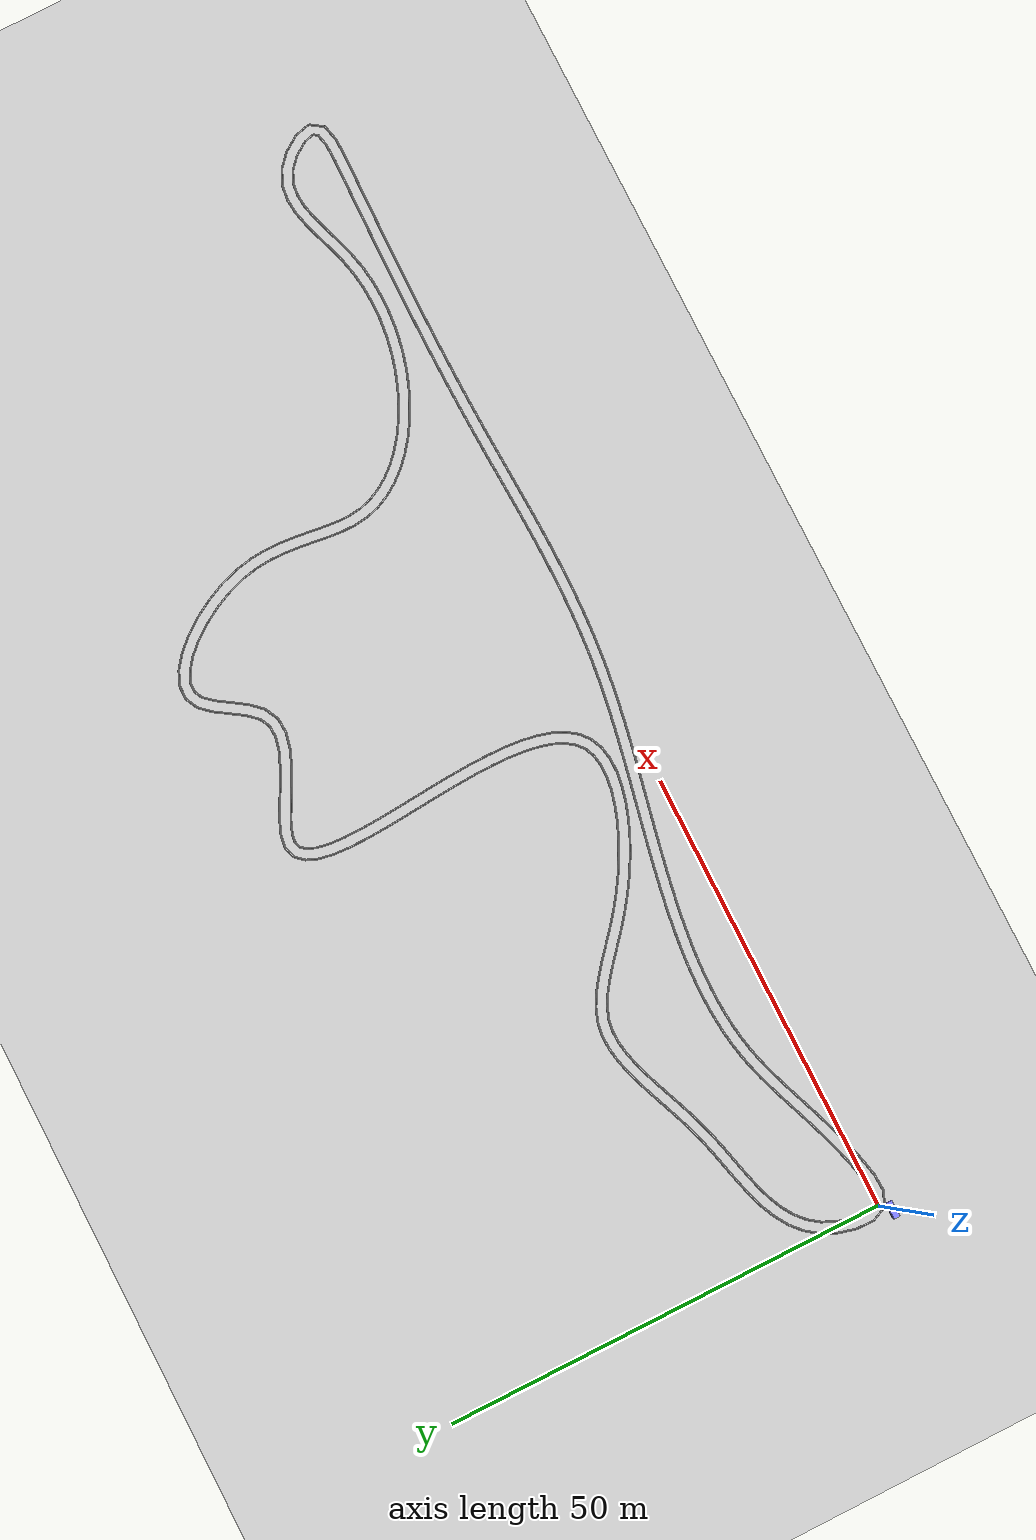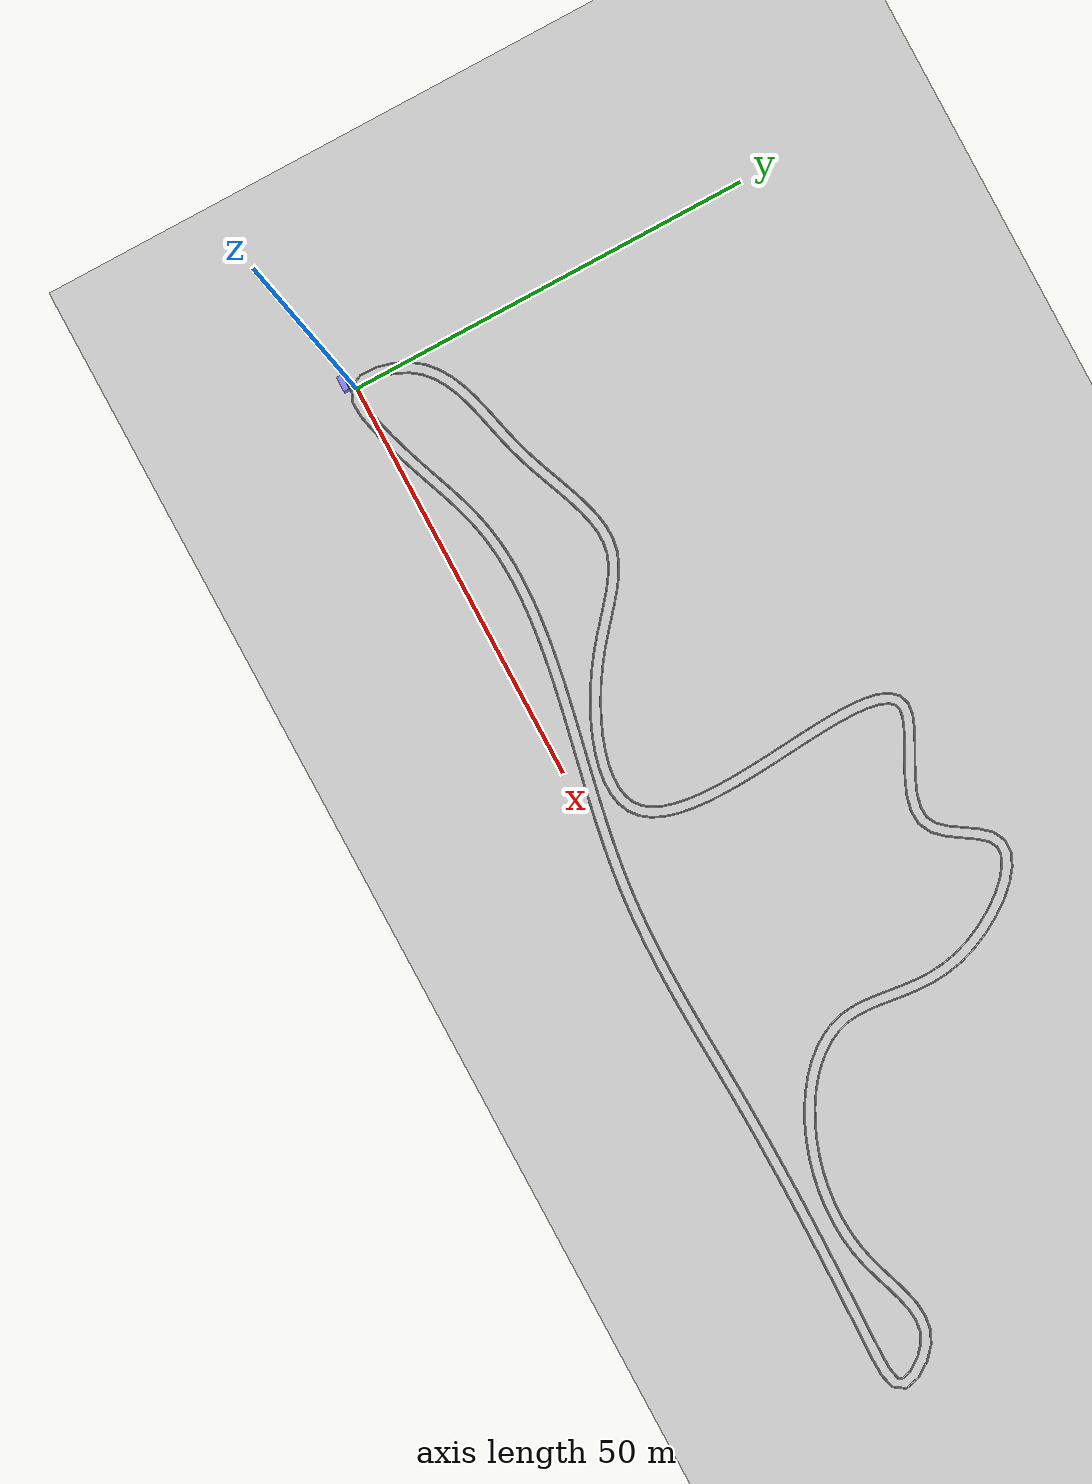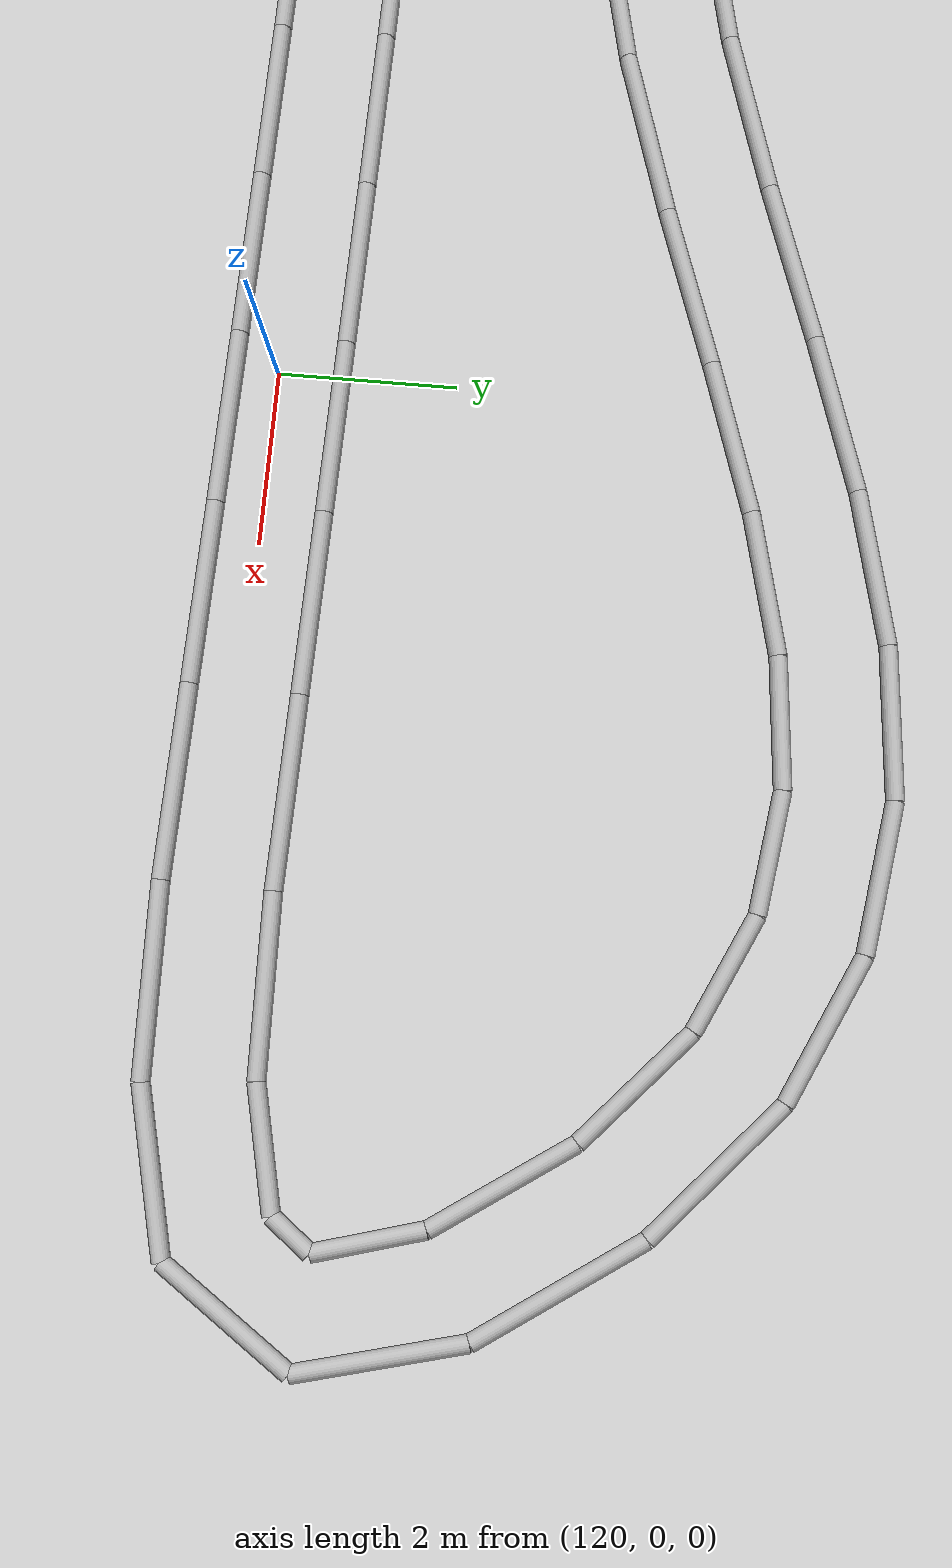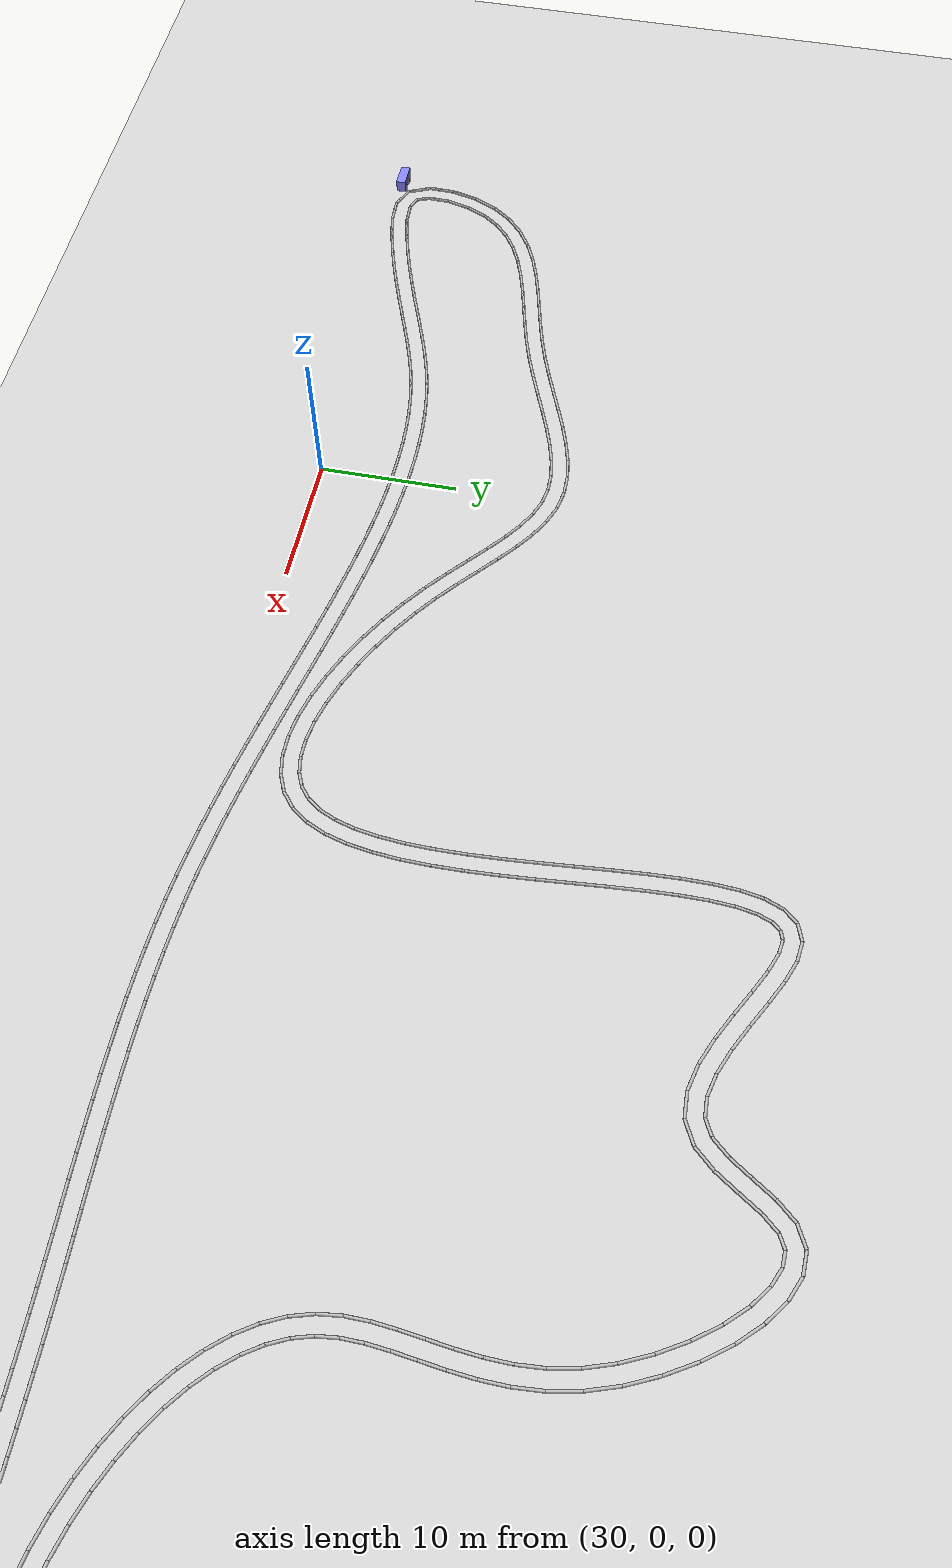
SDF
<?xml version='1.0' encoding='utf-8'?>
<sdf version="1.6">
  <world name="default">

    <include>
      <uri> file:///home/dliujm/um_files/rob_498_av/AutoVehicle25/audi_ws/src/vehicle_desc/models/lucy </uri>
      <pose> -1 -1 0.7205 0 0 0 </pose>
    </include>

    <model name="ground_plane">
      <static>true</static>
      <link name="link">
        <collision name="collision">
          <geometry>
            <plane>
              <normal>0 0 1</normal>
              <size>5000 5000</size>
            </plane>
          </geometry>
          <surface>
            <friction>
              <ode>
                <mu>50</mu>
              </ode>
              <bullet>
                <friction>1</friction>
                <rolling_friction>0.1</rolling_friction>
              </bullet>
            </friction>
            <bounce />
            <contact />
          </surface>
        </collision>
        <visual name="visual">
          <geometry>
            <plane>
              <normal>0 0 1</normal>
              <size>5000 5000</size>
            </plane>
          </geometry>
          <material>
            <ambient>0.8 0.8 0.8 1</ambient>
            <diffuse>0.8 0.8 0.8 1</diffuse>
            <specular>0.8 0.8 0.8 1</specular>
          </material>
        </visual>
        <pose>0 0 0 0 -0 0</pose>
        <inertial>
          <pose>0 0 0 0 -0 0</pose>
          <mass>1</mass>
          <inertia>
            <ixx>1</ixx>
            <ixy>0</ixy>
            <ixz>0</ixz>
            <iyy>1</iyy>
            <iyz>0</iyz>
            <izz>1</izz>
          </inertia>
        </inertial>
        <enable_wind>false</enable_wind>
      </link>
      <pose>0 0 0 0 -0 0</pose>
      <self_collide>false</self_collide>
    </model>
    <light name="sun" type="directional">
      <cast_shadows>true</cast_shadows>
      <pose>0 0 10 0 0 0</pose>
      <direction>-0.5 0.5 -1</direction>
    </light>
    <model name="line_model">
      <static>true</static>
      <link name="cylinder_(-0.42490210521195326, -0.4236250712439601)_(1.1908441192839923, -1.1194447244828043)">
        <pose>0.3829710070360195 -0.7715348978633823 0.05 0 1.5707963267948966 -0.40664573701741885</pose>
        <visual name="visual">
          <geometry>
            <cylinder>
              <radius>0.1</radius>
              <length>1.759204607715182</length>
            </cylinder>
          </geometry>
        </visual>
        <collision name="collision">
          <geometry>
            <cylinder>
              <radius>0.1</radius>
              <length>1.759204607715182</length>
            </cylinder>
          </geometry>
        </collision>
      </link>
      <link name="cylinder_(1.1908441192839923, -1.1194447244828043)_(3.091994487557768, -1.030270376383361)">
        <pose>2.1414193034208804 -1.0748575504330826 0.05 0 1.5707963267948966 0.04687111425009558</pose>
        <visual name="visual">
          <geometry>
            <cylinder>
              <radius>0.1</radius>
              <length>1.9032406014864423</length>
            </cylinder>
          </geometry>
        </visual>
        <collision name="collision">
          <geometry>
            <cylinder>
              <radius>0.1</radius>
              <length>1.9032406014864423</length>
            </cylinder>
          </geometry>
        </collision>
      </link>
      <link name="cylinder_(3.091994487557768, -1.030270376383361)_(5.074517604105659, -0.6003794913893742)">
        <pose>4.083256045831714 -0.8153249338863675 0.05 0 1.5707963267948966 0.21353447312620455</pose>
        <visual name="visual">
          <geometry>
            <cylinder>
              <radius>0.1</radius>
              <length>2.0285965790781755</length>
            </cylinder>
          </geometry>
        </visual>
        <collision name="collision">
          <geometry>
            <cylinder>
              <radius>0.1</radius>
              <length>2.0285965790781755</length>
            </cylinder>
          </geometry>
        </collision>
      </link>
      <link name="cylinder_(5.074517604105659, -0.6003794913893742)_(6.9579002851628955, -0.08009286775584715)">
        <pose>6.016208944634277 -0.34023617957261065 0.05 0 1.5707963267948966 0.26952901872523805</pose>
        <visual name="visual">
          <geometry>
            <cylinder>
              <radius>0.1</radius>
              <length>1.9539264300475387</length>
            </cylinder>
          </geometry>
        </visual>
        <collision name="collision">
          <geometry>
            <cylinder>
              <radius>0.1</radius>
              <length>1.9539264300475387</length>
            </cylinder>
          </geometry>
        </collision>
      </link>
      <link name="cylinder_(6.9579002851628955, -0.08009286775584715)_(8.729994601687931, 0.47400390705059803)">
        <pose>7.843947443425414 0.19695551964737545 0.05 0 1.5707963267948966 0.3030479841500894</pose>
        <visual name="visual">
          <geometry>
            <cylinder>
              <radius>0.1</radius>
              <length>1.8567017807152655</length>
            </cylinder>
          </geometry>
        </visual>
        <collision name="collision">
          <geometry>
            <cylinder>
              <radius>0.1</radius>
              <length>1.8567017807152655</length>
            </cylinder>
          </geometry>
        </collision>
      </link>
      <link name="cylinder_(8.729994601687931, 0.47400390705059803)_(10.405185362650311, 1.0484684190541398)">
        <pose>9.567589982169121 0.761236163052369 0.05 0 1.5707963267948966 0.3303579236713938</pose>
        <visual name="visual">
          <geometry>
            <cylinder>
              <radius>0.1</radius>
              <length>1.770952726970764</length>
            </cylinder>
          </geometry>
        </visual>
        <collision name="collision">
          <geometry>
            <cylinder>
              <radius>0.1</radius>
              <length>1.770952726970764</length>
            </cylinder>
          </geometry>
        </collision>
      </link>
      <link name="cylinder_(10.405185362650311, 1.0484684190541398)_(11.997865557862005, 1.629858035329601)">
        <pose>11.201525460256157 1.3391632271918703 0.05 0 1.5707963267948966 0.35000884361238016</pose>
        <visual name="visual">
          <geometry>
            <cylinder>
              <radius>0.1</radius>
              <length>1.6954775404388247</length>
            </cylinder>
          </geometry>
        </visual>
        <collision name="collision">
          <geometry>
            <cylinder>
              <radius>0.1</radius>
              <length>1.6954775404388247</length>
            </cylinder>
          </geometry>
        </collision>
      </link>
      <link name="cylinder_(11.997865557862005, 1.629858035329601)_(13.522477881215085, 2.2048133128910097)">
        <pose>12.760171719538544 1.9173356741103054 0.05 0 1.5707963267948966 0.3606242586592719</pose>
        <visual name="visual">
          <geometry>
            <cylinder>
              <radius>0.1</radius>
              <length>1.6294220778287605</length>
            </cylinder>
          </geometry>
        </visual>
        <collision name="collision">
          <geometry>
            <cylinder>
              <radius>0.1</radius>
              <length>1.6294220778287605</length>
            </cylinder>
          </geometry>
        </collision>
      </link>
      <link name="cylinder_(13.522477881215085, 2.2048133128910097)_(14.993519838179548, 2.7601410753054667)">
        <pose>14.257998859697317 2.482477194098238 0.05 0 1.5707963267948966 0.36096625466536547</pose>
        <visual name="visual">
          <geometry>
            <cylinder>
              <radius>0.1</radius>
              <length>1.5723718907618782</length>
            </cylinder>
          </geometry>
        </visual>
        <collision name="collision">
          <geometry>
            <cylinder>
              <radius>0.1</radius>
              <length>1.5723718907618782</length>
            </cylinder>
          </geometry>
        </collision>
      </link>
      <link name="cylinder_(14.993519838179548, 2.7601410753054667)_(16.425564987053395, 3.2828989287556483)">
        <pose>15.709542412616472 3.0215200020305577 0.05 0 1.5707963267948966 0.350012674009541</pose>
        <visual name="visual">
          <geometry>
            <cylinder>
              <radius>0.1</radius>
              <length>1.5244766583181784</length>
            </cylinder>
          </geometry>
        </visual>
        <collision name="collision">
          <geometry>
            <cylinder>
              <radius>0.1</radius>
              <length>1.5244766583181784</length>
            </cylinder>
          </geometry>
        </collision>
      </link>
      <link name="cylinder_(16.425564987053395, 3.2828989287556483)_(17.8333194081268, 3.760470914795119)">
        <pose>17.129442197590098 3.5216849217753836 0.05 0 1.5707963267948966 0.32706052616070114</pose>
        <visual name="visual">
          <geometry>
            <cylinder>
              <radius>0.1</radius>
              <length>1.4865555865494586</length>
            </cylinder>
          </geometry>
        </visual>
        <collision name="collision">
          <geometry>
            <cylinder>
              <radius>0.1</radius>
              <length>1.4865555865494586</length>
            </cylinder>
          </geometry>
        </collision>
      </link>
      <link name="cylinder_(17.8333194081268, 3.760470914795119)_(19.231726768766382, 4.1806136170179204)">
        <pose>18.53252308844659 3.97054226590652 0.05 0 1.5707963267948966 0.2918638225384362</pose>
        <visual name="visual">
          <geometry>
            <cylinder>
              <radius>0.1</radius>
              <length>1.4601585655407556</length>
            </cylinder>
          </geometry>
        </visual>
        <collision name="collision">
          <geometry>
            <cylinder>
              <radius>0.1</radius>
              <length>1.4601585655407556</length>
            </cylinder>
          </geometry>
        </collision>
      </link>
      <link name="cylinder_(19.231726768766382, 4.1806136170179204)_(20.636491258416903, 4.531671735044268)">
        <pose>19.934109013591645 4.356142676031094 0.05 0 1.5707963267948966 0.2448895496930728</pose>
        <visual name="visual">
          <geometry>
            <cylinder>
              <radius>0.1</radius>
              <length>1.4479658399338329</length>
            </cylinder>
          </geometry>
        </visual>
        <collision name="collision">
          <geometry>
            <cylinder>
              <radius>0.1</radius>
              <length>1.4479658399338329</length>
            </cylinder>
          </geometry>
        </collision>
      </link>
      <link name="cylinder_(20.636491258416903, 4.531671735044268)_(22.0627879557665, 4.809466026150759)">
        <pose>21.349639607091703 4.670568880597514 0.05 0 1.5707963267948966 0.19235796682162745</pose>
        <visual name="visual">
          <geometry>
            <cylinder>
              <radius>0.1</radius>
              <length>1.4530973597944916</length>
            </cylinder>
          </geometry>
        </visual>
        <collision name="collision">
          <geometry>
            <cylinder>
              <radius>0.1</radius>
              <length>1.4530973597944916</length>
            </cylinder>
          </geometry>
        </collision>
      </link>
      <link name="cylinder_(22.0627879557665, 4.809466026150759)_(23.512406203221687, 5.01764055869068)">
        <pose>22.78759707949409 4.913553292420719 0.05 0 1.5707963267948966 0.1426312999129373</pose>
        <visual name="visual">
          <geometry>
            <cylinder>
              <radius>0.1</radius>
              <length>1.4644895695611029</length>
            </cylinder>
          </geometry>
        </visual>
        <collision name="collision">
          <geometry>
            <cylinder>
              <radius>0.1</radius>
              <length>1.4644895695611029</length>
            </cylinder>
          </geometry>
        </collision>
      </link>
      <link name="cylinder_(23.512406203221687, 5.01764055869068)_(24.984612074882982, 5.160124359403968)">
        <pose>24.248509139052334 5.088882459047324 0.05 0 1.5707963267948966 0.09648202874275892</pose>
        <visual name="visual">
          <geometry>
            <cylinder>
              <radius>0.1</radius>
              <length>1.479084771748968</length>
            </cylinder>
          </geometry>
        </visual>
        <collision name="collision">
          <geometry>
            <cylinder>
              <radius>0.1</radius>
              <length>1.479084771748968</length>
            </cylinder>
          </geometry>
        </collision>
      </link>
      <link name="cylinder_(24.984612074882982, 5.160124359403968)_(26.478593727209763, 5.240849577262615)">
        <pose>25.731602901046372 5.2004869683332915 0.05 0 1.5707963267948966 0.053981113129797524</pose>
        <visual name="visual">
          <geometry>
            <cylinder>
              <radius>0.1</radius>
              <length>1.4961610001224415</length>
            </cylinder>
          </geometry>
        </visual>
        <collision name="collision">
          <geometry>
            <cylinder>
              <radius>0.1</radius>
              <length>1.4961610001224415</length>
            </cylinder>
          </geometry>
        </collision>
      </link>
      <link name="cylinder_(26.478593727209763, 5.240849577262615)_(27.9934754372947, 5.2637653848314105)">
        <pose>27.23603458225223 5.252307481047013 0.05 0 1.5707963267948966 0.015125973014970729</pose>
        <visual name="visual">
          <geometry>
            <cylinder>
              <radius>0.1</radius>
              <length>1.5150550253328718</length>
            </cylinder>
          </geometry>
        </visual>
        <collision name="collision">
          <geometry>
            <cylinder>
              <radius>0.1</radius>
              <length>1.5150550253328718</length>
            </cylinder>
          </geometry>
        </collision>
      </link>
      <link name="cylinder_(27.9934754372947, 5.2637653848314105)_(29.528332499339804, 5.232846513929506)">
        <pose>28.76090396831725 5.248305949380459 0.05 0 1.5707963267948966 -0.020141738535908203</pose>
        <visual name="visual">
          <geometry>
            <cylinder>
              <radius>0.1</radius>
              <length>1.5351684524792653</length>
            </cylinder>
          </geometry>
        </visual>
        <collision name="collision">
          <geometry>
            <cylinder>
              <radius>0.1</radius>
              <length>1.5351684524792653</length>
            </cylinder>
          </geometry>
        </collision>
      </link>
      <link name="cylinder_(29.528332499339804, 5.232846513929506)_(31.082205224692803, 5.152097378915327)">
        <pose>30.305268862016305 5.192471946422417 0.05 0 1.5707963267948966 -0.051919673633760946</pose>
        <visual name="visual">
          <geometry>
            <cylinder>
              <radius>0.1</radius>
              <length>1.555969430741329</length>
            </cylinder>
          </geometry>
        </visual>
        <collision name="collision">
          <geometry>
            <cylinder>
              <radius>0.1</radius>
              <length>1.555969430741329</length>
            </cylinder>
          </geometry>
        </collision>
      </link>
      <link name="cylinder_(31.082205224692803, 5.152097378915327)_(32.654111068658146, 5.025552953069772)">
        <pose>31.868158146675476 5.088825165992549 0.05 0 1.5707963267948966 -0.08033058213804231</pose>
        <visual name="visual">
          <geometry>
            <cylinder>
              <radius>0.1</radius>
              <length>1.5769912726470552</length>
            </cylinder>
          </geometry>
        </visual>
        <collision name="collision">
          <geometry>
            <cylinder>
              <radius>0.1</radius>
              <length>1.5769912726470552</length>
            </cylinder>
          </geometry>
        </collision>
      </link>
      <link name="cylinder_(32.654111068658146, 5.025552953069772)_(34.24305451079734, 4.857277501087925)">
        <pose>33.448582789727745 4.941415227078848 0.05 0 1.5707963267948966 -0.10551070663037972</pose>
        <visual name="visual">
          <geometry>
            <cylinder>
              <radius>0.1</radius>
              <length>1.5978291179149458</length>
            </cylinder>
          </geometry>
        </visual>
        <collision name="collision">
          <geometry>
            <cylinder>
              <radius>0.1</radius>
              <length>1.5978291179149458</length>
            </cylinder>
          </geometry>
        </collision>
      </link>
      <link name="cylinder_(34.24305451079734, 4.857277501087925)_(35.84803471329416, 4.6513620729837895)">
        <pose>35.04554461204575 4.754319787035858 0.05 0 1.5707963267948966 -0.12760072980671502</pose>
        <visual name="visual">
          <geometry>
            <cylinder>
              <radius>0.1</radius>
              <length>1.618135536331255</length>
            </cylinder>
          </geometry>
        </visual>
        <collision name="collision">
          <geometry>
            <cylinder>
              <radius>0.1</radius>
              <length>1.618135536331255</length>
            </cylinder>
          </geometry>
        </collision>
      </link>
      <link name="cylinder_(35.84803471329416, 4.6513620729837895)_(37.468051202185926, 4.411921430507268)">
        <pose>36.658042957740044 4.5316417517455285 0.05 0 1.5707963267948966 -0.14673899931854084</pose>
        <visual name="visual">
          <geometry>
            <cylinder>
              <radius>0.1</radius>
              <length>1.637615719743423</length>
            </cylinder>
          </geometry>
        </visual>
        <collision name="collision">
          <geometry>
            <cylinder>
              <radius>0.1</radius>
              <length>1.637615719743423</length>
            </cylinder>
          </geometry>
        </collision>
      </link>
      <link name="cylinder_(37.468051202185926, 4.411921430507268)_(39.10210790791441, 4.143090862295393)">
        <pose>38.28507955505017 4.277506146401331 0.05 0 1.5707963267948966 -0.16305665831483268</pose>
        <visual name="visual">
          <geometry>
            <cylinder>
              <radius>0.1</radius>
              <length>1.6560227027252197</length>
            </cylinder>
          </geometry>
        </visual>
        <collision name="collision">
          <geometry>
            <cylinder>
              <radius>0.1</radius>
              <length>1.6560227027252197</length>
            </cylinder>
          </geometry>
        </collision>
      </link>
      <link name="cylinder_(39.10210790791441, 4.143090862295393)_(40.749215912476004, 3.849023171927874)">
        <pose>39.9256619101952 3.9960570171116334 0.05 0 1.5707963267948966 -0.17667429598291565</pose>
        <visual name="visual">
          <geometry>
            <cylinder>
              <radius>0.1</radius>
              <length>1.673152887577512</length>
            </cylinder>
          </geometry>
        </visual>
        <collision name="collision">
          <geometry>
            <cylinder>
              <radius>0.1</radius>
              <length>1.673152887577512</length>
            </cylinder>
          </geometry>
        </collision>
      </link>
      <link name="cylinder_(40.749215912476004, 3.849023171927874)_(42.40839521754821, 3.5338859976778467)">
        <pose>41.578805565012104 3.6914545848028606 0.05 0 1.5707963267948966 -0.18769976485526352</pose>
        <visual name="visual">
          <geometry>
            <cylinder>
              <radius>0.1</radius>
              <length>1.6888420307933438</length>
            </cylinder>
          </geometry>
        </visual>
        <collision name="collision">
          <geometry>
            <cylinder>
              <radius>0.1</radius>
              <length>1.6888420307933438</length>
            </cylinder>
          </geometry>
        </collision>
      </link>
      <link name="cylinder_(42.40839521754821, 3.5338859976778467)_(44.0786757963008, 3.2018595382521617)">
        <pose>43.2435355069245 3.3678727679650042 0.05 0 1.5707963267948966 -0.19622686524881242</pose>
        <visual name="visual">
          <geometry>
            <cylinder>
              <radius>0.1</radius>
              <length>1.7029617674853537</length>
            </cylinder>
          </geometry>
        </visual>
        <collision name="collision">
          <geometry>
            <cylinder>
              <radius>0.1</radius>
              <length>1.7029617674853537</length>
            </cylinder>
          </geometry>
        </collision>
      </link>
      <link name="cylinder_(44.0786757963008, 3.2018595382521617)_(45.759098135993014, 2.857134706126849)">
        <pose>44.91888696614691 3.0294971221895053 0.05 0 1.5707963267948966 -0.20233465634317807</pose>
        <visual name="visual">
          <geometry>
            <cylinder>
              <radius>0.1</radius>
              <length>1.715416698537262</length>
            </cylinder>
          </geometry>
        </visual>
        <collision name="collision">
          <geometry>
            <cylinder>
              <radius>0.1</radius>
              <length>1.715416698537262</length>
            </cylinder>
          </geometry>
        </collision>
      </link>
      <link name="cylinder_(45.759098135993014, 2.857134706126849)_(47.44871342654577, 2.503911700198528)">
        <pose>46.60390578126939 2.6805232031626884 0.05 0 1.5707963267948966 -0.20608720965147564</pose>
        <visual name="visual">
          <geometry>
            <cylinder>
              <radius>0.1</radius>
              <length>1.7261420341289189</length>
            </cylinder>
          </geometry>
        </visual>
        <collision name="collision">
          <geometry>
            <cylinder>
              <radius>0.1</radius>
              <length>1.7261420341289189</length>
            </cylinder>
          </geometry>
        </collision>
      </link>
      <link name="cylinder_(47.44871342654577, 2.503911700198528)_(49.146583505119345, 2.14639897485304)">
        <pose>48.29764846583256 2.325155337525784 0.05 0 1.5707963267948966 -0.2075336702733194</pose>
        <visual name="visual">
          <geometry>
            <cylinder>
              <radius>0.1</radius>
              <length>1.73510177006981</length>
            </cylinder>
          </geometry>
        </visual>
        <collision name="collision">
          <geometry>
            <cylinder>
              <radius>0.1</radius>
              <length>1.73510177006981</length>
            </cylinder>
          </geometry>
        </collision>
      </link>
      <link name="cylinder_(49.146583505119345, 2.14639897485304)_(50.851780628765574, 1.7888125774310855)">
        <pose>49.99918206694246 1.967605776142063 0.05 0 1.5707963267948966 -0.2067085334373408</pose>
        <visual name="visual">
          <geometry>
            <cylinder>
              <radius>0.1</radius>
              <length>1.7422873649638242</length>
            </cylinder>
          </geometry>
        </visual>
        <collision name="collision">
          <geometry>
            <cylinder>
              <radius>0.1</radius>
              <length>1.7422873649638242</length>
            </cylinder>
          </geometry>
        </collision>
      </link>
      <link name="cylinder_(50.851780628765574, 1.7888125774310855)_(52.56338711558502, 1.4353758262490761)">
        <pose>51.7075838721753 1.6120942018400808 0.05 0 1.5707963267948966 -0.20363207903535804</pose>
        <visual name="visual">
          <geometry>
            <cylinder>
              <radius>0.1</radius>
              <length>1.7477168829099605</length>
            </cylinder>
          </geometry>
        </visual>
        <collision name="collision">
          <geometry>
            <cylinder>
              <radius>0.1</radius>
              <length>1.7477168829099605</length>
            </cylinder>
          </geometry>
        </collision>
      </link>
      <link name="cylinder_(52.56338711558502, 1.4353758262490761)_(54.280494868097854, 1.090319303800935)">
        <pose>53.42194099184144 1.2628475650250055 0.05 0 1.5707963267948966 -0.1983109363935158</pose>
        <visual name="visual">
          <geometry>
            <cylinder>
              <radius>0.1</radius>
              <length>1.7514345655558103</length>
            </cylinder>
          </geometry>
        </visual>
        <collision name="collision">
          <geometry>
            <cylinder>
              <radius>0.1</radius>
              <length>1.7514345655558103</length>
            </cylinder>
          </geometry>
        </collision>
      </link>
      <link name="cylinder_(54.280494868097854, 1.090319303800935)_(56.0022047692579, 0.7578811423034493)">
        <pose>55.14134981867788 0.9241002230521921 0.05 0 1.5707963267948966 -0.1907387768709768</pose>
        <visual name="visual">
          <geometry>
            <cylinder>
              <radius>0.1</radius>
              <length>1.7535107969363537</length>
            </cylinder>
          </geometry>
        </visual>
        <collision name="collision">
          <geometry>
            <cylinder>
              <radius>0.1</radius>
              <length>1.7535107969363537</length>
            </cylinder>
          </geometry>
        </collision>
      </link>
      <link name="cylinder_(56.0022047692579, 0.7578811423034493)_(57.727625920437426, 0.442307579578182)">
        <pose>56.86491534484766 0.6000943609408156 0.05 0 1.5707963267948966 -0.1808971543747414</pose>
        <visual name="visual">
          <geometry>
            <cylinder>
              <radius>0.1</radius>
              <length>1.7540424232123906</length>
            </cylinder>
          </geometry>
        </visual>
        <collision name="collision">
          <geometry>
            <cylinder>
              <radius>0.1</radius>
              <length>1.7540424232123906</length>
            </cylinder>
          </geometry>
        </collision>
      </link>
      <link name="cylinder_(57.727625920437426, 0.442307579578182)_(59.4558746709025, 0.14785376078527576)">
        <pose>58.59175029566997 0.2950806701817289 0.05 0 1.5707963267948966 -0.16875653459969686</pose>
        <visual name="visual">
          <geometry>
            <cylinder>
              <radius>0.1</radius>
              <length>1.7531533860121387</length>
            </cylinder>
          </geometry>
        </visual>
        <collision name="collision">
          <geometry>
            <cylinder>
              <radius>0.1</radius>
              <length>1.7531533860121387</length>
            </cylinder>
          </geometry>
        </collision>
      </link>
      <link name="cylinder_(59.4558746709025, 0.14785376078527576)_(61.18607336949037, -0.12121524587791974)">
        <pose>60.32097402019644 0.013319257453678013 0.05 0 1.5707963267948966 -0.15427757338818857</pose>
        <visual name="visual">
          <geometry>
            <cylinder>
              <radius>0.1</radius>
              <length>1.7509956216227034</length>
            </cylinder>
          </geometry>
        </visual>
        <collision name="collision">
          <geometry>
            <cylinder>
              <radius>0.1</radius>
              <length>1.7509956216227034</length>
            </cylinder>
          </geometry>
        </collision>
      </link>
      <link name="cylinder_(61.18607336949037, -0.12121524587791974)_(62.917348751878514, -0.36062326544347895)">
        <pose>62.05171106068444 -0.24091925566069933 0.05 0 1.5707963267948966 -0.137412723112346</pose>
        <visual name="visual">
          <geometry>
            <cylinder>
              <radius>0.1</radius>
              <length>1.7477501679289025</length>
            </cylinder>
          </geometry>
        </visual>
        <collision name="collision">
          <geometry>
            <cylinder>
              <radius>0.1</radius>
              <length>1.7477501679289025</length>
            </cylinder>
          </geometry>
        </collision>
      </link>
      <link name="cylinder_(62.917348751878514, -0.36062326544347895)_(64.6488298625912, -0.5660817327848389)">
        <pose>63.78308930723486 -0.4633524991141589 0.05 0 1.5707963267948966 -0.11810826268228325</pose>
        <visual name="visual">
          <geometry>
            <cylinder>
              <radius>0.1</radius>
              <length>1.743628406099504</length>
            </cylinder>
          </geometry>
        </visual>
        <collision name="collision">
          <geometry>
            <cylinder>
              <radius>0.1</radius>
              <length>1.743628406099504</length>
            </cylinder>
          </geometry>
        </collision>
      </link>
      <link name="cylinder_(64.6488298625912, -0.5660817327848389)_(66.37872384263247, -0.7339099857343313)">
        <pose>65.51377685261184 -0.6499958592595851 0.05 0 1.5707963267948966 -0.096713824203417</pose>
        <visual name="visual">
          <geometry>
            <cylinder>
              <radius>0.1</radius>
              <length>1.7380159678987699</length>
            </cylinder>
          </geometry>
        </visual>
        <collision name="collision">
          <geometry>
            <cylinder>
              <radius>0.1</radius>
              <length>1.7380159678987699</length>
            </cylinder>
          </geometry>
        </collision>
      </link>
      <link name="cylinder_(66.37872384263247, -0.7339099857343313)_(68.10414912517712, -0.8650764845923788)">
        <pose>67.24143648390479 -0.799493235163355 0.05 0 1.5707963267948966 -0.07587387399805764</pose>
        <visual name="visual">
          <geometry>
            <cylinder>
              <radius>0.1</radius>
              <length>1.7304037263213918</length>
            </cylinder>
          </geometry>
        </visual>
        <collision name="collision">
          <geometry>
            <cylinder>
              <radius>0.1</radius>
              <length>1.7304037263213918</length>
            </cylinder>
          </geometry>
        </collision>
      </link>
      <link name="cylinder_(68.10414912517712, -0.8650764845923788)_(69.82364428107424, -0.9626404442867024)">
        <pose>68.96389670312567 -0.9138584644395407 0.05 0 1.5707963267948966 -0.05667911393857689</pose>
        <visual name="visual">
          <geometry>
            <cylinder>
              <radius>0.1</radius>
              <length>1.722260815725917</length>
            </cylinder>
          </geometry>
        </visual>
        <collision name="collision">
          <geometry>
            <cylinder>
              <radius>0.1</radius>
              <length>1.722260815725917</length>
            </cylinder>
          </geometry>
        </collision>
      </link>
      <link name="cylinder_(69.82364428107424, -0.9626404442867024)_(71.53578515310383, -1.0296655577872333)">
        <pose>70.67971471708904 -0.9961530010369679 0.05 0 1.5707963267948966 -0.03912698290406215</pose>
        <visual name="visual">
          <geometry>
            <cylinder>
              <radius>0.1</radius>
              <length>1.7134522845746287</length>
            </cylinder>
          </geometry>
        </visual>
        <collision name="collision">
          <geometry>
            <cylinder>
              <radius>0.1</radius>
              <length>1.7134522845746287</length>
            </cylinder>
          </geometry>
        </collision>
      </link>
      <link name="cylinder_(71.53578515310383, -1.0296655577872333)_(73.23914906971584, -1.0692105656309485)">
        <pose>72.38746711140983 -1.049438061709091 0.05 0 1.5707963267948966 -0.02321166085968011</pose>
        <visual name="visual">
          <geometry>
            <cylinder>
              <radius>0.1</radius>
              <length>1.7038228898747516</length>
            </cylinder>
          </geometry>
        </visual>
        <collision name="collision">
          <geometry>
            <cylinder>
              <radius>0.1</radius>
              <length>1.7038228898747516</length>
            </cylinder>
          </geometry>
        </collision>
      </link>
      <link name="cylinder_(73.23914906971584, -1.0692105656309485)_(74.93231355480104, -1.0843292897933388)">
        <pose>74.08573131225845 -1.0767699277121436 0.05 0 1.5707963267948966 -0.00892903347550474</pose>
        <visual name="visual">
          <geometry>
            <cylinder>
              <radius>0.1</radius>
              <length>1.6932319833307385</length>
            </cylinder>
          </geometry>
        </visual>
        <collision name="collision">
          <geometry>
            <cylinder>
              <radius>0.1</radius>
              <length>1.6932319833307385</length>
            </cylinder>
          </geometry>
        </collision>
      </link>
      <link name="cylinder_(74.93231355480104, -1.0843292897933388)_(76.61385514079241, -1.078070735007637)">
        <pose>75.77308434779673 -1.081200012400488 0.05 0 1.5707963267948966 0.0037218977745712067</pose>
        <visual name="visual">
          <geometry>
            <cylinder>
              <radius>0.1</radius>
              <length>1.6815532328553777</length>
            </cylinder>
          </geometry>
        </visual>
        <collision name="collision">
          <geometry>
            <cylinder>
              <radius>0.1</radius>
              <length>1.6815532328553777</length>
            </cylinder>
          </geometry>
        </collision>
      </link>
      <link name="cylinder_(76.61385514079241, -1.078070735007637)_(78.28234827015892, -1.0534792192528566)">
        <pose>77.44810170547566 -1.0657749771302467 0.05 0 1.5707963267948966 0.014737690479147645</pose>
        <visual name="visual">
          <geometry>
            <cylinder>
              <radius>0.1</radius>
              <length>1.6686743437202982</length>
            </cylinder>
          </geometry>
        </visual>
        <collision name="collision">
          <geometry>
            <cylinder>
              <radius>0.1</radius>
              <length>1.6686743437202982</length>
            </cylinder>
          </geometry>
        </collision>
      </link>
      <link name="cylinder_(78.28234827015892, -1.0534792192528566)_(79.93636426591131, -1.0135944991903156)">
        <pose>79.10935626803511 -1.0335368592215861 0.05 0 1.5707963267948966 0.02410919371888497</pose>
        <visual name="visual">
          <geometry>
            <cylinder>
              <radius>0.1</radius>
              <length>1.654496813263547</length>
            </cylinder>
          </geometry>
        </visual>
        <collision name="collision">
          <geometry>
            <cylinder>
              <radius>0.1</radius>
              <length>1.654496813263547</length>
            </cylinder>
          </geometry>
        </collision>
      </link>
      <link name="cylinder_(79.93636426591131, -1.0135944991903156)_(81.57447034919313, -0.9614518591887812)">
        <pose>80.75541730755222 -0.9875231791895485 0.05 0 1.5707963267948966 0.031820308005831535</pose>
        <visual name="visual">
          <geometry>
            <cylinder>
              <radius>0.1</radius>
              <length>1.6389357507209534</length>
            </cylinder>
          </geometry>
        </visual>
        <collision name="collision">
          <geometry>
            <cylinder>
              <radius>0.1</radius>
              <length>1.6389357507209534</length>
            </cylinder>
          </geometry>
        </collision>
      </link>
      <link name="cylinder_(81.57447034919313, -0.9614518591887812)_(83.19522868099027, -0.9000821338789796)">
        <pose>82.3848495150917 -0.9307669965338804 0.05 0 1.5707963267948966 0.037846741123918254</pose>
        <visual name="visual">
          <geometry>
            <cylinder>
              <radius>0.1</radius>
              <length>1.6219197924911175</length>
            </cylinder>
          </geometry>
        </visual>
        <collision name="collision">
          <geometry>
            <cylinder>
              <radius>0.1</radius>
              <length>1.6219197924911175</length>
            </cylinder>
          </geometry>
        </collision>
      </link>
      <link name="cylinder_(83.19522868099027, -0.9000821338789796)_(84.79719540522802, -0.832511633638654)">
        <pose>83.99621204310915 -0.8662968837588167 0.05 0 1.5707963267948966 0.04215472752480525</pose>
        <visual name="visual">
          <geometry>
            <cylinder>
              <radius>0.1</radius>
              <length>1.6033911431923813</length>
            </cylinder>
          </geometry>
        </visual>
        <collision name="collision">
          <geometry>
            <cylinder>
              <radius>0.1</radius>
              <length>1.6033911431923813</length>
            </cylinder>
          </geometry>
        </collision>
      </link>
      <link name="cylinder_(84.79719540522802, -0.832511633638654)_(86.37891967201405, -0.7617619397766893)">
        <pose>85.58805753862103 -0.7971367867076716 0.05 0 1.5707963267948966 0.044699678905558926</pose>
        <visual name="visual">
          <geometry>
            <cylinder>
              <radius>0.1</radius>
              <length>1.583305774423043</length>
            </cylinder>
          </geometry>
        </visual>
        <collision name="collision">
          <geometry>
            <cylinder>
              <radius>0.1</radius>
              <length>1.583305774423043</length>
            </cylinder>
          </geometry>
        </collision>
      </link>
      <link name="cylinder_(86.37891967201405, -0.7617619397766893)_(87.93894262275901, -0.6908495311971052)">
        <pose>87.15893114738654 -0.7263057354868973 0.05 0 1.5707963267948966 0.04542473437777758</pose>
        <visual name="visual">
          <geometry>
            <cylinder>
              <radius>0.1</radius>
              <length>1.5616338164056216</length>
            </cylinder>
          </geometry>
        </visual>
        <collision name="collision">
          <geometry>
            <cylinder>
              <radius>0.1</radius>
              <length>1.5616338164056216</length>
            </cylinder>
          </geometry>
        </collision>
      </link>
      <link name="cylinder_(87.93894262275901, -0.6908495311971052)_(89.47579632394103, -0.6227851966942298)">
        <pose>88.70736947335001 -0.6568173639456676 0.05 0 1.5707963267948966 0.04425918060360364</pose>
        <visual name="visual">
          <geometry>
            <cylinder>
              <radius>0.1</radius>
              <length>1.538360182944217</length>
            </cylinder>
          </geometry>
        </visual>
        <collision name="collision">
          <geometry>
            <cylinder>
              <radius>0.1</radius>
              <length>1.538360182944217</length>
            </cylinder>
          </geometry>
        </collision>
      </link>
      <link name="cylinder_(89.47579632394103, -0.6227851966942298)_(90.98851884593037, -0.5604276135097989)">
        <pose>90.23215758493569 -0.5916064051020143 0.05 0 1.5707963267948966 0.041198764248002354</pose>
        <visual name="visual">
          <geometry>
            <cylinder>
              <radius>0.1</radius>
              <length>1.5140072313943584</length>
            </cylinder>
          </geometry>
        </visual>
        <collision name="collision">
          <geometry>
            <cylinder>
              <radius>0.1</radius>
              <length>1.5140072313943584</length>
            </cylinder>
          </geometry>
        </collision>
      </link>
      <link name="cylinder_(90.98851884593037, -0.5604276135097989)_(92.48041448687374, -0.5048527057496504)">
        <pose>91.73446666640206 -0.5326401596297246 0.05 0 1.5707963267948966 0.03723398701888854</pose>
        <visual name="visual">
          <geometry>
            <cylinder>
              <radius>0.1</radius>
              <length>1.4929303981895388</length>
            </cylinder>
          </geometry>
        </visual>
        <collision name="collision">
          <geometry>
            <cylinder>
              <radius>0.1</radius>
              <length>1.4929303981895388</length>
            </cylinder>
          </geometry>
        </collision>
      </link>
      <link name="cylinder_(92.48041448687374, -0.5048527057496504)_(93.95659136947582, -0.4559489454234866)">
        <pose>93.21850292817479 -0.4804008255865685 0.05 0 1.5707963267948966 0.0331165471547415</pose>
        <visual name="visual">
          <geometry>
            <cylinder>
              <radius>0.1</radius>
              <length>1.4769867184585044</length>
            </cylinder>
          </geometry>
        </visual>
        <collision name="collision">
          <geometry>
            <cylinder>
              <radius>0.1</radius>
              <length>1.4769867184585044</length>
            </cylinder>
          </geometry>
        </collision>
      </link>
      <link name="cylinder_(93.95659136947582, -0.4559489454234866)_(95.42213786742384, -0.4135835402188134)">
        <pose>94.68936461844983 -0.43476624282114995 0.05 0 1.5707963267948966 0.028899533599168886</pose>
        <visual name="visual">
          <geometry>
            <cylinder>
              <radius>0.1</radius>
              <length>1.4661587107833445</length>
            </cylinder>
          </geometry>
        </visual>
        <collision name="collision">
          <geometry>
            <cylinder>
              <radius>0.1</radius>
              <length>1.4661587107833445</length>
            </cylinder>
          </geometry>
        </collision>
      </link>
      <link name="cylinder_(95.42213786742384, -0.4135835402188134)_(96.88214407625512, -0.37762405332056653)">
        <pose>96.15214097183949 -0.39560379676968993 0.05 0 1.5707963267948966 0.024624702322558624</pose>
        <visual name="visual">
          <geometry>
            <cylinder>
              <radius>0.1</radius>
              <length>1.4604489770354372</length>
            </cylinder>
          </geometry>
        </visual>
        <collision name="collision">
          <geometry>
            <cylinder>
              <radius>0.1</radius>
              <length>1.4604489770354372</length>
            </cylinder>
          </geometry>
        </collision>
      </link>
      <link name="cylinder_(96.88214407625512, -0.37762405332056653)_(98.34170095905127, -0.3479384697803022)">
        <pose>97.6119225176532 -0.36278126155043433 0.05 0 1.5707963267948966 0.02033596059653852</pose>
        <visual name="visual">
          <geometry>
            <cylinder>
              <radius>0.1</radius>
              <length>1.4598587356274375</length>
            </cylinder>
          </geometry>
        </visual>
        <collision name="collision">
          <geometry>
            <cylinder>
              <radius>0.1</radius>
              <length>1.4598587356274375</length>
            </cylinder>
          </geometry>
        </collision>
      </link>
      <link name="cylinder_(98.34170095905127, -0.3479384697803022)_(99.8058994264758, -0.3243952312302968)">
        <pose>99.07380019276354 -0.3361668505052995 0.05 0 1.5707963267948966 0.01607788179667908</pose>
        <visual name="visual">
          <geometry>
            <cylinder>
              <radius>0.1</radius>
              <length>1.4643877342049092</length>
            </cylinder>
          </geometry>
        </visual>
        <collision name="collision">
          <geometry>
            <cylinder>
              <radius>0.1</radius>
              <length>1.4643877342049092</length>
            </cylinder>
          </geometry>
        </collision>
      </link>
      <link name="cylinder_(99.8058994264758, -0.3243952312302968)_(101.27982941718481, -0.30686323552430333)">
        <pose>100.5428644218303 -0.3156292333773001 0.05 0 1.5707963267948966 0.011894166650527716</pose>
        <visual name="visual">
          <geometry>
            <cylinder>
              <radius>0.1</radius>
              <length>1.4740342561775481</length>
            </cylinder>
          </geometry>
        </visual>
        <collision name="collision">
          <geometry>
            <cylinder>
              <radius>0.1</radius>
              <length>1.4740342561775481</length>
            </cylinder>
          </geometry>
        </collision>
      </link>
      <link name="cylinder_(101.27982941718481, -0.30686323552430333)_(102.76857904481969, -0.29521180231533845)">
        <pose>102.02420423100224 -0.3010375189198209 0.05 0 1.5707963267948966 0.007826161708405232</pose>
        <visual name="visual">
          <geometry>
            <cylinder>
              <radius>0.1</radius>
              <length>1.4887952208677993</length>
            </cylinder>
          </geometry>
        </visual>
        <collision name="collision">
          <geometry>
            <cylinder>
              <radius>0.1</radius>
              <length>1.4887952208677993</length>
            </cylinder>
          </geometry>
        </collision>
      </link>
      <link name="cylinder_(102.76857904481969, -0.29521180231533845)_(104.27723386987995, -0.2893106097438739)">
        <pose>103.52290645734982 -0.29226120602960615 0.05 0 1.5707963267948966 0.003911539191771642</pose>
        <visual name="visual">
          <geometry>
            <cylinder>
              <radius>0.1</radius>
              <length>1.508666366447988</length>
            </cylinder>
          </geometry>
        </visual>
        <collision name="collision">
          <geometry>
            <cylinder>
              <radius>0.1</radius>
              <length>1.508666366447988</length>
            </cylinder>
          </geometry>
        </collision>
      </link>
      <link name="cylinder_(104.27723386987995, -0.2893106097438739)_(105.81087634020355, -0.2890296105546082)">
        <pose>105.04405510504175 -0.28917011014924104 0.05 0 1.5707963267948966 0.00018322339890728905</pose>
        <visual name="visual">
          <geometry>
            <cylinder>
              <radius>0.1</radius>
              <length>1.5336424960664123</length>
            </cylinder>
          </geometry>
        </visual>
        <collision name="collision">
          <geometry>
            <cylinder>
              <radius>0.1</radius>
              <length>1.5336424960664123</length>
            </cylinder>
          </geometry>
        </collision>
      </link>
      <link name="cylinder_(105.81087634020355, -0.2890296105546082)_(107.37458542511108, -0.29423893760013436)">
        <pose>106.59273088265732 -0.2916342740773713 0.05 0 1.5707963267948966 -0.0033313791066400004</pose>
        <visual name="visual">
          <geometry>
            <cylinder>
              <radius>0.1</radius>
              <length>1.5637177620371938</length>
            </cylinder>
          </geometry>
        </visual>
        <collision name="collision">
          <geometry>
            <cylinder>
              <radius>0.1</radius>
              <length>1.5637177620371938</length>
            </cylinder>
          </geometry>
        </collision>
      </link>
      <link name="cylinder_(107.37458542511108, -0.29423893760013436)_(108.97343644856046, -0.3048088087025771)">
        <pose>108.17401093683577 -0.29952387315135576 0.05 0 1.5707963267948966 -0.006610820500972128</pose>
        <visual name="visual">
          <geometry>
            <cylinder>
              <radius>0.1</radius>
              <length>1.5988859613369137</length>
            </cylinder>
          </geometry>
        </visual>
        <collision name="collision">
          <geometry>
            <cylinder>
              <radius>0.1</radius>
              <length>1.5988859613369137</length>
            </cylinder>
          </geometry>
        </collision>
      </link>
      <link name="cylinder_(108.97343644856046, -0.3048088087025771)_(110.61250110878882, -0.3206094394555555)">
        <pose>109.79296877867463 -0.31270912407906626 0.05 0 1.5707963267948966 -0.009639730336424077</pose>
        <visual name="visual">
          <geometry>
            <cylinder>
              <radius>0.1</radius>
              <length>1.6391408177279005</length>
            </cylinder>
          </geometry>
        </visual>
        <collision name="collision">
          <geometry>
            <cylinder>
              <radius>0.1</radius>
              <length>1.6391408177279005</length>
            </cylinder>
          </geometry>
        </collision>
      </link>
      <link name="cylinder_(110.61250110878882, -0.3206094394555555)_(112.2968476580367, -0.3415109702252698)">
        <pose>111.45467438341277 -0.33106020484041265 0.05 0 1.5707963267948966 -0.012408644765352111</pose>
        <visual name="visual">
          <geometry>
            <cylinder>
              <radius>0.1</radius>
              <length>1.684476230747038</length>
            </cylinder>
          </geometry>
        </visual>
        <collision name="collision">
          <geometry>
            <cylinder>
              <radius>0.1</radius>
              <length>1.684476230747038</length>
            </cylinder>
          </geometry>
        </collision>
      </link>
      <link name="cylinder_(112.2968476580367, -0.3415109702252698)_(114.03154120718891, -0.36738341090692617)">
        <pose>113.1641944326128 -0.35444719056609797 0.05 0 1.5707963267948966 -0.014913598152648682</pose>
        <visual name="visual">
          <geometry>
            <cylinder>
              <radius>0.1</radius>
              <length>1.7348864783198705</length>
            </cylinder>
          </geometry>
        </visual>
        <collision name="collision">
          <geometry>
            <cylinder>
              <radius>0.1</radius>
              <length>1.7348864783198705</length>
            </cylinder>
          </geometry>
        </collision>
      </link>
      <link name="cylinder_(114.03154120718891, -0.36738341090692617)_(115.82164411662662, -0.39809660441460293)">
        <pose>114.92659266190776 -0.38274000766076455 0.05 0 1.5707963267948966 -0.01715553904425735</pose>
        <visual name="visual">
          <geometry>
            <cylinder>
              <radius>0.1</radius>
              <length>1.7903663665944973</length>
            </cylinder>
          </geometry>
        </visual>
        <collision name="collision">
          <geometry>
            <cylinder>
              <radius>0.1</radius>
              <length>1.7903663665944973</length>
            </cylinder>
          </geometry>
        </collision>
      </link>
      <link name="cylinder_(115.82164411662662, -0.39809660441460293)_(117.67221643557166, -0.4335202077866283)">
        <pose>116.74693027609914 -0.41580840610061565 0.05 0 1.5707963267948966 -0.019139634468451266</pose>
        <visual name="visual">
          <geometry>
            <cylinder>
              <radius>0.1</radius>
              <length>1.850911326704087</length>
            </cylinder>
          </geometry>
        </visual>
        <collision name="collision">
          <geometry>
            <cylinder>
              <radius>0.1</radius>
              <length>1.850911326704087</length>
            </cylinder>
          </geometry>
        </collision>
      </link>
      <link name="cylinder_(117.67221643557166, -0.4335202077866283)_(119.58831635652821, -0.4735236883529746)">
        <pose>118.63026639604993 -0.45352194806980145 0.05 0 1.5707963267948966 -0.020874521997675453</pose>
        <visual name="visual">
          <geometry>
            <cylinder>
              <radius>0.1</radius>
              <length>1.9165174628860382</length>
            </cylinder>
          </geometry>
        </visual>
        <collision name="collision">
          <geometry>
            <cylinder>
              <radius>0.1</radius>
              <length>1.9165174628860382</length>
            </cylinder>
          </geometry>
        </collision>
      </link>
      <link name="cylinder_(119.58831635652821, -0.4735236883529746)_(121.57500065775352, -0.5179763316530697)">
        <pose>120.58165850714087 -0.4957500100030221 0.05 0 1.5707963267948966 -0.0223715600106605</pose>
        <visual name="visual">
          <geometry>
            <cylinder>
              <radius>0.1</radius>
              <length>1.987181559453354</length>
            </cylinder>
          </geometry>
        </visual>
        <collision name="collision">
          <geometry>
            <cylinder>
              <radius>0.1</radius>
              <length>1.987181559453354</length>
            </cylinder>
          </geometry>
        </collision>
      </link>
      <link name="cylinder_(121.57500065775352, -0.5179763316530697)_(123.63732511379524, -0.5667472576146395)">
        <pose>122.60616288577438 -0.5423617946338546 0.05 0 1.5707963267948966 -0.023644115314831623</pose>
        <visual name="visual">
          <geometry>
            <cylinder>
              <radius>0.1</radius>
              <length>2.0629010556027483</length>
            </cylinder>
          </geometry>
        </visual>
        <collision name="collision">
          <geometry>
            <cylinder>
              <radius>0.1</radius>
              <length>2.0629010556027483</length>
            </cylinder>
          </geometry>
        </collision>
      </link>
      <link name="cylinder_(123.63732511379524, -0.5667472576146395)_(125.78112356087561, -0.6178366603438624)">
        <pose>124.70922433733543 -0.592291958979251 0.05 0 1.5707963267948966 -0.023826742846093093</pose>
        <visual name="visual">
          <geometry>
            <cylinder>
              <radius>0.1</radius>
              <length>2.144407122907271</length>
            </cylinder>
          </geometry>
        </visual>
        <collision name="collision">
          <geometry>
            <cylinder>
              <radius>0.1</radius>
              <length>2.144407122907271</length>
            </cylinder>
          </geometry>
        </collision>
      </link>
      <link name="cylinder_(125.78112356087561, -0.6178366603438624)_(127.89645645212491, -0.5730451484775761)">
        <pose>126.83879000650026 -0.5954409044107193 0.05 0 1.5707963267948966 0.021171523168343864</pose>
        <visual name="visual">
          <geometry>
            <cylinder>
              <radius>0.1</radius>
              <length>2.1158070612266067</length>
            </cylinder>
          </geometry>
        </visual>
        <collision name="collision">
          <geometry>
            <cylinder>
              <radius>0.1</radius>
              <length>2.1158070612266067</length>
            </cylinder>
          </geometry>
        </collision>
      </link>
      <link name="cylinder_(127.89645645212491, -0.5730451484775761)_(129.6817796624254, -0.14383697907897117)">
        <pose>128.78911805727518 -0.35844106377827367 0.05 0 1.5707963267948966 0.23593188219633704</pose>
        <visual name="visual">
          <geometry>
            <cylinder>
              <radius>0.1</radius>
              <length>1.8361913347786498</length>
            </cylinder>
          </geometry>
        </visual>
        <collision name="collision">
          <geometry>
            <cylinder>
              <radius>0.1</radius>
              <length>1.8361913347786498</length>
            </cylinder>
          </geometry>
        </collision>
      </link>
      <link name="cylinder_(129.6817796624254, -0.14383697907897117)_(130.66364236745954, 1.270782619576106)">
        <pose>130.17271101494248 0.5634728202485675 0.05 0 1.5707963267948966 0.9640528906943144</pose>
        <visual name="visual">
          <geometry>
            <cylinder>
              <radius>0.1</radius>
              <length>1.7219764749949387</length>
            </cylinder>
          </geometry>
        </visual>
        <collision name="collision">
          <geometry>
            <cylinder>
              <radius>0.1</radius>
              <length>1.7219764749949387</length>
            </cylinder>
          </geometry>
        </collision>
      </link>
      <link name="cylinder_(130.66364236745954, 1.270782619576106)_(130.21157724533143, 3.0610778547621935)">
        <pose>130.43760980639547 2.1659302371691496 0.05 0 1.5707963267948966 1.8181347218721662</pose>
        <visual name="visual">
          <geometry>
            <cylinder>
              <radius>0.1</radius>
              <length>1.8464885333450405</length>
            </cylinder>
          </geometry>
        </visual>
        <collision name="collision">
          <geometry>
            <cylinder>
              <radius>0.1</radius>
              <length>1.8464885333450405</length>
            </cylinder>
          </geometry>
        </collision>
      </link>
      <link name="cylinder_(130.21157724533143, 3.0610778547621935)_(129.05093585215613, 4.774909754591945)">
        <pose>129.63125654874378 3.9179938046770695 0.05 0 1.5707963267948966 2.1660696035708655</pose>
        <visual name="visual">
          <geometry>
            <cylinder>
              <radius>0.1</radius>
              <length>2.0698570541044496</length>
            </cylinder>
          </geometry>
        </visual>
        <collision name="collision">
          <geometry>
            <cylinder>
              <radius>0.1</radius>
              <length>2.0698570541044496</length>
            </cylinder>
          </geometry>
        </collision>
      </link>
      <link name="cylinder_(129.05093585215613, 4.774909754591945)_(127.5732845417734, 6.097777010848196)">
        <pose>128.31211019696477 5.436343382720071 0.05 0 1.5707963267948966 2.411408097916455</pose>
        <visual name="visual">
          <geometry>
            <cylinder>
              <radius>0.1</radius>
              <length>1.983287970202695</length>
            </cylinder>
          </geometry>
        </visual>
        <collision name="collision">
          <geometry>
            <cylinder>
              <radius>0.1</radius>
              <length>1.983287970202695</length>
            </cylinder>
          </geometry>
        </collision>
      </link>
      <link name="cylinder_(127.5732845417734, 6.097777010848196)_(125.96643759129199, 6.84285203955191)">
        <pose>126.7698610665327 6.4703145252000525 0.05 0 1.5707963267948966 2.7074145870735347</pose>
        <visual name="visual">
          <geometry>
            <cylinder>
              <radius>0.1</radius>
              <length>1.7711843271295207</length>
            </cylinder>
          </geometry>
        </visual>
        <collision name="collision">
          <geometry>
            <cylinder>
              <radius>0.1</radius>
              <length>1.7711843271295207</length>
            </cylinder>
          </geometry>
        </collision>
      </link>
      <link name="cylinder_(125.96643759129199, 6.84285203955191)_(124.29264731617415, 7.077410164983204)">
        <pose>125.12954245373308 6.960131102267557 0.05 0 1.5707963267948966 3.002363416006614</pose>
        <visual name="visual">
          <geometry>
            <cylinder>
              <radius>0.1</radius>
              <length>1.6901453781509126</length>
            </cylinder>
          </geometry>
        </visual>
        <collision name="collision">
          <geometry>
            <cylinder>
              <radius>0.1</radius>
              <length>1.6901453781509126</length>
            </cylinder>
          </geometry>
        </collision>
      </link>
      <link name="cylinder_(124.29264731617415, 7.077410164983204)_(122.59406926648981, 6.922670162820596)">
        <pose>123.44335829133198 7.0000401639019 0.05 0 1.5707963267948966 -3.050743692901657</pose>
        <visual name="visual">
          <geometry>
            <cylinder>
              <radius>0.1</radius>
              <length>1.7056118723609868</length>
            </cylinder>
          </geometry>
        </visual>
        <collision name="collision">
          <geometry>
            <cylinder>
              <radius>0.1</radius>
              <length>1.7056118723609868</length>
            </cylinder>
          </geometry>
        </collision>
      </link>
      <link name="cylinder_(122.59406926648981, 6.922670162820596)_(120.87566260818448, 6.505474617164372)">
        <pose>121.73486593733715 6.714072389992484 0.05 0 1.5707963267948966 -2.9034203160265335</pose>
        <visual name="visual">
          <geometry>
            <cylinder>
              <radius>0.1</radius>
              <length>1.7683250737982183</length>
            </cylinder>
          </geometry>
        </visual>
        <collision name="collision">
          <geometry>
            <cylinder>
              <radius>0.1</radius>
              <length>1.7683250737982183</length>
            </cylinder>
          </geometry>
        </collision>
      </link>
      <link name="cylinder_(120.87566260818448, 6.505474617164372)_(119.12994849545089, 5.938243972498735)">
        <pose>120.00280555181769 6.221859294831553 0.05 0 1.5707963267948966 -2.827426266306031</pose>
        <visual name="visual">
          <geometry>
            <cylinder>
              <radius>0.1</radius>
              <length>1.8355566914821877</length>
            </cylinder>
          </geometry>
        </visual>
        <collision name="collision">
          <geometry>
            <cylinder>
              <radius>0.1</radius>
              <length>1.8355566914821877</length>
            </cylinder>
          </geometry>
        </collision>
      </link>
      <link name="cylinder_(119.12994849545089, 5.938243972498735)_(117.3525083056353, 5.323952500630975)">
        <pose>118.2412284005431 5.6310982365648545 0.05 0 1.5707963267948966 -2.8088389288820825</pose>
        <visual name="visual">
          <geometry>
            <cylinder>
              <radius>0.1</radius>
              <length>1.8805976817972392</length>
            </cylinder>
          </geometry>
        </visual>
        <collision name="collision">
          <geometry>
            <cylinder>
              <radius>0.1</radius>
              <length>1.8805976817972392</length>
            </cylinder>
          </geometry>
        </collision>
      </link>
      <link name="cylinder_(117.3525083056353, 5.323952500630975)_(115.54418601672032, 4.761281783702551)">
        <pose>116.44834716117781 5.042617142166764 0.05 0 1.5707963267948966 -2.839932485316587</pose>
        <visual name="visual">
          <geometry>
            <cylinder>
              <radius>0.1</radius>
              <length>1.893839443109013</length>
            </cylinder>
          </geometry>
        </visual>
        <collision name="collision">
          <geometry>
            <cylinder>
              <radius>0.1</radius>
              <length>1.893839443109013</length>
            </cylinder>
          </geometry>
        </collision>
      </link>
      <link name="cylinder_(115.54418601672032, 4.761281783702551)_(113.70356340528409, 4.340110366181804)">
        <pose>114.6238747110022 4.550696074942177 0.05 0 1.5707963267948966 -2.9166451900477237</pose>
        <visual name="visual">
          <geometry>
            <cylinder>
              <radius>0.1</radius>
              <length>1.8881941003685947</length>
            </cylinder>
          </geometry>
        </visual>
        <collision name="collision">
          <geometry>
            <cylinder>
              <radius>0.1</radius>
              <length>1.8881941003685947</length>
            </cylinder>
          </geometry>
        </collision>
      </link>
      <link name="cylinder_(113.70356340528409, 4.340110366181804)_(111.81949316952812, 4.088435412354135)">
        <pose>112.7615282874061 4.21427288926797 0.05 0 1.5707963267948966 -3.0087983269038854</pose>
        <visual name="visual">
          <geometry>
            <cylinder>
              <radius>0.1</radius>
              <length>1.9008053387040236</length>
            </cylinder>
          </geometry>
        </visual>
        <collision name="collision">
          <geometry>
            <cylinder>
              <radius>0.1</radius>
              <length>1.9008053387040236</length>
            </cylinder>
          </geometry>
        </collision>
      </link>
      <link name="cylinder_(111.81949316952812, 4.088435412354135)_(109.90768209212649, 3.999303500268271)">
        <pose>110.86358763082731 4.043869456311203 0.05 0 1.5707963267948966 -3.095004672877772</pose>
        <visual name="visual">
          <geometry>
            <cylinder>
              <radius>0.1</radius>
              <length>1.9138876909128282</length>
            </cylinder>
          </geometry>
        </visual>
        <collision name="collision">
          <geometry>
            <cylinder>
              <radius>0.1</radius>
              <length>1.9138876909128282</length>
            </cylinder>
          </geometry>
        </collision>
      </link>
      <link name="cylinder_(109.90768209212649, 3.999303500268271)_(107.98652220753964, 4.0652212794815785)">
        <pose>108.94710214983306 4.032262389874925 0.05 0 1.5707963267948966 3.107294659860771</pose>
        <visual name="visual">
          <geometry>
            <cylinder>
              <radius>0.1</radius>
              <length>1.922290419203664</length>
            </cylinder>
          </geometry>
        </visual>
        <collision name="collision">
          <geometry>
            <cylinder>
              <radius>0.1</radius>
              <length>1.922290419203664</length>
            </cylinder>
          </geometry>
        </collision>
      </link>
      <link name="cylinder_(107.98652220753964, 4.0652212794815785)_(106.0745752576311, 4.2784508975907665)">
        <pose>107.03054873258537 4.171836088536173 0.05 0 1.5707963267948966 3.030526746693869</pose>
        <visual name="visual">
          <geometry>
            <cylinder>
              <radius>0.1</radius>
              <length>1.9238004078655244</length>
            </cylinder>
          </geometry>
        </visual>
        <collision name="collision">
          <geometry>
            <cylinder>
              <radius>0.1</radius>
              <length>1.9238004078655244</length>
            </cylinder>
          </geometry>
        </collision>
      </link>
      <link name="cylinder_(106.0745752576311, 4.2784508975907665)_(104.1904945715348, 4.631012509128226)">
        <pose>105.13253491458295 4.454731703359496 0.05 0 1.5707963267948966 2.956605447174103</pose>
        <visual name="visual">
          <geometry>
            <cylinder>
              <radius>0.1</radius>
              <length>1.9167836919305694</length>
            </cylinder>
          </geometry>
        </visual>
        <collision name="collision">
          <geometry>
            <cylinder>
              <radius>0.1</radius>
              <length>1.9167836919305694</length>
            </cylinder>
          </geometry>
        </collision>
      </link>
      <link name="cylinder_(104.1904945715348, 4.631012509128226)_(102.35297635803207, 5.114691320290366)">
        <pose>103.27173546478343 4.872851914709296 0.05 0 1.5707963267948966 2.884207158068229</pose>
        <visual name="visual">
          <geometry>
            <cylinder>
              <radius>0.1</radius>
              <length>1.9001100961053539</length>
            </cylinder>
          </geometry>
        </visual>
        <collision name="collision">
          <geometry>
            <cylinder>
              <radius>0.1</radius>
              <length>1.9001100961053539</length>
            </cylinder>
          </geometry>
        </collision>
      </link>
      <link name="cylinder_(102.35297635803207, 5.114691320290366)_(100.5807294772425, 5.721036594928918)">
        <pose>101.46685291763728 5.417863957609642 0.05 0 1.5707963267948966 2.8119428435357023</pose>
        <visual name="visual">
          <geometry>
            <cylinder>
              <radius>0.1</radius>
              <length>1.8731026663119268</length>
            </cylinder>
          </geometry>
        </visual>
        <collision name="collision">
          <geometry>
            <cylinder>
              <radius>0.1</radius>
              <length>1.8731026663119268</length>
            </cylinder>
          </geometry>
        </collision>
      </link>
      <link name="cylinder_(100.5807294772425, 5.721036594928918)_(98.89245187395298, 6.441345334439175)">
        <pose>99.73659067559774 6.081190964684047 0.05 0 1.5707963267948966 2.7383227161611647</pose>
        <visual name="visual">
          <geometry>
            <cylinder>
              <radius>0.1</radius>
              <length>1.8355178958495237</length>
            </cylinder>
          </geometry>
        </visual>
        <collision name="collision">
          <geometry>
            <cylinder>
              <radius>0.1</radius>
              <length>1.8355178958495237</length>
            </cylinder>
          </geometry>
        </collision>
      </link>
      <link name="cylinder_(98.89245187395298, 6.441345334439175)_(97.30680030457754, 7.2666266332350276)">
        <pose>98.09962608926526 6.853985983837101 0.05 0 1.5707963267948966 2.6617048468655846</pose>
        <visual name="visual">
          <geometry>
            <cylinder>
              <radius>0.1</radius>
              <length>1.7875626203310964</length>
            </cylinder>
          </geometry>
        </visual>
        <collision name="collision">
          <geometry>
            <cylinder>
              <radius>0.1</radius>
              <length>1.7875626203310964</length>
            </cylinder>
          </geometry>
        </collision>
      </link>
      <link name="cylinder_(97.30680030457754, 7.2666266332350276)_(95.8423356423353, 8.187546430091905)">
        <pose>96.57456797345642 7.727086531663466 0.05 0 1.5707963267948966 2.580233897279629</pose>
        <visual name="visual">
          <geometry>
            <cylinder>
              <radius>0.1</radius>
              <length>1.7299566524046714</length>
            </cylinder>
          </geometry>
        </visual>
        <collision name="collision">
          <geometry>
            <cylinder>
              <radius>0.1</radius>
              <length>1.7299566524046714</length>
            </cylinder>
          </geometry>
        </collision>
      </link>
      <link name="cylinder_(95.8423356423353, 8.187546430091905)_(94.51741767758332, 9.194360811782985)">
        <pose>95.17987665995932 8.690953620937446 0.05 0 1.5707963267948966 2.491781183032167</pose>
        <visual name="visual">
          <geometry>
            <cylinder>
              <radius>0.1</radius>
              <length>1.66405613261768</length>
            </cylinder>
          </geometry>
        </visual>
        <collision name="collision">
          <geometry>
            <cylinder>
              <radius>0.1</radius>
              <length>1.66405613261768</length>
            </cylinder>
          </geometry>
        </collision>
      </link>
      <link name="cylinder_(94.51741767758332, 9.194360811782985)_(93.35001215523648, 10.27686705468125)">
        <pose>93.93371491640991 9.735613933232118 0.05 0 1.5707963267948966 2.3939110883942476</pose>
        <visual name="visual">
          <geometry>
            <cylinder>
              <radius>0.1</radius>
              <length>1.5920601180607525</length>
            </cylinder>
          </geometry>
        </visual>
        <collision name="collision">
          <geometry>
            <cylinder>
              <radius>0.1</radius>
              <length>1.5920601180607525</length>
            </cylinder>
          </geometry>
        </collision>
      </link>
      <link name="cylinder_(93.35001215523648, 10.27686705468125)_(92.35736868801402, 11.424447684023615)">
        <pose>92.85369042162526 10.850657369352433 0.05 0 1.5707963267948966 2.2839275960705625</pose>
        <visual name="visual">
          <geometry>
            <cylinder>
              <radius>0.1</radius>
              <length>1.5173273720134535</length>
            </cylinder>
          </geometry>
        </visual>
        <collision name="collision">
          <geometry>
            <cylinder>
              <radius>0.1</radius>
              <length>1.5173273720134535</length>
            </cylinder>
          </geometry>
        </collision>
      </link>
      <link name="cylinder_(92.35736868801402, 11.424447684023615)_(91.55556421833369, 12.626362748936375)">
        <pose>91.95646645317385 12.025405216479996 0.05 0 1.5707963267948966 2.1591028603740914</pose>
        <visual name="visual">
          <geometry>
            <cylinder>
              <radius>0.1</radius>
              <length>1.4448149469269773</length>
            </cylinder>
          </geometry>
        </visual>
        <collision name="collision">
          <geometry>
            <cylinder>
              <radius>0.1</radius>
              <length>1.4448149469269773</length>
            </cylinder>
          </geometry>
        </collision>
      </link>
      <link name="cylinder_(91.55556421833369, 12.626362748936375)_(90.95905312047474, 13.872522750836165)">
        <pose>91.25730866940421 13.24944274988627 0.05 0 1.5707963267948966 2.017242423860494</pose>
        <visual name="visual">
          <geometry>
            <cylinder>
              <radius>0.1</radius>
              <length>1.3815716558339548</length>
            </cylinder>
          </geometry>
        </visual>
        <collision name="collision">
          <geometry>
            <cylinder>
              <radius>0.1</radius>
              <length>1.3815716558339548</length>
            </cylinder>
          </geometry>
        </collision>
      </link>
      <link name="cylinder_(90.95905312047474, 13.872522750836165)_(90.58067326967499, 15.154883601614406)">
        <pose>90.76986319507486 14.513703176225285 0.05 0 1.5707963267948966 1.857719504755686</pose>
        <visual name="visual">
          <geometry>
            <cylinder>
              <radius>0.1</radius>
              <length>1.3370193203914196</length>
            </cylinder>
          </geometry>
        </visual>
        <collision name="collision">
          <geometry>
            <cylinder>
              <radius>0.1</radius>
              <length>1.3370193203914196</length>
            </cylinder>
          </geometry>
        </collision>
      </link>
      <link name="cylinder_(90.58067326967499, 15.154883601614406)_(90.41822750461488, 16.4879845579374)">
        <pose>90.49945038714493 15.821434079775901 0.05 0 1.5707963267948966 1.6920540696821837</pose>
        <visual name="visual">
          <geometry>
            <cylinder>
              <radius>0.1</radius>
              <length>1.342961945229738</length>
            </cylinder>
          </geometry>
        </visual>
        <collision name="collision">
          <geometry>
            <cylinder>
              <radius>0.1</radius>
              <length>1.342961945229738</length>
            </cylinder>
          </geometry>
        </collision>
      </link>
      <link name="cylinder_(90.41822750461488, 16.4879845579374)_(90.42906840644926, 17.895092243744916)">
        <pose>90.42364795553206 17.191538400841157 0.05 0 1.5707963267948966 1.5630920924602991</pose>
        <visual name="visual">
          <geometry>
            <cylinder>
              <radius>0.1</radius>
              <length>1.407149446438142</length>
            </cylinder>
          </geometry>
        </visual>
        <collision name="collision">
          <geometry>
            <cylinder>
              <radius>0.1</radius>
              <length>1.407149446438142</length>
            </cylinder>
          </geometry>
        </collision>
      </link>
      <link name="cylinder_(90.42906840644926, 17.895092243744916)_(90.56203577957187, 19.380073374426146)">
        <pose>90.49555209301056 18.63758280908553 0.05 0 1.5707963267948966 1.481493030465346</pose>
        <visual name="visual">
          <geometry>
            <cylinder>
              <radius>0.1</radius>
              <length>1.490922292003991</length>
            </cylinder>
          </geometry>
        </visual>
        <collision name="collision">
          <geometry>
            <cylinder>
              <radius>0.1</radius>
              <length>1.490922292003991</length>
            </cylinder>
          </geometry>
        </collision>
      </link>
      <link name="cylinder_(90.56203577957187, 19.380073374426146)_(90.76170952618627, 20.943576841453293)">
        <pose>90.66187265287907 20.16182510793972 0.05 0 1.5707963267948966 1.44377472683457</pose>
        <visual name="visual">
          <geometry>
            <cylinder>
              <radius>0.1</radius>
              <length>1.5762019846748503</length>
            </cylinder>
          </geometry>
        </visual>
        <collision name="collision">
          <geometry>
            <cylinder>
              <radius>0.1</radius>
              <length>1.5762019846748503</length>
            </cylinder>
          </geometry>
        </collision>
      </link>
      <link name="cylinder_(90.76170952618627, 20.943576841453293)_(90.96914392449533, 22.58637074523596)">
        <pose>90.8654267253408 21.764973793344627 0.05 0 1.5707963267948966 1.4451917785495232</pose>
        <visual name="visual">
          <geometry>
            <cylinder>
              <radius>0.1</radius>
              <length>1.65583840996256</length>
            </cylinder>
          </geometry>
        </visual>
        <collision name="collision">
          <geometry>
            <cylinder>
              <radius>0.1</radius>
              <length>1.65583840996256</length>
            </cylinder>
          </geometry>
        </collision>
      </link>
      <link name="cylinder_(90.96914392449533, 22.58637074523596)_(91.12296777373669, 24.310024388432605)">
        <pose>91.04605584911602 23.44819756683428 0.05 0 1.5707963267948966 1.481789220266007</pose>
        <visual name="visual">
          <geometry>
            <cylinder>
              <radius>0.1</radius>
              <length>1.7305038741073353</length>
            </cylinder>
          </geometry>
        </visual>
        <collision name="collision">
          <geometry>
            <cylinder>
              <radius>0.1</radius>
              <length>1.7305038741073353</length>
            </cylinder>
          </geometry>
        </collision>
      </link>
      <link name="cylinder_(91.12296777373669, 24.310024388432605)_(91.160082585372, 26.11618888143663)">
        <pose>91.14152517955435 25.21310663493462 0.05 0 1.5707963267948966 1.550250253018669</pose>
        <visual name="visual">
          <geometry>
            <cylinder>
              <radius>0.1</radius>
              <length>1.8065457882465128</length>
            </cylinder>
          </geometry>
        </visual>
        <collision name="collision">
          <geometry>
            <cylinder>
              <radius>0.1</radius>
              <length>1.8065457882465128</length>
            </cylinder>
          </geometry>
        </collision>
      </link>
      <link name="cylinder_(91.160082585372, 26.11618888143663)_(91.01640669952204, 28.005310869900008)">
        <pose>91.08824464244702 27.06074987566832 0.05 0 1.5707963267948966 1.6467045130591689</pose>
        <visual name="visual">
          <geometry>
            <cylinder>
              <radius>0.1</radius>
              <length>1.8945776963404248</length>
            </cylinder>
          </geometry>
        </visual>
        <collision name="collision">
          <geometry>
            <cylinder>
              <radius>0.1</radius>
              <length>1.8945776963404248</length>
            </cylinder>
          </geometry>
        </collision>
      </link>
      <link name="cylinder_(91.01640669952204, 28.005310869900008)_(90.62822141517893, 29.975603427736832)">
        <pose>90.82231405735048 28.99045714881842 0.05 0 1.5707963267948966 1.7653240092137423</pose>
        <visual name="visual">
          <geometry>
            <cylinder>
              <radius>0.1</radius>
              <length>2.0081684636622787</length>
            </cylinder>
          </geometry>
        </visual>
        <collision name="collision">
          <geometry>
            <cylinder>
              <radius>0.1</radius>
              <length>2.0081684636622787</length>
            </cylinder>
          </geometry>
        </collision>
      </link>
      <link name="cylinder_(90.62822141517893, 29.975603427736832)_(89.95124162003579, 32.00422478893094)">
        <pose>90.28973151760735 30.989914108333885 0.05 0 1.5707963267948966 1.8928896399755804</pose>
        <visual name="visual">
          <geometry>
            <cylinder>
              <radius>0.1</radius>
              <length>2.1385991373151456</length>
            </cylinder>
          </geometry>
        </visual>
        <collision name="collision">
          <geometry>
            <cylinder>
              <radius>0.1</radius>
              <length>2.1385991373151456</length>
            </cylinder>
          </geometry>
        </collision>
      </link>
      <link name="cylinder_(89.95124162003579, 32.00422478893094)_(89.01974079344794, 34.014497129684784)">
        <pose>89.48549120674187 33.00936095930786 0.05 0 1.5707963267948966 2.0047133338656353</pose>
        <visual name="visual">
          <geometry>
            <cylinder>
              <radius>0.1</radius>
              <length>2.215601199208419</length>
            </cylinder>
          </geometry>
        </visual>
        <collision name="collision">
          <geometry>
            <cylinder>
              <radius>0.1</radius>
              <length>2.215601199208419</length>
            </cylinder>
          </geometry>
        </collision>
      </link>
      <link name="cylinder_(89.01974079344794, 34.014497129684784)_(87.88644706328553, 35.924791481268414)">
        <pose>88.45309392836674 34.9696443054766 0.05 0 1.5707963267948966 2.106242302440101</pose>
        <visual name="visual">
          <geometry>
            <cylinder>
              <radius>0.1</radius>
              <length>2.221166177600799</length>
            </cylinder>
          </geometry>
        </visual>
        <collision name="collision">
          <geometry>
            <cylinder>
              <radius>0.1</radius>
              <length>2.221166177600799</length>
            </cylinder>
          </geometry>
        </collision>
      </link>
      <link name="cylinder_(87.88644706328553, 35.924791481268414)_(86.60120994242394, 37.651701274805944)">
        <pose>87.24382850285474 36.78824637803718 0.05 0 1.5707963267948966 2.210601493892815</pose>
        <visual name="visual">
          <geometry>
            <cylinder>
              <radius>0.1</radius>
              <length>2.152684810151369</length>
            </cylinder>
          </geometry>
        </visual>
        <collision name="collision">
          <geometry>
            <cylinder>
              <radius>0.1</radius>
              <length>2.152684810151369</length>
            </cylinder>
          </geometry>
        </collision>
      </link>
      <link name="cylinder_(86.60120994242394, 37.651701274805944)_(85.2093477446173, 39.111179545177066)">
        <pose>85.90527884352062 38.381440409991505 0.05 0 1.5707963267948966 2.3324851495835954</pose>
        <visual name="visual">
          <geometry>
            <cylinder>
              <radius>0.1</radius>
              <length>2.0167690000018808</length>
            </cylinder>
          </geometry>
        </visual>
        <collision name="collision">
          <geometry>
            <cylinder>
              <radius>0.1</radius>
              <length>2.0167690000018808</length>
            </cylinder>
          </geometry>
        </collision>
      </link>
      <link name="cylinder_(85.2093477446173, 39.111179545177066)_(83.74649113533678, 40.21730480069357)">
        <pose>84.47791943997704 39.66424217293532 0.05 0 1.5707963267948966 2.4941731385395967</pose>
        <visual name="visual">
          <geometry>
            <cylinder>
              <radius>0.1</radius>
              <length>1.83397452005396</length>
            </cylinder>
          </geometry>
        </visual>
        <collision name="collision">
          <geometry>
            <cylinder>
              <radius>0.1</radius>
              <length>1.83397452005396</length>
            </cylinder>
          </geometry>
        </collision>
      </link>
      <link name="cylinder_(83.74649113533678, 40.21730480069357)_(82.23035128188783, 40.87034226437323)">
        <pose>82.98842120861231 40.543823532533395 0.05 0 1.5707963267948966 2.734883933302976</pose>
        <visual name="visual">
          <geometry>
            <cylinder>
              <radius>0.1</radius>
              <length>1.6507991955975019</length>
            </cylinder>
          </geometry>
        </visual>
        <collision name="collision">
          <geometry>
            <cylinder>
              <radius>0.1</radius>
              <length>1.6507991955975019</length>
            </cylinder>
          </geometry>
        </collision>
      </link>
      <link name="cylinder_(82.23035128188783, 40.87034226437323)_(80.68407252088817, 40.917977708723576)">
        <pose>81.457211901388 40.8941599865484 0.05 0 1.5707963267948966 3.1107958886076097</pose>
        <visual name="visual">
          <geometry>
            <cylinder>
              <radius>0.1</radius>
              <length>1.547012327771543</length>
            </cylinder>
          </geometry>
        </visual>
        <collision name="collision">
          <geometry>
            <cylinder>
              <radius>0.1</radius>
              <length>1.547012327771543</length>
            </cylinder>
          </geometry>
        </collision>
      </link>
      <link name="cylinder_(80.68407252088817, 40.917977708723576)_(79.26740408687188, 40.20182036298354)">
        <pose>79.97573830388002 40.55989903585356 0.05 0 1.5707963267948966 -2.673537048637024</pose>
        <visual name="visual">
          <geometry>
            <cylinder>
              <radius>0.1</radius>
              <length>1.5873974914291549</length>
            </cylinder>
          </geometry>
        </visual>
        <collision name="collision">
          <geometry>
            <cylinder>
              <radius>0.1</radius>
              <length>1.5873974914291549</length>
            </cylinder>
          </geometry>
        </collision>
      </link>
      <link name="cylinder_(79.26740408687188, 40.20182036298354)_(78.146234569484, 38.92680250266331)">
        <pose>78.70681932817794 39.56431143282342 0.05 0 1.5707963267948966 -2.2920770257070733</pose>
        <visual name="visual">
          <geometry>
            <cylinder>
              <radius>0.1</radius>
              <length>1.6978491189900724</length>
            </cylinder>
          </geometry>
        </visual>
        <collision name="collision">
          <geometry>
            <cylinder>
              <radius>0.1</radius>
              <length>1.6978491189900724</length>
            </cylinder>
          </geometry>
        </collision>
      </link>
      <link name="cylinder_(78.146234569484, 38.92680250266331)_(77.15760487872598, 37.420404247764)">
        <pose>77.65191972410499 38.17360337521365 0.05 0 1.5707963267948966 -2.151578588088235</pose>
        <visual name="visual">
          <geometry>
            <cylinder>
              <radius>0.1</radius>
              <length>1.8018391625813828</length>
            </cylinder>
          </geometry>
        </visual>
        <collision name="collision">
          <geometry>
            <cylinder>
              <radius>0.1</radius>
              <length>1.8018391625813828</length>
            </cylinder>
          </geometry>
        </collision>
      </link>
      <link name="cylinder_(77.15760487872598, 37.420404247764)_(76.18096325448104, 35.959355968379846)">
        <pose>76.66928406660351 36.68988010807192 0.05 0 1.5707963267948966 -2.160034375592786</pose>
        <visual name="visual">
          <geometry>
            <cylinder>
              <radius>0.1</radius>
              <length>1.757410292703207</length>
            </cylinder>
          </geometry>
        </visual>
        <collision name="collision">
          <geometry>
            <cylinder>
              <radius>0.1</radius>
              <length>1.757410292703207</length>
            </cylinder>
          </geometry>
        </collision>
      </link>
      <link name="cylinder_(76.18096325448104, 35.959355968379846)_(75.16189564360738, 34.837754107777634)">
        <pose>75.67142944904421 35.39855503807874 0.05 0 1.5707963267948966 -2.3083328533729532</pose>
        <visual name="visual">
          <geometry>
            <cylinder>
              <radius>0.1</radius>
              <length>1.515417278916305</length>
            </cylinder>
          </geometry>
        </visual>
        <collision name="collision">
          <geometry>
            <cylinder>
              <radius>0.1</radius>
              <length>1.515417278916305</length>
            </cylinder>
          </geometry>
        </collision>
      </link>
      <link name="cylinder_(75.16189564360738, 34.837754107777634)_(74.08070139135593, 34.278101917093394)">
        <pose>74.62129851748165 34.55792801243551 0.05 0 1.5707963267948966 -2.6639453863870792</pose>
        <visual name="visual">
          <geometry>
            <cylinder>
              <radius>0.1</radius>
              <length>1.2174529090027426</length>
            </cylinder>
          </geometry>
        </visual>
        <collision name="collision">
          <geometry>
            <cylinder>
              <radius>0.1</radius>
              <length>1.2174529090027426</length>
            </cylinder>
          </geometry>
        </collision>
      </link>
      <link name="cylinder_(74.08070139135593, 34.278101917093394)_(72.77386654651816, 34.21410954215724)">
        <pose>73.42728396893705 34.24610572962531 0.05 0 1.5707963267948966 -3.0926642817840433</pose>
        <visual name="visual">
          <geometry>
            <cylinder>
              <radius>0.1</radius>
              <length>1.3084006785889857</length>
            </cylinder>
          </geometry>
        </visual>
        <collision name="collision">
          <geometry>
            <cylinder>
              <radius>0.1</radius>
              <length>1.3084006785889857</length>
            </cylinder>
          </geometry>
        </collision>
      </link>
      <link name="cylinder_(72.77386654651816, 34.21410954215724)_(71.23810365712002, 34.571615126325)">
        <pose>72.00598510181909 34.392862334241116 0.05 0 1.5707963267948966 2.912878939105555</pose>
        <visual name="visual">
          <geometry>
            <cylinder>
              <radius>0.1</radius>
              <length>1.5768252582843998</length>
            </cylinder>
          </geometry>
        </visual>
        <collision name="collision">
          <geometry>
            <cylinder>
              <radius>0.1</radius>
              <length>1.5768252582843998</length>
            </cylinder>
          </geometry>
        </collision>
      </link>
      <link name="cylinder_(71.23810365712002, 34.571615126325)_(69.56526277833004, 35.25021989044286)">
        <pose>70.40168321772504 34.91091750838393 0.05 0 1.5707963267948966 2.756216440757653</pose>
        <visual name="visual">
          <geometry>
            <cylinder>
              <radius>0.1</radius>
              <length>1.8052426517325304</length>
            </cylinder>
          </geometry>
        </visual>
        <collision name="collision">
          <geometry>
            <cylinder>
              <radius>0.1</radius>
              <length>1.8052426517325304</length>
            </cylinder>
          </geometry>
        </collision>
      </link>
      <link name="cylinder_(69.56526277833004, 35.25021989044286)_(67.84224002252117, 36.11618392326214)">
        <pose>68.7037514004256 35.6832019068525 0.05 0 1.5707963267948966 2.675879813267719</pose>
        <visual name="visual">
          <geometry>
            <cylinder>
              <radius>0.1</radius>
              <length>1.9283934046692426</length>
            </cylinder>
          </geometry>
        </visual>
        <collision name="collision">
          <geometry>
            <cylinder>
              <radius>0.1</radius>
              <length>1.9283934046692426</length>
            </cylinder>
          </geometry>
        </collision>
      </link>
      <link name="cylinder_(67.84224002252117, 36.11618392326214)_(66.14093652019167, 37.027943111810046)">
        <pose>66.99158827135642 36.572063517536094 0.05 0 1.5707963267948966 2.6496251953056777</pose>
        <visual name="visual">
          <geometry>
            <cylinder>
              <radius>0.1</radius>
              <length>1.9302171963124093</length>
            </cylinder>
          </geometry>
        </visual>
        <collision name="collision">
          <geometry>
            <cylinder>
              <radius>0.1</radius>
              <length>1.9302171963124093</length>
            </cylinder>
          </geometry>
        </collision>
      </link>
      <link name="cylinder_(66.14093652019167, 37.027943111810046)_(64.52025449451253, 37.844097197257604)">
        <pose>65.3305955073521 37.43602015453382 0.05 0 1.5707963267948966 2.6750797182967294</pose>
        <visual name="visual">
          <geometry>
            <cylinder>
              <radius>0.1</radius>
              <length>1.8145847237184034</length>
            </cylinder>
          </geometry>
        </visual>
        <collision name="collision">
          <geometry>
            <cylinder>
              <radius>0.1</radius>
              <length>1.8145847237184034</length>
            </cylinder>
          </geometry>
        </collision>
      </link>
      <link name="cylinder_(64.52025449451253, 37.844097197257604)_(63.01762760568316, 38.42287492648279)">
        <pose>63.768941050097844 38.1334860618702 0.05 0 1.5707963267948966 2.773929430784182</pose>
        <visual name="visual">
          <geometry>
            <cylinder>
              <radius>0.1</radius>
              <length>1.6102394936406483</length>
            </cylinder>
          </geometry>
        </visual>
        <collision name="collision">
          <geometry>
            <cylinder>
              <radius>0.1</radius>
              <length>1.6102394936406483</length>
            </cylinder>
          </geometry>
        </collision>
      </link>
      <link name="cylinder_(63.01762760568316, 38.42287492648279)_(61.62426686438283, 38.592829259338814)">
        <pose>62.320947235032996 38.5078520929108 0.05 0 1.5707963267948966 3.0202178176229197</pose>
        <visual name="visual">
          <geometry>
            <cylinder>
              <radius>0.1</radius>
              <length>1.4036875117537853</length>
            </cylinder>
          </geometry>
        </visual>
        <collision name="collision">
          <geometry>
            <cylinder>
              <radius>0.1</radius>
              <length>1.4036875117537853</length>
            </cylinder>
          </geometry>
        </collision>
      </link>
      <link name="cylinder_(61.62426686438283, 38.592829259338814)_(60.42229732265592, 38.164679562914976)">
        <pose>61.02328209351938 38.37875441112689 0.05 0 1.5707963267948966 -2.7993991479869305</pose>
        <visual name="visual">
          <geometry>
            <cylinder>
              <radius>0.1</radius>
              <length>1.275947860136543</length>
            </cylinder>
          </geometry>
        </visual>
        <collision name="collision">
          <geometry>
            <cylinder>
              <radius>0.1</radius>
              <length>1.275947860136543</length>
            </cylinder>
          </geometry>
        </collision>
      </link>
      <link name="cylinder_(60.42229732265592, 38.164679562914976)_(59.580198368407444, 37.221820516491704)">
        <pose>60.00124784553168 37.693250039703344 0.05 0 1.5707963267948966 -2.299804776531729</pose>
        <visual name="visual">
          <geometry>
            <cylinder>
              <radius>0.1</radius>
              <length>1.2641652701164443</length>
            </cylinder>
          </geometry>
        </visual>
        <collision name="collision">
          <geometry>
            <cylinder>
              <radius>0.1</radius>
              <length>1.2641652701164443</length>
            </cylinder>
          </geometry>
        </collision>
      </link>
      <link name="cylinder_(59.580198368407444, 37.221820516491704)_(59.06511947305991, 35.945814277640835)">
        <pose>59.32265892073367 36.58381739706627 0.05 0 1.5707963267948966 -1.9544580784170469</pose>
        <visual name="visual">
          <geometry>
            <cylinder>
              <radius>0.1</radius>
              <length>1.3760443997265412</length>
            </cylinder>
          </geometry>
        </visual>
        <collision name="collision">
          <geometry>
            <cylinder>
              <radius>0.1</radius>
              <length>1.3760443997265412</length>
            </cylinder>
          </geometry>
        </collision>
      </link>
      <link name="cylinder_(59.06511947305991, 35.945814277640835)_(58.775828783934834, 34.398682107155686)">
        <pose>58.920474128497375 35.17224819239826 0.05 0 1.5707963267948966 -1.7556468335398057</pose>
        <visual name="visual">
          <geometry>
            <cylinder>
              <radius>0.1</radius>
              <length>1.5739463319200402</length>
            </cylinder>
          </geometry>
        </visual>
        <collision name="collision">
          <geometry>
            <cylinder>
              <radius>0.1</radius>
              <length>1.5739463319200402</length>
            </cylinder>
          </geometry>
        </collision>
      </link>
      <link name="cylinder_(58.775828783934834, 34.398682107155686)_(58.65215696140401, 32.61141463670493)">
        <pose>58.71399287266942 33.50504837193031 0.05 0 1.5707963267948966 -1.6398822390629204</pose>
        <visual name="visual">
          <geometry>
            <cylinder>
              <radius>0.1</radius>
              <length>1.7915411607383027</length>
            </cylinder>
          </geometry>
        </visual>
        <collision name="collision">
          <geometry>
            <cylinder>
              <radius>0.1</radius>
              <length>1.7915411607383027</length>
            </cylinder>
          </geometry>
        </collision>
      </link>
      <link name="cylinder_(58.65215696140401, 32.61141463670493)_(58.65453021128138, 30.622022155483855)">
        <pose>58.6533435863427 31.61671839609439 0.05 0 1.5707963267948966 -1.569603375291381</pose>
        <visual name="visual">
          <geometry>
            <cylinder>
              <radius>0.1</radius>
              <length>1.9893938968072469</length>
            </cylinder>
          </geometry>
        </visual>
        <collision name="collision">
          <geometry>
            <cylinder>
              <radius>0.1</radius>
              <length>1.9893938968072469</length>
            </cylinder>
          </geometry>
        </collision>
      </link>
      <link name="cylinder_(58.65453021128138, 30.622022155483855)_(58.74976085944394, 28.47510862746113)">
        <pose>58.70214553536266 29.548565391472494 0.05 0 1.5707963267948966 -1.526468381710071</pose>
        <visual name="visual">
          <geometry>
            <cylinder>
              <radius>0.1</radius>
              <length>2.14902456318127</length>
            </cylinder>
          </geometry>
        </visual>
        <collision name="collision">
          <geometry>
            <cylinder>
              <radius>0.1</radius>
              <length>2.14902456318127</length>
            </cylinder>
          </geometry>
        </collision>
      </link>
      <link name="cylinder_(58.74976085944394, 28.47510862746113)_(58.9066471481771, 26.21888812536639)">
        <pose>58.82820400381052 27.346998376413758 0.05 0 1.5707963267948966 -1.5013730744378355</pose>
        <visual name="visual">
          <geometry>
            <cylinder>
              <radius>0.1</radius>
              <length>2.261668468557029</length>
            </cylinder>
          </geometry>
        </visual>
        <collision name="collision">
          <geometry>
            <cylinder>
              <radius>0.1</radius>
              <length>2.261668468557029</length>
            </cylinder>
          </geometry>
        </collision>
      </link>
      <link name="cylinder_(58.9066471481771, 26.21888812536639)_(59.09466042212523, 23.903551695813437)">
        <pose>59.000653785151165 25.061219910589912 0.05 0 1.5707963267948966 -1.4897706728845757</pose>
        <visual name="visual">
          <geometry>
            <cylinder>
              <radius>0.1</radius>
              <length>2.3229575487287133</length>
            </cylinder>
          </geometry>
        </visual>
        <collision name="collision">
          <geometry>
            <cylinder>
              <radius>0.1</radius>
              <length>2.3229575487287133</length>
            </cylinder>
          </geometry>
        </collision>
      </link>
      <link name="cylinder_(59.09466042212523, 23.903551695813437)_(59.28353773261314, 21.580530880459627)">
        <pose>59.189099077369185 22.742041288136534 0.05 0 1.5707963267948966 -1.48966802052077</pose>
        <visual name="visual">
          <geometry>
            <cylinder>
              <radius>0.1</radius>
              <length>2.3306866685559067</length>
            </cylinder>
          </geometry>
        </visual>
        <collision name="collision">
          <geometry>
            <cylinder>
              <radius>0.1</radius>
              <length>2.3306866685559067</length>
            </cylinder>
          </geometry>
        </collision>
      </link>
      <link name="cylinder_(59.28353773261314, 21.580530880459627)_(59.4432447249706, 19.301996181051596)">
        <pose>59.36339122879187 20.441263530755613 0.05 0 1.5707963267948966 -1.500818801336308</pose>
        <visual name="visual">
          <geometry>
            <cylinder>
              <radius>0.1</radius>
              <length>2.2841249308683422</length>
            </cylinder>
          </geometry>
        </visual>
        <collision name="collision">
          <geometry>
            <cylinder>
              <radius>0.1</radius>
              <length>2.2841249308683422</length>
            </cylinder>
          </geometry>
        </collision>
      </link>
      <link name="cylinder_(59.4432447249706, 19.301996181051596)_(59.548644525308916, 17.108503522713693)">
        <pose>59.49594462513976 18.205249851882645 0.05 0 1.5707963267948966 -1.5227821278218052</pose>
        <visual name="visual">
          <geometry>
            <cylinder>
              <radius>0.1</radius>
              <length>2.1960234880559986</length>
            </cylinder>
          </geometry>
        </visual>
        <collision name="collision">
          <geometry>
            <cylinder>
              <radius>0.1</radius>
              <length>2.1960234880559986</length>
            </cylinder>
          </geometry>
        </collision>
      </link>
      <link name="cylinder_(59.548644525308916, 17.108503522713693)_(59.582657306257076, 15.024302526809247)">
        <pose>59.565650915782996 16.06640302476147 0.05 0 1.5707963267948966 -1.5544784370806242</pose>
        <visual name="visual">
          <geometry>
            <cylinder>
              <radius>0.1</radius>
              <length>2.0844785104665657</length>
            </cylinder>
          </geometry>
        </visual>
        <collision name="collision">
          <geometry>
            <cylinder>
              <radius>0.1</radius>
              <length>2.0844785104665657</length>
            </cylinder>
          </geometry>
        </collision>
      </link>
      <link name="cylinder_(59.582657306257076, 15.024302526809247)_(59.5293341763339, 13.073169398239372)">
        <pose>59.55599574129549 14.04873596252431 0.05 0 1.5707963267948966 -1.598118839830791</pose>
        <visual name="visual">
          <geometry>
            <cylinder>
              <radius>0.1</radius>
              <length>1.951861634847018</length>
            </cylinder>
          </geometry>
        </visual>
        <collision name="collision">
          <geometry>
            <cylinder>
              <radius>0.1</radius>
              <length>1.951861634847018</length>
            </cylinder>
          </geometry>
        </collision>
      </link>
      <link name="cylinder_(59.5293341763339, 13.073169398239372)_(59.37349944024506, 11.279682886447496)">
        <pose>59.45141680828948 12.176426142343434 0.05 0 1.5707963267948966 -1.657467919334233</pose>
        <visual name="visual">
          <geometry>
            <cylinder>
              <radius>0.1</radius>
              <length>1.80024396484234</length>
            </cylinder>
          </geometry>
        </visual>
        <collision name="collision">
          <geometry>
            <cylinder>
              <radius>0.1</radius>
              <length>1.80024396484234</length>
            </cylinder>
          </geometry>
        </collision>
      </link>
      <link name="cylinder_(59.37349944024506, 11.279682886447496)_(59.10150235394358, 9.66936378566929)">
        <pose>59.23750089709432 10.474523336058393 0.05 0 1.5707963267948966 -1.7381257546896183</pose>
        <visual name="visual">
          <geometry>
            <cylinder>
              <radius>0.1</radius>
              <length>1.633128905288136</length>
            </cylinder>
          </geometry>
        </visual>
        <collision name="collision">
          <geometry>
            <cylinder>
              <radius>0.1</radius>
              <length>1.633128905288136</length>
            </cylinder>
          </geometry>
        </collision>
      </link>
      <link name="cylinder_(59.10150235394358, 9.66936378566929)_(58.70257410059047, 8.26828628424899)">
        <pose>58.90203822726703 8.96882503495914 0.05 0 1.5707963267948966 -1.8481853904811099</pose>
        <visual name="visual">
          <geometry>
            <cylinder>
              <radius>0.1</radius>
              <length>1.4567641937903044</length>
            </cylinder>
          </geometry>
        </visual>
        <collision name="collision">
          <geometry>
            <cylinder>
              <radius>0.1</radius>
              <length>1.4567641937903044</length>
            </cylinder>
          </geometry>
        </collision>
      </link>
      <link name="cylinder_(58.70257410059047, 8.26828628424899)_(58.17057464492759, 7.100785915531385)">
        <pose>58.436574372759026 7.684536099890188 0.05 0 1.5707963267948966 -1.9983586474163566</pose>
        <visual name="visual">
          <geometry>
            <cylinder>
              <radius>0.1</radius>
              <length>1.2829966998325997</length>
            </cylinder>
          </geometry>
        </visual>
        <collision name="collision">
          <geometry>
            <cylinder>
              <radius>0.1</radius>
              <length>1.2829966998325997</length>
            </cylinder>
          </geometry>
        </collision>
      </link>
      <link name="cylinder_(58.17057464492759, 7.100785915531385)_(57.50331608716293, 6.182983454078983)">
        <pose>57.836945366045256 6.641884684805184 0.05 0 1.5707963267948966 -2.1994257365991934</pose>
        <visual name="visual">
          <geometry>
            <cylinder>
              <radius>0.1</radius>
              <length>1.134722583347253</length>
            </cylinder>
          </geometry>
        </visual>
        <collision name="collision">
          <geometry>
            <cylinder>
              <radius>0.1</radius>
              <length>1.134722583347253</length>
            </cylinder>
          </geometry>
        </collision>
      </link>
      <link name="cylinder_(57.50331608716293, 6.182983454078983)_(56.69185200317473, 5.514856528403582)">
        <pose>57.09758404516883 5.848919991241283 0.05 0 1.5707963267948966 -2.4527693268920774</pose>
        <visual name="visual">
          <geometry>
            <cylinder>
              <radius>0.1</radius>
              <length>1.0511267993992301</length>
            </cylinder>
          </geometry>
        </visual>
        <collision name="collision">
          <geometry>
            <cylinder>
              <radius>0.1</radius>
              <length>1.0511267993992301</length>
            </cylinder>
          </geometry>
        </collision>
      </link>
      <link name="cylinder_(56.69185200317473, 5.514856528403582)_(55.69785671107928, 5.078561471795666)">
        <pose>56.19485435712701 5.296709000099624 0.05 0 1.5707963267948966 -2.7279819871769684</pose>
        <visual name="visual">
          <geometry>
            <cylinder>
              <radius>0.1</radius>
              <length>1.0855321354655605</length>
            </cylinder>
          </geometry>
        </visual>
        <collision name="collision">
          <geometry>
            <cylinder>
              <radius>0.1</radius>
              <length>1.0855321354655605</length>
            </cylinder>
          </geometry>
        </collision>
      </link>
      <link name="cylinder_(55.69785671107928, 5.078561471795666)_(54.50592746374859, 4.8599177005993655)">
        <pose>55.10189208741394 4.969239586197515 0.05 0 1.5707963267948966 -2.960172710528369</pose>
        <visual name="visual">
          <geometry>
            <cylinder>
              <radius>0.1</radius>
              <length>1.2118169949811928</length>
            </cylinder>
          </geometry>
        </visual>
        <collision name="collision">
          <geometry>
            <cylinder>
              <radius>0.1</radius>
              <length>1.2118169949811928</length>
            </cylinder>
          </geometry>
        </collision>
      </link>
      <link name="cylinder_(54.50592746374859, 4.8599177005993655)_(53.13992916734067, 4.856273944405601)">
        <pose>53.82292831554463 4.858095822502483 0.05 0 1.5707963267948966 -3.138925192319056</pose>
        <visual name="visual">
          <geometry>
            <cylinder>
              <radius>0.1</radius>
              <length>1.3660031562000683</length>
            </cylinder>
          </geometry>
        </visual>
        <collision name="collision">
          <geometry>
            <cylinder>
              <radius>0.1</radius>
              <length>1.3660031562000683</length>
            </cylinder>
          </geometry>
        </collision>
      </link>
      <link name="cylinder_(53.13992916734067, 4.856273944405601)_(51.63396336661217, 5.05892124522998)">
        <pose>52.38694626697642 4.95759759481779 0.05 0 1.5707963267948966 3.0078331125429276</pose>
        <visual name="visual">
          <geometry>
            <cylinder>
              <radius>0.1</radius>
              <length>1.5195390490195468</length>
            </cylinder>
          </geometry>
        </visual>
        <collision name="collision">
          <geometry>
            <cylinder>
              <radius>0.1</radius>
              <length>1.5195390490195468</length>
            </cylinder>
          </geometry>
        </collision>
      </link>
      <link name="cylinder_(51.63396336661217, 5.05892124522998)_(50.023648734237184, 5.453043497631224)">
        <pose>50.828806050424674 5.255982371430602 0.05 0 1.5707963267948966 2.9015625584707525</pose>
        <visual name="visual">
          <geometry>
            <cylinder>
              <radius>0.1</radius>
              <length>1.6578436491656319</length>
            </cylinder>
          </geometry>
        </visual>
        <collision name="collision">
          <geometry>
            <cylinder>
              <radius>0.1</radius>
              <length>1.6578436491656319</length>
            </cylinder>
          </geometry>
        </collision>
      </link>
      <link name="cylinder_(50.023648734237184, 5.453043497631224)_(48.34341062093662, 6.020392834182298)">
        <pose>49.183529677586904 5.736718165906761 0.05 0 1.5707963267948966 2.8159530944212254</pose>
        <visual name="visual">
          <geometry>
            <cylinder>
              <radius>0.1</radius>
              <length>1.7734388591301287</length>
            </cylinder>
          </geometry>
        </visual>
        <collision name="collision">
          <geometry>
            <cylinder>
              <radius>0.1</radius>
              <length>1.7734388591301287</length>
            </cylinder>
          </geometry>
        </collision>
      </link>
      <link name="cylinder_(48.34341062093662, 6.020392834182298)_(46.626273446217084, 6.741074128621283)">
        <pose>47.484842033576854 6.380733481401791 0.05 0 1.5707963267948966 2.744220287857938</pose>
        <visual name="visual">
          <geometry>
            <cylinder>
              <radius>0.1</radius>
              <length>1.8622410168820933</length>
            </cylinder>
          </geometry>
        </visual>
        <collision name="collision">
          <geometry>
            <cylinder>
              <radius>0.1</radius>
              <length>1.8622410168820933</length>
            </cylinder>
          </geometry>
        </collision>
      </link>
      <link name="cylinder_(46.626273446217084, 6.741074128621283)_(44.90422032114967, 7.594413650578128)">
        <pose>45.765246883683375 7.167743889599706 0.05 0 1.5707963267948966 2.681522522091067</pose>
        <visual name="visual">
          <geometry>
            <cylinder>
              <radius>0.1</radius>
              <length>1.9218884736862267</length>
            </cylinder>
          </geometry>
        </visual>
        <collision name="collision">
          <geometry>
            <cylinder>
              <radius>0.1</radius>
              <length>1.9218884736862267</length>
            </cylinder>
          </geometry>
        </collision>
      </link>
      <link name="cylinder_(44.90422032114967, 7.594413650578128)_(43.208557548481124, 8.559329355519212)">
        <pose>44.0563889348154 8.07687150304867 0.05 0 1.5707963267948966 2.6242419861679354</pose>
        <visual name="visual">
          <geometry>
            <cylinder>
              <radius>0.1</radius>
              <length>1.9509829718006098</length>
            </cylinder>
          </geometry>
        </visual>
        <collision name="collision">
          <geometry>
            <cylinder>
              <radius>0.1</radius>
              <length>1.9509829718006098</length>
            </cylinder>
          </geometry>
        </collision>
      </link>
      <link name="cylinder_(43.208557548481124, 8.559329355519212)_(41.57018761349734, 9.614455479859743)">
        <pose>42.38937258098923 9.086892417689477 0.05 0 1.5707963267948966 2.5694400760486515</pose>
        <visual name="visual">
          <geometry>
            <cylinder>
              <radius>0.1</radius>
              <length>1.9487296328954002</length>
            </cylinder>
          </geometry>
        </visual>
        <collision name="collision">
          <geometry>
            <cylinder>
              <radius>0.1</radius>
              <length>1.9487296328954002</length>
            </cylinder>
          </geometry>
        </collision>
      </link>
      <link name="cylinder_(41.57018761349734, 9.614455479859743)_(40.019381489834764, 10.738331463423512)">
        <pose>40.794784551666055 10.176393471641628 0.05 0 1.5707963267948966 2.514478261172005</pose>
        <visual name="visual">
          <geometry>
            <cylinder>
              <radius>0.1</radius>
              <length>1.9152276260593077</length>
            </cylinder>
          </geometry>
        </visual>
        <collision name="collision">
          <geometry>
            <cylinder>
              <radius>0.1</radius>
              <length>1.9152276260593077</length>
            </cylinder>
          </geometry>
        </collision>
      </link>
      <link name="cylinder_(40.019381489834764, 10.738331463423512)_(38.56221468891156, 11.908993749539263)">
        <pose>39.29079808937316 11.323662606481388 0.05 0 1.5707963267948966 2.4647926206903668</pose>
        <visual name="visual">
          <geometry>
            <cylinder>
              <radius>0.1</radius>
              <length>1.8691669999886373</length>
            </cylinder>
          </geometry>
        </visual>
        <collision name="collision">
          <geometry>
            <cylinder>
              <radius>0.1</radius>
              <length>1.8691669999886373</length>
            </cylinder>
          </geometry>
        </collision>
      </link>
      <link name="cylinder_(38.56221468891156, 11.908993749539263)_(37.176200601954754, 13.087338510544694)">
        <pose>37.86920764543316 12.498166130041978 0.05 0 1.5707963267948966 2.437001091275924</pose>
        <visual name="visual">
          <geometry>
            <cylinder>
              <radius>0.1</radius>
              <length>1.8192117592604915</length>
            </cylinder>
          </geometry>
        </visual>
        <collision name="collision">
          <geometry>
            <cylinder>
              <radius>0.1</radius>
              <length>1.8192117592604915</length>
            </cylinder>
          </geometry>
        </collision>
      </link>
      <link name="cylinder_(37.176200601954754, 13.087338510544694)_(35.8375525327696, 14.229338309377795)">
        <pose>36.50687656736218 13.658338409961244 0.05 0 1.5707963267948966 2.435302006180048</pose>
        <visual name="visual">
          <geometry>
            <cylinder>
              <radius>0.1</radius>
              <length>1.7595858017351658</length>
            </cylinder>
          </geometry>
        </visual>
        <collision name="collision">
          <geometry>
            <cylinder>
              <radius>0.1</radius>
              <length>1.7595858017351658</length>
            </cylinder>
          </geometry>
        </collision>
      </link>
      <link name="cylinder_(35.8375525327696, 14.229338309377795)_(34.52081895490387, 15.290516835370616)">
        <pose>35.17918574383674 14.759927572374206 0.05 0 1.5707963267948966 2.4632539300511183</pose>
        <visual name="visual">
          <geometry>
            <cylinder>
              <radius>0.1</radius>
              <length>1.6911200960036434</length>
            </cylinder>
          </geometry>
        </visual>
        <collision name="collision">
          <geometry>
            <cylinder>
              <radius>0.1</radius>
              <length>1.6911200960036434</length>
            </cylinder>
          </geometry>
        </collision>
      </link>
      <link name="cylinder_(34.52081895490387, 15.290516835370616)_(33.19829575799273, 16.225268993501267)">
        <pose>33.859557356448306 15.757892914435942 0.05 0 1.5707963267948966 2.5263211446560225</pose>
        <visual name="visual">
          <geometry>
            <cylinder>
              <radius>0.1</radius>
              <length>1.6195151136985346</length>
            </cylinder>
          </geometry>
        </visual>
        <collision name="collision">
          <geometry>
            <cylinder>
              <radius>0.1</radius>
              <length>1.6195151136985346</length>
            </cylinder>
          </geometry>
        </collision>
      </link>
      <link name="cylinder_(33.19829575799273, 16.225268993501267)_(31.840201454721644, 16.984878418232007)">
        <pose>32.51924860635719 16.605073705866637 0.05 0 1.5707963267948966 2.6316220763667695</pose>
        <visual name="visual">
          <geometry>
            <cylinder>
              <radius>0.1</radius>
              <length>1.556093382389742</length>
            </cylinder>
          </geometry>
        </visual>
        <collision name="collision">
          <geometry>
            <cylinder>
              <radius>0.1</radius>
              <length>1.556093382389742</length>
            </cylinder>
          </geometry>
        </collision>
      </link>
      <link name="cylinder_(31.840201454721644, 16.984878418232007)_(30.417866588545404, 17.514300594670665)">
        <pose>31.129034021633522 17.249589506451336 0.05 0 1.5707963267948966 2.785261040721242</pose>
        <visual name="visual">
          <geometry>
            <cylinder>
              <radius>0.1</radius>
              <length>1.517670686428919</length>
            </cylinder>
          </geometry>
        </visual>
        <collision name="collision">
          <geometry>
            <cylinder>
              <radius>0.1</radius>
              <length>1.517670686428919</length>
            </cylinder>
          </geometry>
        </collision>
      </link>
      <link name="cylinder_(30.417866588545404, 17.514300594670665)_(28.926657469427106, 17.758682647520832)">
        <pose>29.672262028986253 17.63649162109575 0.05 0 1.5707963267948966 2.9791547818362183</pose>
        <visual name="visual">
          <geometry>
            <cylinder>
              <radius>0.1</radius>
              <length>1.5111013284015187</length>
            </cylinder>
          </geometry>
        </visual>
        <collision name="collision">
          <geometry>
            <cylinder>
              <radius>0.1</radius>
              <length>1.5111013284015187</length>
            </cylinder>
          </geometry>
        </collision>
      </link>
      <link name="cylinder_(28.926657469427106, 17.758682647520832)_(27.399387412983863, 17.73144496794074)">
        <pose>28.163022441205484 17.745063807730787 0.05 0 1.5707963267948966 -3.123760317860567</pose>
        <visual name="visual">
          <geometry>
            <cylinder>
              <radius>0.1</radius>
              <length>1.5275129186023446</length>
            </cylinder>
          </geometry>
        </visual>
        <collision name="collision">
          <geometry>
            <cylinder>
              <radius>0.1</radius>
              <length>1.5275129186023446</length>
            </cylinder>
          </geometry>
        </collision>
      </link>
      <link name="cylinder_(27.399387412983863, 17.73144496794074)_(25.843923676405467, 17.484533581234448)">
        <pose>26.621655544694665 17.607989274587595 0.05 0 1.5707963267948966 -2.9841680168689373</pose>
        <visual name="visual">
          <geometry>
            <cylinder>
              <radius>0.1</radius>
              <length>1.5749389412595174</length>
            </cylinder>
          </geometry>
        </visual>
        <collision name="collision">
          <geometry>
            <cylinder>
              <radius>0.1</radius>
              <length>1.5749389412595174</length>
            </cylinder>
          </geometry>
        </collision>
      </link>
      <link name="cylinder_(25.843923676405467, 17.484533581234448)_(24.260597231850582, 17.066920289893694)">
        <pose>25.052260454128024 17.275726935564073 0.05 0 1.5707963267948966 -2.8837088018435764</pose>
        <visual name="visual">
          <geometry>
            <cylinder>
              <radius>0.1</radius>
              <length>1.6374747299214332</length>
            </cylinder>
          </geometry>
        </visual>
        <collision name="collision">
          <geometry>
            <cylinder>
              <radius>0.1</radius>
              <length>1.6374747299214332</length>
            </cylinder>
          </geometry>
        </collision>
      </link>
      <link name="cylinder_(24.260597231850582, 17.066920289893694)_(22.648145672866093, 16.523665710398625)">
        <pose>23.454371452358338 16.79529300014616 0.05 0 1.5707963267948966 -2.8166245974317032</pose>
        <visual name="visual">
          <geometry>
            <cylinder>
              <radius>0.1</radius>
              <length>1.701506852238296</length>
            </cylinder>
          </geometry>
        </visual>
        <collision name="collision">
          <geometry>
            <cylinder>
              <radius>0.1</radius>
              <length>1.701506852238296</length>
            </cylinder>
          </geometry>
        </collision>
      </link>
      <link name="cylinder_(22.648145672866093, 16.523665710398625)_(21.006080437179737, 15.897374020826911)">
        <pose>21.827113055022913 16.210519865612767 0.05 0 1.5707963267948966 -2.7772186063863455</pose>
        <visual name="visual">
          <geometry>
            <cylinder>
              <radius>0.1</radius>
              <length>1.7574468750651555</length>
            </cylinder>
          </geometry>
        </visual>
        <collision name="collision">
          <geometry>
            <cylinder>
              <radius>0.1</radius>
              <length>1.7574468750651555</length>
            </cylinder>
          </geometry>
        </collision>
      </link>
      <link name="cylinder_(21.006080437179737, 15.897374020826911)_(19.335214613374717, 15.229411308264101)">
        <pose>20.170647525277225 15.563392664545507 0.05 0 1.5707963267948966 -2.761284216042607</pose>
        <visual name="visual">
          <geometry>
            <cylinder>
              <radius>0.1</radius>
              <length>1.7994351298487796</length>
            </cylinder>
          </geometry>
        </visual>
        <collision name="collision">
          <geometry>
            <cylinder>
              <radius>0.1</radius>
              <length>1.7994351298487796</length>
            </cylinder>
          </geometry>
        </collision>
      </link>
      <link name="cylinder_(19.335214613374717, 15.229411308264101)_(17.637562093755548, 14.560528073034021)">
        <pose>18.486388353565133 14.894969690649061 0.05 0 1.5707963267948966 -2.7662652157785117</pose>
        <visual name="visual">
          <geometry>
            <cylinder>
              <radius>0.1</radius>
              <length>1.8246722609118522</length>
            </cylinder>
          </geometry>
        </visual>
        <collision name="collision">
          <geometry>
            <cylinder>
              <radius>0.1</radius>
              <length>1.8246722609118522</length>
            </cylinder>
          </geometry>
        </collision>
      </link>
      <link name="cylinder_(17.637562093755548, 14.560528073034021)_(15.916114950295386, 13.931058172924518)">
        <pose>16.776838522025468 14.245793122979268 0.05 0 1.5707963267948966 -2.7910326760395954</pose>
        <visual name="visual">
          <geometry>
            <cylinder>
              <radius>0.1</radius>
              <length>1.832924609161823</length>
            </cylinder>
          </geometry>
        </visual>
        <collision name="collision">
          <geometry>
            <cylinder>
              <radius>0.1</radius>
              <length>1.832924609161823</length>
            </cylinder>
          </geometry>
        </collision>
      </link>
      <link name="cylinder_(15.916114950295386, 13.931058172924518)_(14.172954186334366, 13.379615076176815)">
        <pose>15.044534568314877 13.655336624550667 0.05 0 1.5707963267948966 -2.835207196821547</pose>
        <visual name="visual">
          <geometry>
            <cylinder>
              <radius>0.1</radius>
              <length>1.828304935716103</length>
            </cylinder>
          </geometry>
        </visual>
        <collision name="collision">
          <geometry>
            <cylinder>
              <radius>0.1</radius>
              <length>1.828304935716103</length>
            </cylinder>
          </geometry>
        </collision>
      </link>
      <link name="cylinder_(14.172954186334366, 13.379615076176815)_(12.401689527017005, 12.907430260413813)">
        <pose>13.287321856675685 13.143522668295315 0.05 0 1.5707963267948966 -2.881070605653938</pose>
        <visual name="visual">
          <geometry>
            <cylinder>
              <radius>0.1</radius>
              <length>1.8331221982136883</length>
            </cylinder>
          </geometry>
        </visual>
        <collision name="collision">
          <geometry>
            <cylinder>
              <radius>0.1</radius>
              <length>1.8331221982136883</length>
            </cylinder>
          </geometry>
        </collision>
      </link>
      <link name="cylinder_(12.401689527017005, 12.907430260413813)_(10.622754018063997, 12.475354704338923)">
        <pose>11.512221772540501 12.691392482376369 0.05 0 1.5707963267948966 -2.903322224270746</pose>
        <visual name="visual">
          <geometry>
            <cylinder>
              <radius>0.1</radius>
              <length>1.8306558472775063</length>
            </cylinder>
          </geometry>
        </visual>
        <collision name="collision">
          <geometry>
            <cylinder>
              <radius>0.1</radius>
              <length>1.8306558472775063</length>
            </cylinder>
          </geometry>
        </collision>
      </link>
      <link name="cylinder_(10.622754018063997, 12.475354704338923)_(8.862495617888491, 12.041316262784775)">
        <pose>9.742624817976244 12.258335483561849 0.05 0 1.5707963267948966 -2.8998386484023535</pose>
        <visual name="visual">
          <geometry>
            <cylinder>
              <radius>0.1</radius>
              <length>1.8129806960183505</length>
            </cylinder>
          </geometry>
        </visual>
        <collision name="collision">
          <geometry>
            <cylinder>
              <radius>0.1</radius>
              <length>1.8129806960183505</length>
            </cylinder>
          </geometry>
        </collision>
      </link>
      <link name="cylinder_(8.862495617888491, 12.041316262784775)_(7.146747071125413, 11.561774908332783)">
        <pose>8.004621344506951 11.80154558555878 0.05 0 1.5707963267948966 -2.8690532635476913</pose>
        <visual name="visual">
          <geometry>
            <cylinder>
              <radius>0.1</radius>
              <length>1.7815030132866092</length>
            </cylinder>
          </geometry>
        </visual>
        <collision name="collision">
          <geometry>
            <cylinder>
              <radius>0.1</radius>
              <length>1.7815030132866092</length>
            </cylinder>
          </geometry>
        </collision>
      </link>
      <link name="cylinder_(7.146747071125413, 11.561774908332783)_(5.501119466249614, 10.991330068846406)">
        <pose>6.323933268687513 11.276552488589594 0.05 0 1.5707963267948966 -2.807911849114298</pose>
        <visual name="visual">
          <geometry>
            <cylinder>
              <radius>0.1</radius>
              <length>1.7416938677120892</length>
            </cylinder>
          </geometry>
        </visual>
        <collision name="collision">
          <geometry>
            <cylinder>
              <radius>0.1</radius>
              <length>1.7416938677120892</length>
            </cylinder>
          </geometry>
        </collision>
      </link>
      <link name="cylinder_(5.501119466249614, 10.991330068846406)_(3.9522119184521194, 10.282320568621447)">
        <pose>4.726665692350867 10.636825318733926 0.05 0 1.5707963267948966 -2.7123141108236135</pose>
        <visual name="visual">
          <geometry>
            <cylinder>
              <radius>0.1</radius>
              <length>1.7034697129779834</length>
            </cylinder>
          </geometry>
        </visual>
        <collision name="collision">
          <geometry>
            <cylinder>
              <radius>0.1</radius>
              <length>1.7034697129779834</length>
            </cylinder>
          </geometry>
        </collision>
      </link>
      <link name="cylinder_(3.9522119184521194, 10.282320568621447)_(2.5301883712882485, 9.385422155351074)">
        <pose>3.241200144870184 9.833871361986262 0.05 0 1.5707963267948966 -2.5788907900917235</pose>
        <visual name="visual">
          <geometry>
            <cylinder>
              <radius>0.1</radius>
              <length>1.6812429129710644</length>
            </cylinder>
          </geometry>
        </visual>
        <collision name="collision">
          <geometry>
            <cylinder>
              <radius>0.1</radius>
              <length>1.6812429129710644</length>
            </cylinder>
          </geometry>
        </collision>
      </link>
      <link name="cylinder_(2.5301883712882485, 9.385422155351074)_(1.27171833578875, 8.253159684455184)">
        <pose>1.9009533535384993 8.819290919903128 0.05 0 1.5707963267948966 -2.408935865770229</pose>
        <visual name="visual">
          <geometry>
            <cylinder>
              <radius>0.1</radius>
              <length>1.6928570917975845</length>
            </cylinder>
          </geometry>
        </visual>
        <collision name="collision">
          <geometry>
            <cylinder>
              <radius>0.1</radius>
              <length>1.6928570917975845</length>
            </cylinder>
          </geometry>
        </collision>
      </link>
      <link name="cylinder_(1.27171833578875, 8.253159684455184)_(0.21883716841742337, 6.84616947600165)">
        <pose>0.7452777521030867 7.549664580228417 0.05 0 1.5707963267948966 -2.213222395461731</pose>
        <visual name="visual">
          <geometry>
            <cylinder>
              <radius>0.1</radius>
              <length>1.7573218826638808</length>
            </cylinder>
          </geometry>
        </visual>
        <collision name="collision">
          <geometry>
            <cylinder>
              <radius>0.1</radius>
              <length>1.7573218826638808</length>
            </cylinder>
          </geometry>
        </collision>
      </link>
      <link name="cylinder_(0.21883716841742337, 6.84616947600165)_(-0.589348071903343, 5.1352411975114425)">
        <pose>-0.18525545174295982 5.990705336756546 0.05 0 1.5707963267948966 -2.012093789611296</pose>
        <visual name="visual">
          <geometry>
            <cylinder>
              <radius>0.1</radius>
              <length>1.8922047872283276</length>
            </cylinder>
          </geometry>
        </visual>
        <collision name="collision">
          <geometry>
            <cylinder>
              <radius>0.1</radius>
              <length>1.8922047872283276</length>
            </cylinder>
          </geometry>
        </collision>
      </link>
      <link name="cylinder_(-0.589348071903343, 5.1352411975114425)_(-1.09827945101534, 3.1649296767139585)">
        <pose>-0.8438137614593415 4.1500854371127005 0.05 0 1.5707963267948966 -1.8235713292230584</pose>
        <visual name="visual">
          <geometry>
            <cylinder>
              <radius>0.1</radius>
              <length>2.034978780634366</length>
            </cylinder>
          </geometry>
        </visual>
        <collision name="collision">
          <geometry>
            <cylinder>
              <radius>0.1</radius>
              <length>2.034978780634366</length>
            </cylinder>
          </geometry>
        </collision>
      </link>
      <link name="cylinder_(-1.09827945101534, 3.1649296767139585)_(-1.149749599258033, 1.2118138430213745)">
        <pose>-1.1240145251366864 2.1883717598676666 0.05 0 1.5707963267948966 -1.5971430684759051</pose>
        <visual name="visual">
          <geometry>
            <cylinder>
              <radius>0.1</radius>
              <length>1.9537939082668885</length>
            </cylinder>
          </geometry>
        </visual>
        <collision name="collision">
          <geometry>
            <cylinder>
              <radius>0.1</radius>
              <length>1.9537939082668885</length>
            </cylinder>
          </geometry>
        </collision>
      </link>
      <link name="cylinder_(-1.149749599258033, 1.2118138430213745)_(-0.42490210521195326, -0.4236250712439601)">
        <pose>-0.7873258522349932 0.3940943858887072 0.05 0 1.5707963267948966 -1.153600936607153</pose>
        <visual name="visual">
          <geometry>
            <cylinder>
              <radius>0.1</radius>
              <length>1.7888723632272534</length>
            </cylinder>
          </geometry>
        </visual>
        <collision name="collision">
          <geometry>
            <cylinder>
              <radius>0.1</radius>
              <length>1.7888723632272534</length>
            </cylinder>
          </geometry>
        </collision>
      </link>
      <link name="cylinder_(0.42490210521195326, 0.4236250712439601)_(1.323963134575797, 0.07314880550456752)">
        <pose>0.8744326198938751 0.24838693837426382 0.05 0 1.5707963267948966 -0.3717039751740809</pose>
        <visual name="visual">
          <geometry>
            <cylinder>
              <radius>0.1</radius>
              <length>0.9649582101663281</length>
            </cylinder>
          </geometry>
        </visual>
        <collision name="collision">
          <geometry>
            <cylinder>
              <radius>0.1</radius>
              <length>0.9649582101663281</length>
            </cylinder>
          </geometry>
        </collision>
      </link>
      <link name="cylinder_(1.323963134575797, 0.07314880550456752)_(2.9045149621762123, 0.1549939095726053)">
        <pose>2.1142390483760045 0.11407135753858641 0.05 0 1.5707963267948966 0.05173640363525212</pose>
        <visual name="visual">
          <geometry>
            <cylinder>
              <radius>0.1</radius>
              <length>1.5826694856447197</length>
            </cylinder>
          </geometry>
        </visual>
        <collision name="collision">
          <geometry>
            <cylinder>
              <radius>0.1</radius>
              <length>1.5826694856447197</length>
            </cylinder>
          </geometry>
        </collision>
      </link>
      <link name="cylinder_(2.9045149621762123, 0.1549939095726053)_(4.776264036711527, 0.5619650399509141)">
        <pose>3.84038949944387 0.3584794747617597 0.05 0 1.5707963267948966 0.21409596410163634</pose>
        <visual name="visual">
          <geometry>
            <cylinder>
              <radius>0.1</radius>
              <length>1.9154816885016697</length>
            </cylinder>
          </geometry>
        </visual>
        <collision name="collision">
          <geometry>
            <cylinder>
              <radius>0.1</radius>
              <length>1.9154816885016697</length>
            </cylinder>
          </geometry>
        </collision>
      </link>
      <link name="cylinder_(4.776264036711527, 0.5619650399509141)_(6.617812957534196, 1.0707071190300272)">
        <pose>5.697038497122861 0.8163360794904706 0.05 0 1.5707963267948966 0.2695351131239756</pose>
        <visual name="visual">
          <geometry>
            <cylinder>
              <radius>0.1</radius>
              <length>1.9105289662313087</length>
            </cylinder>
          </geometry>
        </visual>
        <collision name="collision">
          <geometry>
            <cylinder>
              <radius>0.1</radius>
              <length>1.9105289662313087</length>
            </cylinder>
          </geometry>
        </collision>
      </link>
      <link name="cylinder_(6.617812957534196, 1.0707071190300272)_(8.354830201275002, 1.6138511216643843)">
        <pose>7.486321579404599 1.3422791203472058 0.05 0 1.5707963267948966 0.30305589971408925</pose>
        <visual name="visual">
          <geometry>
            <cylinder>
              <radius>0.1</radius>
              <length>1.8199544809281845</length>
            </cylinder>
          </geometry>
        </visual>
        <collision name="collision">
          <geometry>
            <cylinder>
              <radius>0.1</radius>
              <length>1.8199544809281845</length>
            </cylinder>
          </geometry>
        </collision>
      </link>
      <link name="cylinder_(8.354830201275002, 1.6138511216643843)_(10.003135137203753, 2.179112313575475)">
        <pose>9.178982669239378 1.8964817176199296 0.05 0 1.5707963267948966 0.3303668789653379</pose>
        <visual name="visual">
          <geometry>
            <cylinder>
              <radius>0.1</radius>
              <length>1.7425353301691848</length>
            </cylinder>
          </geometry>
        </visual>
        <collision name="collision">
          <geometry>
            <cylinder>
              <radius>0.1</radius>
              <length>1.7425353301691848</length>
            </cylinder>
          </geometry>
        </collision>
      </link>
      <link name="cylinder_(10.003135137203753, 2.179112313575475)_(11.578545071072645, 2.7542113291650994)">
        <pose>10.790840104138198 2.466661821370287 0.05 0 1.5707963267948966 0.3500165227522476</pose>
        <visual name="visual">
          <geometry>
            <cylinder>
              <radius>0.1</radius>
              <length>1.6770972951695267</length>
            </cylinder>
          </geometry>
        </visual>
        <collision name="collision">
          <geometry>
            <cylinder>
              <radius>0.1</radius>
              <length>1.6770972951695267</length>
            </cylinder>
          </geometry>
        </collision>
      </link>
      <link name="cylinder_(11.578545071072645, 2.7542113291650994)_(13.09682760455378, 3.3267856128958515)">
        <pose>12.337686337813214 3.0404984710304754 0.05 0 1.5707963267948966 0.36062775849574974</pose>
        <visual name="visual">
          <geometry>
            <cylinder>
              <radius>0.1</radius>
              <length>1.6226592870543342</length>
            </cylinder>
          </geometry>
        </visual>
        <collision name="collision">
          <geometry>
            <cylinder>
              <radius>0.1</radius>
              <length>1.6226592870543342</length>
            </cylinder>
          </geometry>
        </collision>
      </link>
      <link name="cylinder_(13.09682760455378, 3.3267856128958515)_(14.57369552774133, 3.8843063426772497)">
        <pose>13.835261566147555 3.6055459777865506 0.05 0 1.5707963267948966 0.36096247817645477</pose>
        <visual name="visual">
          <geometry>
            <cylinder>
              <radius>0.1</radius>
              <length>1.5785969170995773</length>
            </cylinder>
          </geometry>
        </visual>
        <collision name="collision">
          <geometry>
            <cylinder>
              <radius>0.1</radius>
              <length>1.5785969170995773</length>
            </cylinder>
          </geometry>
        </collision>
      </link>
      <link name="cylinder_(14.57369552774133, 3.8843063426772497)_(16.024785577901447, 4.413993913803242)">
        <pose>15.299240552821388 4.149150128240246 0.05 0 1.5707963267948966 0.34999899920565486</pose>
        <visual name="visual">
          <geometry>
            <cylinder>
              <radius>0.1</radius>
              <length>1.5447431037810277</length>
            </cylinder>
          </geometry>
        </visual>
        <collision name="collision">
          <geometry>
            <cylinder>
              <radius>0.1</radius>
              <length>1.5447431037810277</length>
            </cylinder>
          </geometry>
        </collision>
      </link>
      <link name="cylinder_(16.024785577901447, 4.413993913803242)_(17.46560197030812, 4.902742286196882)">
        <pose>16.745193774104784 4.658368100000062 0.05 0 1.5707963267948966 0.32703582645944945</pose>
        <visual name="visual">
          <geometry>
            <cylinder>
              <radius>0.1</radius>
              <length>1.5214555031762236</length>
            </cylinder>
          </geometry>
        </visual>
        <collision name="collision">
          <geometry>
            <cylinder>
              <radius>0.1</radius>
              <length>1.5214555031762236</length>
            </cylinder>
          </geometry>
        </collision>
      </link>
      <link name="cylinder_(17.46560197030812, 4.902742286196882)_(18.91141133315891, 5.337072877740751)">
        <pose>18.188506651733515 5.119907581968817 0.05 0 1.5707963267948966 0.29182972733518553</pose>
        <visual name="visual">
          <geometry>
            <cylinder>
              <radius>0.1</radius>
              <length>1.5096382932536685</length>
            </cylinder>
          </geometry>
        </visual>
        <collision name="collision">
          <geometry>
            <cylinder>
              <radius>0.1</radius>
              <length>1.5096382932536685</length>
            </cylinder>
          </geometry>
        </collision>
      </link>
      <link name="cylinder_(18.91141133315891, 5.337072877740751)_(20.376488228716482, 5.7031658342810525)">
        <pose>19.643949780937696 5.520119356010902 0.05 0 1.5707963267948966 0.24486542444442416</pose>
        <visual name="visual">
          <geometry>
            <cylinder>
              <radius>0.1</radius>
              <length>1.5101239560794453</length>
            </cylinder>
          </geometry>
        </visual>
        <collision name="collision">
          <geometry>
            <cylinder>
              <radius>0.1</radius>
              <length>1.5101239560794453</length>
            </cylinder>
          </geometry>
        </collision>
      </link>
      <link name="cylinder_(20.376488228716482, 5.7031658342810525)_(21.863387737810434, 5.992783208092724)">
        <pose>21.11993798326346 5.847974521186888 0.05 0 1.5707963267948966 0.19237073645167074</pose>
        <visual name="visual">
          <geometry>
            <cylinder>
              <radius>0.1</radius>
              <length>1.5148426893104792</length>
            </cylinder>
          </geometry>
        </visual>
        <collision name="collision">
          <geometry>
            <cylinder>
              <radius>0.1</radius>
              <length>1.5148426893104792</length>
            </cylinder>
          </geometry>
        </collision>
      </link>
      <link name="cylinder_(21.863387737810434, 5.992783208092724)_(23.369954782588856, 6.209155389802609)">
        <pose>22.616671260199645 6.100969298947666 0.05 0 1.5707963267948966 0.1426439390716117</pose>
        <visual name="visual">
          <geometry>
            <cylinder>
              <radius>0.1</radius>
              <length>1.5220253550549943</length>
            </cylinder>
          </geometry>
        </visual>
        <collision name="collision">
          <geometry>
            <cylinder>
              <radius>0.1</radius>
              <length>1.5220253550549943</length>
            </cylinder>
          </geometry>
        </collision>
      </link>
      <link name="cylinder_(23.369954782588856, 6.209155389802609)_(24.895100421497254, 6.356781229149073)">
        <pose>24.132527602043055 6.282968309475841 0.05 0 1.5707963267948966 0.09649397750204541</pose>
        <visual name="visual">
          <geometry>
            <cylinder>
              <radius>0.1</radius>
              <length>1.5322736727895754</length>
            </cylinder>
          </geometry>
        </visual>
        <collision name="collision">
          <geometry>
            <cylinder>
              <radius>0.1</radius>
              <length>1.5322736727895754</length>
            </cylinder>
          </geometry>
        </collision>
      </link>
      <link name="cylinder_(24.895100421497254, 6.356781229149073)_(26.43781363062226, 6.44015645363843)">
        <pose>25.666457026059756 6.398468841393751 0.05 0 1.5707963267948966 0.0539920132268898</pose>
        <visual name="visual">
          <geometry>
            <cylinder>
              <radius>0.1</radius>
              <length>1.5449645541783217</length>
            </cylinder>
          </geometry>
        </visual>
        <collision name="collision">
          <geometry>
            <cylinder>
              <radius>0.1</radius>
              <length>1.5449645541783217</length>
            </cylinder>
          </geometry>
        </collision>
      </link>
      <link name="cylinder_(26.43781363062226, 6.44015645363843)_(27.99714726541719, 6.463759767184193)">
        <pose>27.217480448019725 6.4519581104113115 0.05 0 1.5707963267948966 0.015135639085187606</pose>
        <visual name="visual">
          <geometry>
            <cylinder>
              <radius>0.1</radius>
              <length>1.5595122638226073</length>
            </cylinder>
          </geometry>
        </visual>
        <collision name="collision">
          <geometry>
            <cylinder>
              <radius>0.1</radius>
              <length>1.5595122638226073</length>
            </cylinder>
          </geometry>
        </collision>
      </link>
      <link name="cylinder_(27.99714726541719, 6.463759767184193)_(29.57220316422609, 6.432044314445515)">
        <pose>28.78467521482164 6.447902040814855 0.05 0 1.5707963267948966 -0.020133359925528886</pose>
        <visual name="visual">
          <geometry>
            <cylinder>
              <radius>0.1</radius>
              <length>1.5753751789066393</length>
            </cylinder>
          </geometry>
        </visual>
        <collision name="collision">
          <geometry>
            <cylinder>
              <radius>0.1</radius>
              <length>1.5753751789066393</length>
            </cylinder>
          </geometry>
        </collision>
      </link>
      <link name="cylinder_(29.57220316422609, 6.432044314445515)_(31.162118148247213, 6.349433557542276)">
        <pose>30.36716065623665 6.3907389359938955 0.05 0 1.5707963267948966 -0.0519125455215297</pose>
        <visual name="visual">
          <geometry>
            <cylinder>
              <radius>0.1</radius>
              <length>1.5920597330411377</length>
            </cylinder>
          </geometry>
        </visual>
        <collision name="collision">
          <geometry>
            <cylinder>
              <radius>0.1</radius>
              <length>1.5920597330411377</length>
            </cylinder>
          </geometry>
        </collision>
      </link>
      <link name="cylinder_(31.162118148247213, 6.349433557542276)_(32.76605189472212, 6.220320399671879)">
        <pose>31.964085021484664 6.284876978607077 0.05 0 1.5707963267948966 -0.08032461278766254</pose>
        <visual name="visual">
          <geometry>
            <cylinder>
              <radius>0.1</radius>
              <length>1.6091220185605224</length>
            </cylinder>
          </geometry>
        </visual>
        <collision name="collision">
          <geometry>
            <cylinder>
              <radius>0.1</radius>
              <length>1.6091220185605224</length>
            </cylinder>
          </geometry>
        </collision>
      </link>
      <link name="cylinder_(32.76605189472212, 6.220320399671879)_(34.38317705663536, 6.049068452617544)">
        <pose>33.57461447567874 6.134694426144711 0.05 0 1.5707963267948966 -0.10550577682255322</pose>
        <visual name="visual">
          <geometry>
            <cylinder>
              <radius>0.1</radius>
              <length>1.6261675862784974</length>
            </cylinder>
          </geometry>
        </visual>
        <collision name="collision">
          <geometry>
            <cylinder>
              <radius>0.1</radius>
              <length>1.6261675862784974</length>
            </cylinder>
          </geometry>
        </collision>
      </link>
      <link name="cylinder_(34.38317705663536, 6.049068452617544)_(36.01267160434911, 5.840014542843572)">
        <pose>35.197924330492235 5.944541497730558 0.05 0 1.5707963267948966 -0.1275967119278345</pose>
        <visual name="visual">
          <geometry>
            <cylinder>
              <radius>0.1</radius>
              <length>1.6428499682626574</length>
            </cylinder>
          </geometry>
        </visual>
        <collision name="collision">
          <geometry>
            <cylinder>
              <radius>0.1</radius>
              <length>1.6428499682626574</length>
            </cylinder>
          </geometry>
        </collision>
      </link>
      <link name="cylinder_(36.01267160434911, 5.840014542843572)_(37.653713144372105, 5.597471785078366)">
        <pose>36.83319237436061 5.718743163960969 0.05 0 1.5707963267948966 -0.14673576959441892</pose>
        <visual name="visual">
          <geometry>
            <cylinder>
              <radius>0.1</radius>
              <length>1.658868387011278</length>
            </cylinder>
          </geometry>
        </visual>
        <collision name="collision">
          <geometry>
            <cylinder>
              <radius>0.1</radius>
              <length>1.658868387011278</length>
            </cylinder>
          </geometry>
        </collision>
      </link>
      <link name="cylinder_(37.653713144372105, 5.597471785078366)_(39.305474878808546, 5.3257327671631955)">
        <pose>38.47959401159032 5.4616022761207805 0.05 0 1.5707963267948966 -0.16305410388848499</pose>
        <visual name="visual">
          <geometry>
            <cylinder>
              <radius>0.1</radius>
              <length>1.6739650298635218</length>
            </cylinder>
          </geometry>
        </visual>
        <collision name="collision">
          <geometry>
            <cylinder>
              <radius>0.1</radius>
              <length>1.6739650298635218</length>
            </cylinder>
          </geometry>
        </collision>
      </link>
      <link name="cylinder_(39.305474878808546, 5.3257327671631955)_(40.96712285820811, 5.0290725619966565)">
        <pose>40.13629886850833 5.177402664579926 0.05 0 1.5707963267948966 -0.17667231841887104</pose>
        <visual name="visual">
          <geometry>
            <cylinder>
              <radius>0.1</radius>
              <length>1.6879221797144845</length>
            </cylinder>
          </geometry>
        </visual>
        <collision name="collision">
          <geometry>
            <cylinder>
              <radius>0.1</radius>
              <length>1.6879221797144845</length>
            </cylinder>
          </geometry>
        </collision>
      </link>
      <link name="cylinder_(40.96712285820811, 5.0290725619966565)_(42.637814213439256, 4.711751407783916)">
        <pose>41.80246853582368 4.8704119848902865 0.05 0 1.5707963267948966 -0.1876982813471245</pose>
        <visual name="visual">
          <geometry>
            <cylinder>
              <radius>0.1</radius>
              <length>1.700559413650402</length>
            </cylinder>
          </geometry>
        </visual>
        <collision name="collision">
          <geometry>
            <cylinder>
              <radius>0.1</radius>
              <length>1.700559413650402</length>
            </cylinder>
          </geometry>
        </collision>
      </link>
      <link name="cylinder_(42.637814213439256, 4.711751407783916)_(44.31669610387824, 4.378016982296429)">
        <pose>43.47725515865875 4.544884195040172 0.05 0 1.5707963267948966 -0.19622580846998897</pose>
        <visual name="visual">
          <geometry>
            <cylinder>
              <radius>0.1</radius>
              <length>1.7117310153173746</length>
            </cylinder>
          </geometry>
        </visual>
        <collision name="collision">
          <geometry>
            <cylinder>
              <radius>0.1</radius>
              <length>1.7117310153173746</length>
            </cylinder>
          </geometry>
        </collision>
      </link>
      <link name="cylinder_(44.31669610387824, 4.378016982296429)_(46.002905174811865, 4.0321062495364695)">
        <pose>45.15980063934505 4.205061615916449 0.05 0 1.5707963267948966 -0.20233397358605656</pose>
        <visual name="visual">
          <geometry>
            <cylinder>
              <radius>0.1</radius>
              <length>1.7213236958623903</length>
            </cylinder>
          </geometry>
        </visual>
        <collision name="collision">
          <geometry>
            <cylinder>
              <radius>0.1</radius>
              <length>1.7213236958623903</length>
            </cylinder>
          </geometry>
        </collision>
      </link>
      <link name="cylinder_(46.002905174811865, 4.0321062495364695)_(47.69556736886517, 3.678246887085718)">
        <pose>46.84923627183852 3.8551765683110935 0.05 0 1.5707963267948966 -0.20608686167028487</pose>
        <visual name="visual">
          <geometry>
            <cylinder>
              <radius>0.1</radius>
              <length>1.7292546809453493</length>
            </cylinder>
          </geometry>
        </visual>
        <collision name="collision">
          <geometry>
            <cylinder>
              <radius>0.1</radius>
              <length>1.7292546809453493</length>
            </cylinder>
          </geometry>
        </collision>
      </link>
      <link name="cylinder_(47.69556736886517, 3.678246887085718)_(49.39379798142391, 3.3206583170366395)">
        <pose>48.54468267514454 3.4994526020611785 0.05 0 1.5707963267948966 -0.20753363007868864</pose>
        <visual name="visual">
          <geometry>
            <cylinder>
              <radius>0.1</radius>
              <length>1.735470195324994</length>
            </cylinder>
          </geometry>
        </visual>
        <collision name="collision">
          <geometry>
            <cylinder>
              <radius>0.1</radius>
              <length>1.735470195324994</length>
            </cylinder>
          </geometry>
        </collision>
      </link>
      <link name="cylinder_(49.39379798142391, 3.3206583170366395)_(51.09670188798232, 2.9635523685268335)">
        <pose>50.24524993470311 3.1421053427817363 0.05 0 1.5707963267948966 -0.2067087851734931</pose>
        <visual name="visual">
          <geometry>
            <cylinder>
              <radius>0.1</radius>
              <length>1.7399443592922699</length>
            </cylinder>
          </geometry>
        </visual>
        <collision name="collision">
          <geometry>
            <cylinder>
              <radius>0.1</radius>
              <length>1.7399443592922699</length>
            </cylinder>
          </geometry>
        </collision>
      </link>
      <link name="cylinder_(51.09670188798232, 2.9635523685268335)_(52.80337390298574, 2.6111335997182037)">
        <pose>51.95003789548403 2.7873429841225184 0.05 0 1.5707963267948966 -0.20363261699020124</pose>
        <visual name="visual">
          <geometry>
            <cylinder>
              <radius>0.1</radius>
              <length>1.742678500299015</length>
            </cylinder>
          </geometry>
        </visual>
        <collision name="collision">
          <geometry>
            <cylinder>
              <radius>0.1</radius>
              <length>1.742678500299015</length>
            </cylinder>
          </geometry>
        </collision>
      </link>
      <link name="cylinder_(52.80337390298574, 2.6111335997182037)_(54.51289925646014, 2.2675993045951186)">
        <pose>53.658136579722935 2.439366452156661 0.05 0 1.5707963267948966 -0.1983117641346083</pose>
        <visual name="visual">
          <geometry>
            <cylinder>
              <radius>0.1</radius>
              <length>1.7437008763252597</length>
            </cylinder>
          </geometry>
        </visual>
        <collision name="collision">
          <geometry>
            <cylinder>
              <radius>0.1</radius>
              <length>1.7437008763252597</length>
            </cylinder>
          </geometry>
        </collision>
      </link>
      <link name="cylinder_(54.51289925646014, 2.2675993045951186)_(56.224354197997556, 1.9371392274191066)">
        <pose>55.36862672722884 2.1023692660071127 0.05 0 1.5707963267948966 -0.19073990645607836</pose>
        <visual name="visual">
          <geometry>
            <cylinder>
              <radius>0.1</radius>
              <length>1.743066802942453</length>
            </cylinder>
          </geometry>
        </visual>
        <collision name="collision">
          <geometry>
            <cylinder>
              <radius>0.1</radius>
              <length>1.743066802942453</length>
            </cylinder>
          </geometry>
        </collision>
      </link>
      <link name="cylinder_(56.224354197997556, 1.9371392274191066)_(57.93680675877189, 1.6239350068469)">
        <pose>57.08058047838472 1.7805371171330033 0.05 0 1.5707963267948966 -0.18089860554656162</pose>
        <visual name="visual">
          <geometry>
            <cylinder>
              <radius>0.1</radius>
              <length>1.74085917198572</length>
            </cylinder>
          </geometry>
        </visual>
        <collision name="collision">
          <geometry>
            <cylinder>
              <radius>0.1</radius>
              <length>1.74085917198572</length>
            </cylinder>
          </geometry>
        </collision>
      </link>
      <link name="cylinder_(57.93680675877189, 1.6239350068469)_(59.649317722062996, 1.3321593741966609)">
        <pose>58.79306224041744 1.4780471905217805 0.05 0 1.5707963267948966 -0.16875833383506253</pose>
        <visual name="visual">
          <geometry>
            <cylinder>
              <radius>0.1</radius>
              <length>1.7371893446601292</length>
            </cylinder>
          </geometry>
        </visual>
        <collision name="collision">
          <geometry>
            <cylinder>
              <radius>0.1</radius>
              <length>1.7371893446601292</length>
            </cylinder>
          </geometry>
        </collision>
      </link>
      <link name="cylinder_(59.649317722062996, 1.3321593741966609)_(61.36094187157964, 1.0659751377493447)">
        <pose>60.50512979682132 1.1990672559730027 0.05 0 1.5707963267948966 -0.15427975262923488</pose>
        <visual name="visual">
          <geometry>
            <cylinder>
              <radius>0.1</radius>
              <length>1.7321983942209447</length>
            </cylinder>
          </geometry>
        </visual>
        <collision name="collision">
          <geometry>
            <cylinder>
              <radius>0.1</radius>
              <length>1.7321983942209447</length>
            </cylinder>
          </geometry>
        </collision>
      </link>
      <link name="cylinder_(61.36094187157964, 1.0659751377493447)_(63.07072960419036, 0.8295339990153364)">
        <pose>62.215835737885 0.9477545683823405 0.05 0 1.5707963267948966 -0.13741531796170678</pose>
        <visual name="visual">
          <geometry>
            <cylinder>
              <radius>0.1</radius>
              <length>1.7260586614225906</length>
            </cylinder>
          </geometry>
        </visual>
        <collision name="collision">
          <geometry>
            <cylinder>
              <radius>0.1</radius>
              <length>1.7260586614225906</length>
            </cylinder>
          </geometry>
        </collision>
      </link>
      <link name="cylinder_(63.07072960419036, 0.8295339990153364)_(64.77772900791695, 0.626975269346364)">
        <pose>63.924229306053654 0.7282546341808502 0.05 0 1.5707963267948966 -0.11811130980060718</pose>
        <visual name="visual">
          <geometry>
            <cylinder>
              <radius>0.1</radius>
              <length>1.718975567972978</length>
            </cylinder>
          </geometry>
        </visual>
        <collision name="collision">
          <geometry>
            <cylinder>
              <radius>0.1</radius>
              <length>1.718975567972978</length>
            </cylinder>
          </geometry>
        </collision>
      </link>
      <link name="cylinder_(64.77772900791695, 0.626975269346364)_(66.48181185793989, 0.46165383987264164)">
        <pose>65.62977043292841 0.5443145546095028 0.05 0 1.5707963267948966 -0.09671224403892549</pose>
        <visual name="visual">
          <geometry>
            <cylinder>
              <radius>0.1</radius>
              <length>1.7120833901377435</length>
            </cylinder>
          </geometry>
        </visual>
        <collision name="collision">
          <geometry>
            <cylinder>
              <radius>0.1</radius>
              <length>1.7120833901377435</length>
            </cylinder>
          </geometry>
        </collision>
      </link>
      <link name="cylinder_(66.48181185793989, 0.46165383987264164)_(68.18328525235016, 0.33231128608846927)">
        <pose>67.33254855514502 0.39698256298055545 0.05 0 1.5707963267948966 -0.07587204666007749</pose>
        <visual name="visual">
          <geometry>
            <cylinder>
              <radius>0.1</radius>
              <length>1.7063824917366632</length>
            </cylinder>
          </geometry>
        </visual>
        <collision name="collision">
          <geometry>
            <cylinder>
              <radius>0.1</radius>
              <length>1.7063824917366632</length>
            </cylinder>
          </geometry>
        </collision>
      </link>
      <link name="cylinder_(68.18328525235016, 0.33231128608846927)_(69.88076944490669, 0.23599908270092135)">
        <pose>69.03202734862842 0.28415518439469534 0.05 0 1.5707963267948966 -0.05667743640808352</pose>
        <visual name="visual">
          <geometry>
            <cylinder>
              <radius>0.1</radius>
              <length>1.700214287818056</length>
            </cylinder>
          </geometry>
        </visual>
        <collision name="collision">
          <geometry>
            <cylinder>
              <radius>0.1</radius>
              <length>1.700214287818056</length>
            </cylinder>
          </geometry>
        </collision>
      </link>
      <link name="cylinder_(69.88076944490669, 0.23599908270092135)_(71.57284662804406, 0.16976199195274838)">
        <pose>70.72680803647538 0.20288053732683486 0.05 0 1.5707963267948966 -0.03912545441339115</pose>
        <visual name="visual">
          <geometry>
            <cylinder>
              <radius>0.1</radius>
              <length>1.6933731265981762</length>
            </cylinder>
          </geometry>
        </visual>
        <collision name="collision">
          <geometry>
            <cylinder>
              <radius>0.1</radius>
              <length>1.6933731265981762</length>
            </cylinder>
          </geometry>
        </collision>
      </link>
      <link name="cylinder_(71.57284662804406, 0.16976199195274838)_(73.25809750852684, 0.13063982365374277)">
        <pose>72.41547206828545 0.15020090780324558 0.05 0 1.5707963267948966 -0.023210278801862216</pose>
        <visual name="visual">
          <geometry>
            <cylinder>
              <radius>0.1</radius>
              <length>1.6857049190829374</length>
            </cylinder>
          </geometry>
        </visual>
        <collision name="collision">
          <geometry>
            <cylinder>
              <radius>0.1</radius>
              <length>1.6857049190829374</length>
            </cylinder>
          </geometry>
        </collision>
      </link>
      <link name="cylinder_(73.25809750852684, 0.13063982365374277)_(74.93510259767893, 0.1156674690522114)">
        <pose>74.09660005310289 0.12315364635297708 0.05 0 1.5707963267948966 -0.008927794496981268</pose>
        <visual name="visual">
          <geometry>
            <cylinder>
              <radius>0.1</radius>
              <length>1.677071924648529</length>
            </cylinder>
          </geometry>
        </visual>
        <collision name="collision">
          <geometry>
            <cylinder>
              <radius>0.1</radius>
              <length>1.677071924648529</length>
            </cylinder>
          </geometry>
        </collision>
      </link>
      <link name="cylinder_(74.93510259767893, 0.1156674690522114)_(76.60244339828185, 0.1218750021542034)">
        <pose>75.76877299798039 0.1187712356032074 0.05 0 1.5707963267948966 0.00372299677394039</pose>
        <visual name="visual">
          <geometry>
            <cylinder>
              <radius>0.1</radius>
              <length>1.6673523559291183</length>
            </cylinder>
          </geometry>
        </visual>
        <collision name="collision">
          <geometry>
            <cylinder>
              <radius>0.1</radius>
              <length>1.6673523559291183</length>
            </cylinder>
          </geometry>
        </collision>
      </link>
      <link name="cylinder_(76.60244339828185, 0.1218750021542034)_(78.25870350308121, 0.14628781021154805)">
        <pose>77.43057345068152 0.13408140618287573 0.05 0 1.5707963267948966 0.014738651403310292</pose>
        <visual name="visual">
          <geometry>
            <cylinder>
              <radius>0.1</radius>
              <length>1.6564400139900102</length>
            </cylinder>
          </geometry>
        </visual>
        <collision name="collision">
          <geometry>
            <cylinder>
              <radius>0.1</radius>
              <length>1.6564400139900102</length>
            </cylinder>
          </geometry>
        </collision>
      </link>
      <link name="cylinder_(78.25870350308121, 0.14628781021154805)_(79.90246962428088, 0.18592671915838235)">
        <pose>79.08058656368104 0.1661072646849652 0.05 0 1.5707963267948966 0.02411001634159611</pose>
        <visual name="visual">
          <geometry>
            <cylinder>
              <radius>0.1</radius>
              <length>1.6442439917196965</length>
            </cylinder>
          </geometry>
        </visual>
        <collision name="collision">
          <geometry>
            <cylinder>
              <radius>0.1</radius>
              <length>1.6442439917196965</length>
            </cylinder>
          </geometry>
        </collision>
      </link>
      <link name="cylinder_(79.90246962428088, 0.18592671915838235)_(81.53233257595183, 0.23780808263628642)">
        <pose>80.71740110011635 0.21186740089733438 0.05 0 1.5707963267948966 0.031820988985259764</pose>
        <visual name="visual">
          <geometry>
            <cylinder>
              <radius>0.1</radius>
              <length>1.6306884794790966</length>
            </cylinder>
          </geometry>
        </visual>
        <collision name="collision">
          <geometry>
            <cylinder>
              <radius>0.1</radius>
              <length>1.6306884794790966</length>
            </cylinder>
          </geometry>
        </collision>
      </link>
      <link name="cylinder_(81.53233257595183, 0.23780808263628642)_(83.14688823232282, 0.2989438045488052)">
        <pose>82.33961040413732 0.2683759435925458 0.05 0 1.5707963267948966 0.037847272893150645</pose>
        <visual name="visual">
          <geometry>
            <cylinder>
              <radius>0.1</radius>
              <length>1.615712704664212</length>
            </cylinder>
          </geometry>
        </visual>
        <collision name="collision">
          <geometry>
            <cylinder>
              <radius>0.1</radius>
              <length>1.615712704664212</length>
            </cylinder>
          </geometry>
        </collision>
      </link>
      <link name="cylinder_(83.14688823232282, 0.2989438045488052)_(84.74473848468304, 0.36634126454649757)">
        <pose>83.94581335850293 0.33264253454765136 0.05 0 1.5707963267948966 0.04215509697035323</pose>
        <visual name="visual">
          <geometry>
            <cylinder>
              <radius>0.1</radius>
              <length>1.5992710359978857</length>
            </cylinder>
          </geometry>
        </visual>
        <collision name="collision">
          <geometry>
            <cylinder>
              <radius>0.1</radius>
              <length>1.5992710359978857</length>
            </cylinder>
          </geometry>
        </collision>
      </link>
      <link name="cylinder_(84.74473848468304, 0.36634126454649757)_(86.32449221813948, 0.4370031132110645)">
        <pose>85.53461535141126 0.40167218887878103 0.05 0 1.5707963267948966 0.044699865726261806</pose>
        <visual name="visual">
          <geometry>
            <cylinder>
              <radius>0.1</radius>
              <length>1.5813332840442784</length>
            </cylinder>
          </geometry>
        </visual>
        <collision name="collision">
          <geometry>
            <cylinder>
              <radius>0.1</radius>
              <length>1.5813332840442784</length>
            </cylinder>
          </geometry>
        </collision>
      </link>
      <link name="cylinder_(86.32449221813948, 0.4370031132110645)_(87.88476632649602, 0.5079268987193426)">
        <pose>87.10462927231775 0.4724650059652036 0.05 0 1.5707963267948966 0.04542470899075743</pose>
        <visual name="visual">
          <geometry>
            <cylinder>
              <radius>0.1</radius>
              <length>1.5618852315578802</length>
            </cylinder>
          </geometry>
        </visual>
        <collision name="collision">
          <geometry>
            <cylinder>
              <radius>0.1</radius>
              <length>1.5618852315578802</length>
            </cylinder>
          </geometry>
        </collision>
      </link>
      <link name="cylinder_(87.88476632649602, 0.5079268987193426)_(89.42418677848913, 0.576104479138475)">
        <pose>88.65447655249258 0.5420156889289087 0.05 0 1.5707963267948966 0.044258901430856146</pose>
        <visual name="visual">
          <geometry>
            <cylinder>
              <radius>0.1</radius>
              <length>1.540929430728895</length>
            </cylinder>
          </geometry>
        </visual>
        <collision name="collision">
          <geometry>
            <cylinder>
              <radius>0.1</radius>
              <length>1.540929430728895</length>
            </cylinder>
          </geometry>
        </collision>
      </link>
      <link name="cylinder_(89.42418677848913, 0.576104479138475)_(90.94143683835084, 0.638648399327703)">
        <pose>90.18281180841998 0.6073764392330889 0.05 0 1.5707963267948966 0.041198568458395916</pose>
        <visual name="visual">
          <geometry>
            <cylinder>
              <radius>0.1</radius>
              <length>1.5185386021115816</length>
            </cylinder>
          </geometry>
        </visual>
        <collision name="collision">
          <geometry>
            <cylinder>
              <radius>0.1</radius>
              <length>1.5185386021115816</length>
            </cylinder>
          </geometry>
        </collision>
      </link>
      <link name="cylinder_(90.94143683835084, 0.638648399327703)_(92.43819340699251, 0.6944043060762812)">
        <pose>91.68981512267167 0.6665263527019921 0.05 0 1.5707963267948966 0.03723393603438703</pose>
        <visual name="visual">
          <geometry>
            <cylinder>
              <radius>0.1</radius>
              <length>1.4977946945123515</length>
            </cylinder>
          </geometry>
        </visual>
        <collision name="collision">
          <geometry>
            <cylinder>
              <radius>0.1</radius>
              <length>1.4977946945123515</length>
            </cylinder>
          </geometry>
        </collision>
      </link>
      <link name="cylinder_(92.43819340699251, 0.6944043060762812)_(93.91937494592234, 0.7434738064942386)">
        <pose>93.17878417645743 0.7189390562852599 0.05 0 1.5707963267948966 0.03311650840372579</pose>
        <visual name="visual">
          <geometry>
            <cylinder>
              <radius>0.1</radius>
              <length>1.4819941184558771</length>
            </cylinder>
          </geometry>
        </visual>
        <collision name="collision">
          <geometry>
            <cylinder>
              <radius>0.1</radius>
              <length>1.4819941184558771</length>
            </cylinder>
          </geometry>
        </collision>
      </link>
      <link name="cylinder_(93.91937494592234, 0.7434738064942386)_(95.39002160268429, 0.7859866101013664)">
        <pose>94.65469827430331 0.7647302082978025 0.05 0 1.5707963267948966 0.028899509918213523</pose>
        <visual name="visual">
          <geometry>
            <cylinder>
              <radius>0.1</radius>
              <length>1.4712609991145753</length>
            </cylinder>
          </geometry>
        </visual>
        <collision name="collision">
          <geometry>
            <cylinder>
              <radius>0.1</radius>
              <length>1.4712609991145753</length>
            </cylinder>
          </geometry>
        </collision>
      </link>
      <link name="cylinder_(95.39002160268429, 0.7859866101013664)_(96.85517180297238, 0.8220727819148863)">
        <pose>96.12259670282833 0.8040296960081263 0.05 0 1.5707963267948966 0.02462469553394176</pose>
        <visual name="visual">
          <geometry>
            <cylinder>
              <radius>0.1</radius>
              <length>1.4655945282377367</length>
            </cylinder>
          </geometry>
        </visual>
        <collision name="collision">
          <geometry>
            <cylinder>
              <radius>0.1</radius>
              <length>1.4655945282377367</length>
            </cylinder>
          </geometry>
        </collision>
      </link>
      <link name="cylinder_(96.85517180297238, 0.8220727819148863)_(98.31986310493626, 0.8518628088186381)">
        <pose>97.58751745395432 0.8369677953667622 0.05 0 1.5707963267948966 0.02033597125772061</pose>
        <visual name="visual">
          <geometry>
            <cylinder>
              <radius>0.1</radius>
              <length>1.4649942169686463</length>
            </cylinder>
          </geometry>
        </visual>
        <collision name="collision">
          <geometry>
            <cylinder>
              <radius>0.1</radius>
              <length>1.4649942169686463</length>
            </cylinder>
          </geometry>
        </collision>
      </link>
      <link name="cylinder_(98.31986310493626, 0.8518628088186381)_(99.78913311914361, 0.8754876342771839)">
        <pose>99.05449811203994 0.863675221547911 0.05 0 1.5707963267948966 0.016077909117576276</pose>
        <visual name="visual">
          <geometry>
            <cylinder>
              <radius>0.1</radius>
              <length>1.469459937196936</length>
            </cylinder>
          </geometry>
        </visual>
        <collision name="collision">
          <geometry>
            <cylinder>
              <radius>0.1</radius>
              <length>1.469459937196936</length>
            </cylinder>
          </geometry>
        </collision>
      </link>
      <link name="cylinder_(99.78913311914361, 0.8754876342771839)_(101.2680204281697, 0.8930786579765616)">
        <pose>100.52857677365665 0.8842831461268728 0.05 0 1.5707963267948966 0.011894208596737163</pose>
        <visual name="visual">
          <geometry>
            <cylinder>
              <radius>0.1</radius>
              <length>1.4789919259121154</length>
            </cylinder>
          </geometry>
        </visual>
        <collision name="collision">
          <geometry>
            <cylinder>
              <radius>0.1</radius>
              <length>1.4789919259121154</length>
            </cylinder>
          </geometry>
        </collision>
      </link>
      <link name="cylinder_(101.2680204281697, 0.8930786579765616)_(102.76156543960435, 0.9047677014020724)">
        <pose>102.01479293388704 0.898923179689317 0.05 0 1.5707963267948966 0.007826215269794</pose>
        <visual name="visual">
          <geometry>
            <cylinder>
              <radius>0.1</radius>
              <length>1.4935907521531882</length>
            </cylinder>
          </geometry>
        </visual>
        <collision name="collision">
          <geometry>
            <cylinder>
              <radius>0.1</radius>
              <length>1.4935907521531882</length>
            </cylinder>
          </geometry>
        </collision>
      </link>
      <link name="cylinder_(102.76156543960435, 0.9047677014020724)_(104.27481111417933, 0.9106869445264734)">
        <pose>103.51818827689183 0.9077273229642728 0.05 0 1.5707963267948966 0.003911600762822864</pose>
        <visual name="visual">
          <geometry>
            <cylinder>
              <radius>0.1</radius>
              <length>1.5132572514476963</length>
            </cylinder>
          </geometry>
        </visual>
        <collision name="collision">
          <geometry>
            <cylinder>
              <radius>0.1</radius>
              <length>1.5132572514476963</length>
            </cylinder>
          </geometry>
        </collision>
      </link>
      <link name="cylinder_(104.27481111417933, 0.9106869445264734)_(105.81280352528798, 0.9109688419267483)">
        <pose>105.04380731973365 0.9108278932266108 0.05 0 1.5707963267948966 0.00018328919901170238</pose>
        <visual name="visual">
          <geometry>
            <cylinder>
              <radius>0.1</radius>
              <length>1.5379924369430211</length>
            </cylinder>
          </geometry>
        </visual>
        <collision name="collision">
          <geometry>
            <cylinder>
              <radius>0.1</radius>
              <length>1.5379924369430211</length>
            </cylinder>
          </geometry>
        </collision>
      </link>
      <link name="cylinder_(105.81280352528798, 0.9109688419267483)_(107.38059222484094, 0.9057460282877743)">
        <pose>106.59669787506445 0.9083574351072613 0.05 0 1.5707963267948966 -0.0033313126444528248</pose>
        <visual name="visual">
          <geometry>
            <cylinder>
              <radius>0.1</radius>
              <length>1.567797398973566</length>
            </cylinder>
          </geometry>
        </visual>
        <collision name="collision">
          <geometry>
            <cylinder>
              <radius>0.1</radius>
              <length>1.567797398973566</length>
            </cylinder>
          </geometry>
        </collision>
      </link>
      <link name="cylinder_(107.38059222484094, 0.9057460282877743)_(108.98323041011153, 0.8951512232639616)">
        <pose>108.18191131747624 0.9004486257758679 0.05 0 1.5707963267948966 -0.006610756427947426</pose>
        <visual name="visual">
          <geometry>
            <cylinder>
              <radius>0.1</radius>
              <length>1.6026732052358368</length>
            </cylinder>
          </geometry>
        </visual>
        <collision name="collision">
          <geometry>
            <cylinder>
              <radius>0.1</radius>
              <length>1.6026732052358368</length>
            </cylinder>
          </geometry>
        </collision>
      </link>
      <link name="cylinder_(108.98323041011153, 0.8951512232639616)_(110.62577490409403, 0.8793171442812143)">
        <pose>109.80450265710277 0.8872341837725879 0.05 0 1.5707963267948966 -0.009639671002105953</pose>
        <visual name="visual">
          <geometry>
            <cylinder>
              <radius>0.1</radius>
              <length>1.6426208122294852</length>
            </cylinder>
          </geometry>
        </visual>
        <collision name="collision">
          <geometry>
            <cylinder>
              <radius>0.1</radius>
              <length>1.6426208122294852</length>
            </cylinder>
          </geometry>
        </collision>
      </link>
      <link name="cylinder_(110.62577490409403, 0.8793171442812143)_(112.31328597577901, 0.858376433538018)">
        <pose>111.46953043993652 0.8688467889096161 0.05 0 1.5707963267948966 -0.012408591750568784</pose>
        <visual name="visual">
          <geometry>
            <cylinder>
              <radius>0.1</radius>
              <length>1.687640995717342</length>
            </cylinder>
          </geometry>
        </visual>
        <collision name="collision">
          <geometry>
            <cylinder>
              <radius>0.1</radius>
              <length>1.687640995717342</length>
            </cylinder>
          </geometry>
        </collision>
      </link>
      <link name="cylinder_(112.31328597577901, 0.858376433538018)_(114.05082703551298, 0.8324616027618623)">
        <pose>113.18205650564599 0.8454190181499401 0.05 0 1.5707963267948966 -0.014913552303359704</pose>
        <visual name="visual">
          <geometry>
            <cylinder>
              <radius>0.1</radius>
              <length>1.7377343044077846</length>
            </cylinder>
          </geometry>
        </visual>
        <collision name="collision">
          <geometry>
            <cylinder>
              <radius>0.1</radius>
              <length>1.7377343044077846</length>
            </cylinder>
          </geometry>
        </collision>
      </link>
      <link name="cylinder_(114.05082703551298, 0.8324616027618623)_(115.84346424414608, 0.8017049966991122)">
        <pose>114.94714563982953 0.8170832997304873 0.05 0 1.5707963267948966 -0.01715550057622441</pose>
        <visual name="visual">
          <geometry>
            <cylinder>
              <radius>0.1</radius>
              <length>1.792901037590295</length>
            </cylinder>
          </geometry>
        </visual>
        <collision name="collision">
          <geometry>
            <cylinder>
              <radius>0.1</radius>
              <length>1.792901037590295</length>
            </cylinder>
          </geometry>
        </collision>
      </link>
      <link name="cylinder_(115.84346424414608, 0.8017049966991122)_(117.69626607368767, 0.7662387742203789)">
        <pose>116.76986515891687 0.7839718854597455 0.05 0 1.5707963267948966 -0.01913960310986518</pose>
        <visual name="visual">
          <geometry>
            <cylinder>
              <radius>0.1</radius>
              <length>1.8531412446140136</length>
            </cylinder>
          </geometry>
        </visual>
        <collision name="collision">
          <geometry>
            <cylinder>
              <radius>0.1</radius>
              <length>1.8531412446140136</length>
            </cylinder>
          </geometry>
        </collision>
      </link>
      <link name="cylinder_(117.69626607368767, 0.7662387742203789)_(119.61430285286494, 0.726194904487922)">
        <pose>118.6552844632763 0.7462168393541504 0.05 0 1.5707963267948966 -0.020874497140899742</pose>
        <visual name="visual">
          <geometry>
            <cylinder>
              <radius>0.1</radius>
              <length>1.918454742176596</length>
            </cylinder>
          </geometry>
        </visual>
        <collision name="collision">
          <geometry>
            <cylinder>
              <radius>0.1</radius>
              <length>1.918454742176596</length>
            </cylinder>
          </geometry>
        </collision>
      </link>
      <link name="cylinder_(119.61430285286494, 0.726194904487922)_(121.60264632465183, 0.6817051748734537)">
        <pose>120.60847458875838 0.7039500396806879 0.05 0 1.5707963267948966 -0.022371540852011203</pose>
        <visual name="visual">
          <geometry>
            <cylinder>
              <radius>0.1</radius>
              <length>1.9888411444453564</length>
            </cylinder>
          </geometry>
        </visual>
        <collision name="collision">
          <geometry>
            <cylinder>
              <radius>0.1</radius>
              <length>1.9888411444453564</length>
            </cylinder>
          </geometry>
        </collision>
      </link>
      <link name="cylinder_(121.60264632465183, 0.6817051748734537)_(123.66636923573193, 0.6329012071369838)">
        <pose>122.63450778019188 0.6573031910052187 0.05 0 1.5707963267948966 -0.023644100970001646</pose>
        <visual name="visual">
          <geometry>
            <cylinder>
              <radius>0.1</radius>
              <length>2.064299900931008</length>
            </cylinder>
          </geometry>
        </visual>
        <collision name="collision">
          <geometry>
            <cylinder>
              <radius>0.1</radius>
              <length>2.064299900931008</length>
            </cylinder>
          </geometry>
        </collision>
      </link>
      <link name="cylinder_(123.66636923573193, 0.6329012071369838)_(125.80280106997095, 0.5819675260129872)">
        <pose>124.73458515285145 0.6074343665749855 0.05 0 1.5707963267948966 -0.0238360212817608</pose>
        <visual name="visual">
          <geometry>
            <cylinder>
              <radius>0.1</radius>
              <length>2.1370388911348197</length>
            </cylinder>
          </geometry>
        </visual>
        <collision name="collision">
          <geometry>
            <cylinder>
              <radius>0.1</radius>
              <length>2.1370388911348197</length>
            </cylinder>
          </geometry>
        </collision>
      </link>
      <link name="cylinder_(125.80280106997095, 0.5819675260129872)_(127.79202067644137, 0.6224017005112771)">
        <pose>126.79741087320616 0.6021846132621321 0.05 0 1.5707963267948966 0.020323853123188563</pose>
        <visual name="visual">
          <geometry>
            <cylinder>
              <radius>0.1</radius>
              <length>1.9896305097262823</length>
            </cylinder>
          </geometry>
        </visual>
        <collision name="collision">
          <geometry>
            <cylinder>
              <radius>0.1</radius>
              <length>1.9896305097262823</length>
            </cylinder>
          </geometry>
        </collision>
      </link>
      <link name="cylinder_(127.79202067644137, 0.6224017005112771)_(129.13318766715756, 0.9234243866267441)">
        <pose>128.46260417179946 0.7729130435690106 0.05 0 1.5707963267948966 0.22078928921188365</pose>
        <visual name="visual">
          <geometry>
            <cylinder>
              <radius>0.1</radius>
              <length>1.3745339408479116</length>
            </cylinder>
          </geometry>
        </visual>
        <collision name="collision">
          <geometry>
            <cylinder>
              <radius>0.1</radius>
              <length>1.3745339408479116</length>
            </cylinder>
          </geometry>
        </collision>
      </link>
      <link name="cylinder_(129.13318766715756, 0.9234243866267441)_(129.46676842634707, 1.3573434021850423)">
        <pose>129.2999780467523 1.1403838944058933 0.05 0 1.5707963267948966 0.9153948253349414</pose>
        <visual name="visual">
          <geometry>
            <cylinder>
              <radius>0.1</radius>
              <length>0.5473224232246808</length>
            </cylinder>
          </geometry>
        </visual>
        <collision name="collision">
          <geometry>
            <cylinder>
              <radius>0.1</radius>
              <length>0.5473224232246808</length>
            </cylinder>
          </geometry>
        </collision>
      </link>
      <link name="cylinder_(129.46676842634707, 1.3573434021850423)_(129.13697369134573, 2.5270111906075394)">
        <pose>129.30187105884642 1.9421772963962909 0.05 0 1.5707963267948966 1.8456178135896846</pose>
        <visual name="visual">
          <geometry>
            <cylinder>
              <radius>0.1</radius>
              <length>1.2152725219092964</length>
            </cylinder>
          </geometry>
        </visual>
        <collision name="collision">
          <geometry>
            <cylinder>
              <radius>0.1</radius>
              <length>1.2152725219092964</length>
            </cylinder>
          </geometry>
        </collision>
      </link>
      <link name="cylinder_(129.13697369134573, 2.5270111906075394)_(128.14434138982742, 3.9887249920361696)">
        <pose>128.64065754058657 3.2578680913218543 0.05 0 1.5707963267948966 2.1673490877891024</pose>
        <visual name="visual">
          <geometry>
            <cylinder>
              <radius>0.1</radius>
              <length>1.7668973154386984</length>
            </cylinder>
          </geometry>
        </visual>
        <collision name="collision">
          <geometry>
            <cylinder>
              <radius>0.1</radius>
              <length>1.7668973154386984</length>
            </cylinder>
          </geometry>
        </collision>
      </link>
      <link name="cylinder_(128.14434138982742, 3.9887249920361696)_(126.90991773566316, 5.097804770957962)">
        <pose>127.52712956274529 4.543264881497066 0.05 0 1.5707963267948966 2.4096292553046235</pose>
        <visual name="visual">
          <geometry>
            <cylinder>
              <radius>0.1</radius>
              <length>1.6594757346744957</length>
            </cylinder>
          </geometry>
        </visual>
        <collision name="collision">
          <geometry>
            <cylinder>
              <radius>0.1</radius>
              <length>1.6594757346744957</length>
            </cylinder>
          </geometry>
        </collision>
      </link>
      <link name="cylinder_(126.90991773566316, 5.097804770957962)_(125.63618098105201, 5.689192396766052)">
        <pose>126.27304935835758 5.393498583862007 0.05 0 1.5707963267948966 2.706916078677872</pose>
        <visual name="visual">
          <geometry>
            <cylinder>
              <radius>0.1</radius>
              <length>1.4043306747366426</length>
            </cylinder>
          </geometry>
        </visual>
        <collision name="collision">
          <geometry>
            <cylinder>
              <radius>0.1</radius>
              <length>1.4043306747366426</length>
            </cylinder>
          </geometry>
        </collision>
      </link>
      <link name="cylinder_(125.63618098105201, 5.689192396766052)_(124.27999571797939, 5.877476859726984)">
        <pose>124.95808834951569 5.783334628246518 0.05 0 1.5707963267948966 3.0036405975356315</pose>
        <visual name="visual">
          <geometry>
            <cylinder>
              <radius>0.1</radius>
              <length>1.369193012970718</length>
            </cylinder>
          </geometry>
        </visual>
        <collision name="collision">
          <geometry>
            <cylinder>
              <radius>0.1</radius>
              <length>1.369193012970718</length>
            </cylinder>
          </geometry>
        </collision>
      </link>
      <link name="cylinder_(124.27999571797939, 5.877476859726984)_(122.80568573848328, 5.7414765001297425)">
        <pose>123.54284072823134 5.8094766799283635 0.05 0 1.5707963267948966 -3.049606195162002</pose>
        <visual name="visual">
          <geometry>
            <cylinder>
              <radius>0.1</radius>
              <length>1.4805694895723087</length>
            </cylinder>
          </geometry>
        </visual>
        <collision name="collision">
          <geometry>
            <cylinder>
              <radius>0.1</radius>
              <length>1.4805694895723087</length>
            </cylinder>
          </geometry>
        </collision>
      </link>
      <link name="cylinder_(122.80568573848328, 5.7414765001297425)_(121.21477121872582, 5.354385849841571)">
        <pose>122.01022847860455 5.547931174985656 0.05 0 1.5707963267948966 -2.902917195747939</pose>
        <visual name="visual">
          <geometry>
            <cylinder>
              <radius>0.1</radius>
              <length>1.6373295882978585</length>
            </cylinder>
          </geometry>
        </visual>
        <collision name="collision">
          <geometry>
            <cylinder>
              <radius>0.1</radius>
              <length>1.6373295882978585</length>
            </cylinder>
          </geometry>
        </collision>
      </link>
      <link name="cylinder_(121.21477121872582, 5.354385849841571)_(119.52121034662214, 4.803821580345776)">
        <pose>120.36799078267398 5.079103715093673 0.05 0 1.5707963267948966 -2.827276916565274</pose>
        <visual name="visual">
          <geometry>
            <cylinder>
              <radius>0.1</radius>
              <length>1.7808058407266067</length>
            </cylinder>
          </geometry>
        </visual>
        <collision name="collision">
          <geometry>
            <cylinder>
              <radius>0.1</radius>
              <length>1.7808058407266067</length>
            </cylinder>
          </geometry>
        </collision>
      </link>
      <link name="cylinder_(119.52121034662214, 4.803821580345776)_(117.73590108693368, 4.186846535802593)">
        <pose>118.62855571677791 4.495334058074184 0.05 0 1.5707963267948966 -2.8088569490088466</pose>
        <visual name="visual">
          <geometry>
            <cylinder>
              <radius>0.1</radius>
              <length>1.88891168621469</length>
            </cylinder>
          </geometry>
        </visual>
        <collision name="collision">
          <geometry>
            <cylinder>
              <radius>0.1</radius>
              <length>1.88891168621469</length>
            </cylinder>
          </geometry>
        </collision>
      </link>
      <link name="cylinder_(117.73590108693368, 4.186846535802593)_(115.86447880378569, 3.604816250038062)">
        <pose>116.80018994535968 3.895831392920327 0.05 0 1.5707963267948966 -2.8400661677395704</pose>
        <visual name="visual">
          <geometry>
            <cylinder>
              <radius>0.1</radius>
              <length>1.9598419873576511</length>
            </cylinder>
          </geometry>
        </visual>
        <collision name="collision">
          <geometry>
            <cylinder>
              <radius>0.1</radius>
              <length>1.9598419873576511</length>
            </cylinder>
          </geometry>
        </collision>
      </link>
      <link name="cylinder_(115.86447880378569, 3.604816250038062)_(113.91605016395417, 3.159072950436701)">
        <pose>114.89026448386993 3.3819446002373814 0.05 0 1.5707963267948966 -2.9166921570313336</pose>
        <visual name="visual">
          <geometry>
            <cylinder>
              <radius>0.1</radius>
              <length>1.9987649320656025</length>
            </cylinder>
          </geometry>
        </visual>
        <collision name="collision">
          <geometry>
            <cylinder>
              <radius>0.1</radius>
              <length>1.9987649320656025</length>
            </cylinder>
          </geometry>
        </collision>
      </link>
      <link name="cylinder_(113.91605016395417, 3.159072950436701)_(111.92586434570197, 2.893159221308989)">
        <pose>112.92095725482807 3.026116085872845 0.05 0 1.5707963267948966 -3.00876682786285</pose>
        <visual name="visual">
          <geometry>
            <cylinder>
              <radius>0.1</radius>
              <length>2.0078719337922895</length>
            </cylinder>
          </geometry>
        </visual>
        <collision name="collision">
          <geometry>
            <cylinder>
              <radius>0.1</radius>
              <length>2.0078719337922895</length>
            </cylinder>
          </geometry>
        </collision>
      </link>
      <link name="cylinder_(111.92586434570197, 2.893159221308989)_(109.91414467385746, 2.7993209024622154)">
        <pose>110.92000450977972 2.8462400618856023 0.05 0 1.5707963267948966 -3.0949806181046364</pose>
        <visual name="visual">
          <geometry>
            <cylinder>
              <radius>0.1</radius>
              <length>2.0139070654253497</length>
            </cylinder>
          </geometry>
        </visual>
        <collision name="collision">
          <geometry>
            <cylinder>
              <radius>0.1</radius>
              <length>2.0139070654253497</length>
            </cylinder>
          </geometry>
        </collision>
      </link>
      <link name="cylinder_(109.91414467385746, 2.7993209024622154)_(107.89869031675315, 2.868439946505135)">
        <pose>108.9064174953053 2.8338804244836755 0.05 0 1.5707963267948966 3.107311566743277</pose>
        <visual name="visual">
          <geometry>
            <cylinder>
              <radius>0.1</radius>
              <length>2.016639211118386</length>
            </cylinder>
          </geometry>
        </visual>
        <collision name="collision">
          <geometry>
            <cylinder>
              <radius>0.1</radius>
              <length>2.016639211118386</length>
            </cylinder>
          </geometry>
        </collision>
      </link>
      <link name="cylinder_(107.89869031675315, 2.868439946505135)_(105.89713073531804, 3.0916428080071547)">
        <pose>106.89791052603559 2.980041377256145 0.05 0 1.5707963267948966 3.0305370074316675</pose>
        <visual name="visual">
          <geometry>
            <cylinder>
              <radius>0.1</radius>
              <length>2.0139663044394154</length>
            </cylinder>
          </geometry>
        </visual>
        <collision name="collision">
          <geometry>
            <cylinder>
              <radius>0.1</radius>
              <length>2.0139663044394154</length>
            </cylinder>
          </geometry>
        </collision>
      </link>
      <link name="cylinder_(105.89713073531804, 3.0916428080071547)_(103.92700380321097, 3.460297934602002)">
        <pose>104.9120672692645 3.2759703713045782 0.05 0 1.5707963267948966 2.9566093833669282</pose>
        <visual name="visual">
          <geometry>
            <cylinder>
              <radius>0.1</radius>
              <length>2.004322012795926</length>
            </cylinder>
          </geometry>
        </visual>
        <collision name="collision">
          <geometry>
            <cylinder>
              <radius>0.1</radius>
              <length>2.004322012795926</length>
            </cylinder>
          </geometry>
        </collision>
      </link>
      <link name="cylinder_(103.92700380321097, 3.460297934602002)_(102.00580451444328, 3.9660087222594003)">
        <pose>102.96640415882712 3.7131533284307014 0.05 0 1.5707963267948966 2.8842046691977368</pose>
        <visual name="visual">
          <geometry>
            <cylinder>
              <radius>0.1</radius>
              <length>1.9866429241095418</length>
            </cylinder>
          </geometry>
        </visual>
        <collision name="collision">
          <geometry>
            <cylinder>
              <radius>0.1</radius>
              <length>1.9866429241095418</length>
            </cylinder>
          </geometry>
        </collision>
      </link>
      <link name="cylinder_(102.00580451444328, 3.9660087222594003)_(100.15101521168822, 4.600614509293709)">
        <pose>101.07840986306576 4.2833116157765545 0.05 0 1.5707963267948966 2.811933203542335</pose>
        <visual name="visual">
          <geometry>
            <cylinder>
              <radius>0.1</radius>
              <length>1.9603489134723076</length>
            </cylinder>
          </geometry>
        </visual>
        <collision name="collision">
          <geometry>
            <cylinder>
              <radius>0.1</radius>
              <length>1.9603489134723076</length>
            </cylinder>
          </geometry>
        </collision>
      </link>
      <link name="cylinder_(100.15101521168822, 4.600614509293709)_(98.38012915295153, 5.356206896475759)">
        <pose>99.26557218231987 4.978410702884734 0.05 0 1.5707963267948966 2.738304323523772</pose>
        <visual name="visual">
          <geometry>
            <cylinder>
              <radius>0.1</radius>
              <length>1.92534601788755</length>
            </cylinder>
          </geometry>
        </visual>
        <collision name="collision">
          <geometry>
            <cylinder>
              <radius>0.1</radius>
              <length>1.92534601788755</length>
            </cylinder>
          </geometry>
        </collision>
      </link>
      <link name="cylinder_(98.38012915295153, 5.356206896475759)_(96.71068078461187, 6.225165391557781)">
        <pose>97.5454049687817 5.79068614401677 0.05 0 1.5707963267948966 2.6616748603024676</pose>
        <visual name="visual">
          <geometry>
            <cylinder>
              <radius>0.1</radius>
              <length>1.8820591703576064</length>
            </cylinder>
          </geometry>
        </visual>
        <collision name="collision">
          <geometry>
            <cylinder>
              <radius>0.1</radius>
              <length>1.8820591703576064</length>
            </cylinder>
          </geometry>
        </collision>
      </link>
      <link name="cylinder_(96.71068078461187, 6.225165391557781)_(95.16030043624292, 7.200212657930467)">
        <pose>95.9354906104274 6.712689024744124 0.05 0 1.5707963267948966 2.5801877196073932</pose>
        <visual name="visual">
          <geometry>
            <cylinder>
              <radius>0.1</radius>
              <length>1.8315011319323458</length>
            </cylinder>
          </geometry>
        </visual>
        <collision name="collision">
          <geometry>
            <cylinder>
              <radius>0.1</radius>
              <length>1.8315011319323458</length>
            </cylinder>
          </geometry>
        </collision>
      </link>
      <link name="cylinder_(95.16030043624292, 7.200212657930467)_(93.74681952028018, 8.274481210986783)">
        <pose>94.45355997826155 7.737346934458625 0.05 0 1.5707963267948966 2.4917118644020833</pose>
        <visual name="visual">
          <geometry>
            <cylinder>
              <radius>0.1</radius>
              <length>1.775381993790792</length>
            </cylinder>
          </geometry>
        </visual>
        <collision name="collision">
          <geometry>
            <cylinder>
              <radius>0.1</radius>
              <length>1.775381993790792</length>
            </cylinder>
          </geometry>
        </collision>
      </link>
      <link name="cylinder_(93.74681952028018, 8.274481210986783)_(92.48846349460169, 9.441562376519803)">
        <pose>93.11764150744094 8.858021793753293 0.05 0 1.5707963267948966 2.3938090734356305</pose>
        <visual name="visual">
          <geometry>
            <cylinder>
              <radius>0.1</radius>
              <length>1.716257071159006</length>
            </cylinder>
          </geometry>
        </visual>
        <collision name="collision">
          <geometry>
            <cylinder>
              <radius>0.1</radius>
              <length>1.716257071159006</length>
            </cylinder>
          </geometry>
        </collision>
      </link>
      <link name="cylinder_(92.48846349460169, 9.441562376519803)_(91.40417394928075, 10.695462231458764)">
        <pose>91.94631872194122 10.068512303989284 0.05 0 1.5707963267948966 2.2837821557796816</pose>
        <visual name="visual">
          <geometry>
            <cylinder>
              <radius>0.1</radius>
              <length>1.6576937788108643</length>
            </cylinder>
          </geometry>
        </visual>
        <collision name="collision">
          <geometry>
            <cylinder>
              <radius>0.1</radius>
              <length>1.6576937788108643</length>
            </cylinder>
          </geometry>
        </collision>
      </link>
      <link name="cylinder_(91.40417394928075, 10.695462231458764)_(90.51406514469245, 12.030309328843476)">
        <pose>90.9591195469866 11.362885780151121 0.05 0 1.5707963267948966 2.1589082208079313</pose>
        <visual name="visual">
          <geometry>
            <cylinder>
              <radius>0.1</radius>
              <length>1.6044034584237197</length>
            </cylinder>
          </geometry>
        </visual>
        <collision name="collision">
          <geometry>
            <cylinder>
              <radius>0.1</radius>
              <length>1.6044034584237197</length>
            </cylinder>
          </geometry>
        </collision>
      </link>
      <link name="cylinder_(90.51406514469245, 12.030309328843476)_(89.83987390935017, 13.43958176942343)">
        <pose>90.17696952702131 12.734945549133453 0.05 0 1.5707963267948966 2.0170123863114195</pose>
        <visual name="visual">
          <geometry>
            <cylinder>
              <radius>0.1</radius>
              <length>1.5622364205172428</length>
            </cylinder>
          </geometry>
        </visual>
        <collision name="collision">
          <geometry>
            <cylinder>
              <radius>0.1</radius>
              <length>1.5622364205172428</length>
            </cylinder>
          </geometry>
        </collision>
      </link>
      <link name="cylinder_(89.83987390935017, 13.43958176942343)_(89.40495317210608, 14.914712304052571)">
        <pose>89.62241354072813 14.177147036738 0.05 0 1.5707963267948966 1.8575082695559466</pose>
        <visual name="visual">
          <geometry>
            <cylinder>
              <radius>0.1</radius>
              <length>1.5379096663589202</length>
            </cylinder>
          </geometry>
        </visual>
        <collision name="collision">
          <geometry>
            <cylinder>
              <radius>0.1</radius>
              <length>1.5379096663589202</length>
            </cylinder>
          </geometry>
        </collision>
      </link>
      <link name="cylinder_(89.40495317210608, 14.914712304052571)_(89.21968764253754, 16.428805177984238)">
        <pose>89.3123204073218 15.671758741018404 0.05 0 1.5707963267948966 1.6925518301052627</pose>
        <visual name="visual">
          <geometry>
            <cylinder>
              <radius>0.1</radius>
              <length>1.5253853766628827</length>
            </cylinder>
          </geometry>
        </visual>
        <collision name="collision">
          <geometry>
            <cylinder>
              <radius>0.1</radius>
              <length>1.5253853766628827</length>
            </cylinder>
          </geometry>
        </collision>
      </link>
      <link name="cylinder_(89.21968764253754, 16.428805177984238)_(89.23093710289092, 17.96203534969024)">
        <pose>89.22531237271423 17.19542026383724 0.05 0 1.5707963267948966 1.5634593602367173</pose>
        <visual name="visual">
          <geometry>
            <cylinder>
              <radius>0.1</radius>
              <length>1.5332714403483352</length>
            </cylinder>
          </geometry>
        </visual>
        <collision name="collision">
          <geometry>
            <cylinder>
              <radius>0.1</radius>
              <length>1.5332714403483352</length>
            </cylinder>
          </geometry>
        </collision>
      </link>
      <link name="cylinder_(89.23093710289092, 17.96203534969024)_(89.36994750290496, 19.517643504299176)">
        <pose>89.30044230289795 18.739839426994706 0.05 0 1.5707963267948966 1.4816722458785048</pose>
        <visual name="visual">
          <geometry>
            <cylinder>
              <radius>0.1</radius>
              <length>1.5618068452910192</length>
            </cylinder>
          </geometry>
        </visual>
        <collision name="collision">
          <geometry>
            <cylinder>
              <radius>0.1</radius>
              <length>1.5618068452910192</length>
            </cylinder>
          </geometry>
        </collision>
      </link>
      <link name="cylinder_(89.36994750290496, 19.517643504299176)_(89.5722246945086, 21.102088150856574)">
        <pose>89.47108609870679 20.309865827577873 0.05 0 1.5707963267948966 1.4438187788055796</pose>
        <visual name="visual">
          <geometry>
            <cylinder>
              <radius>0.1</radius>
              <length>1.5973042603860583</length>
            </cylinder>
          </geometry>
        </visual>
        <collision name="collision">
          <geometry>
            <cylinder>
              <radius>0.1</radius>
              <length>1.5973042603860583</length>
            </cylinder>
          </geometry>
        </collision>
      </link>
      <link name="cylinder_(89.5722246945086, 21.102088150856574)_(89.77680015363144, 22.72170858947056)">
        <pose>89.67451242407003 21.911898370163566 0.05 0 1.5707963267948966 1.4451509645347564</pose>
        <visual name="visual">
          <geometry>
            <cylinder>
              <radius>0.1</radius>
              <length>1.6324893517727697</length>
            </cylinder>
          </geometry>
        </visual>
        <collision name="collision">
          <geometry>
            <cylinder>
              <radius>0.1</radius>
              <length>1.6324893517727697</length>
            </cylinder>
          </geometry>
        </collision>
      </link>
      <link name="cylinder_(89.77680015363144, 22.72170858947056)_(89.9251308351683, 24.382042918000415)">
        <pose>89.85096549439987 23.551875753735487 0.05 0 1.5707963267948966 1.4816950315699506</pose>
        <visual name="visual">
          <geometry>
            <cylinder>
              <radius>0.1</radius>
              <length>1.6669469318427264</length>
            </cylinder>
          </geometry>
        </visual>
        <collision name="collision">
          <geometry>
            <cylinder>
              <radius>0.1</radius>
              <length>1.6669469318427264</length>
            </cylinder>
          </geometry>
        </collision>
      </link>
      <link name="cylinder_(89.9251308351683, 24.382042918000415)_(89.96040098179007, 26.08854742657053)">
        <pose>89.94276590847919 25.235295172285472 0.05 0 1.5707963267948966 1.5501312036569694</pose>
        <visual name="visual">
          <geometry>
            <cylinder>
              <radius>0.1</radius>
              <length>1.706868952501288</length>
            </cylinder>
          </geometry>
        </visual>
        <collision name="collision">
          <geometry>
            <cylinder>
              <radius>0.1</radius>
              <length>1.706868952501288</length>
            </cylinder>
          </geometry>
        </collision>
      </link>
      <link name="cylinder_(89.96040098179007, 26.08854742657053)_(89.82677800750838, 27.847882870046554)">
        <pose>89.89358949464923 26.96821514830854 0.05 0 1.5707963267948966 1.6466016113876012</pose>
        <visual name="visual">
          <geometry>
            <cylinder>
              <radius>0.1</radius>
              <length>1.764402533983351</length>
            </cylinder>
          </geometry>
        </visual>
        <collision name="collision">
          <geometry>
            <cylinder>
              <radius>0.1</radius>
              <length>1.764402533983351</length>
            </cylinder>
          </geometry>
        </collision>
      </link>
      <link name="cylinder_(89.82677800750838, 27.847882870046554)_(89.46806636746369, 29.668943575032195)">
        <pose>89.64742218748603 28.758413222539374 0.05 0 1.5707963267948966 1.7652858867214152</pose>
        <visual name="visual">
          <geometry>
            <cylinder>
              <radius>0.1</radius>
              <length>1.856053914073174</length>
            </cylinder>
          </geometry>
        </visual>
        <collision name="collision">
          <geometry>
            <cylinder>
              <radius>0.1</radius>
              <length>1.856053914073174</length>
            </cylinder>
          </geometry>
        </collision>
      </link>
      <link name="cylinder_(89.46806636746369, 29.668943575032195)_(88.8370966922568, 31.55848823007097)">
        <pose>89.15258152986024 30.613715902551583 0.05 0 1.5707963267948966 1.8930809418172776</pose>
        <visual name="visual">
          <geometry>
            <cylinder>
              <radius>0.1</radius>
              <length>1.9921098700664845</length>
            </cylinder>
          </geometry>
        </visual>
        <collision name="collision">
          <geometry>
            <cylinder>
              <radius>0.1</radius>
              <length>1.9921098700664845</length>
            </cylinder>
          </geometry>
        </collision>
      </link>
      <link name="cylinder_(88.8370966922568, 31.55848823007097)_(87.95827403098083, 33.454775491566686)">
        <pose>88.39768536161881 32.50663186081883 0.05 0 1.5707963267948966 2.0047737433493342</pose>
        <visual name="visual">
          <geometry>
            <cylinder>
              <radius>0.1</radius>
              <length>2.0900322122118316</length>
            </cylinder>
          </geometry>
        </visual>
        <collision name="collision">
          <geometry>
            <cylinder>
              <radius>0.1</radius>
              <length>2.0900322122118316</length>
            </cylinder>
          </geometry>
        </collision>
      </link>
      <link name="cylinder_(87.95827403098083, 33.454775491566686)_(86.88687530351744, 35.26082137872303)">
        <pose>87.42257466724914 34.35779843514486 0.05 0 1.5707963267948966 2.1062222473066514</pose>
        <visual name="visual">
          <geometry>
            <cylinder>
              <radius>0.1</radius>
              <length>2.099927851075964</length>
            </cylinder>
          </geometry>
        </visual>
        <collision name="collision">
          <geometry>
            <cylinder>
              <radius>0.1</radius>
              <length>2.099927851075964</length>
            </cylinder>
          </geometry>
        </collision>
      </link>
      <link name="cylinder_(86.88687530351744, 35.26082137872303)_(85.68108543506443, 36.881395562146075)">
        <pose>86.28398036929093 36.07110847043455 0.05 0 1.5707963267948966 2.2104792016228414</pose>
        <visual name="visual">
          <geometry>
            <cylinder>
              <radius>0.1</radius>
              <length>2.0199479921129644</length>
            </cylinder>
          </geometry>
        </visual>
        <collision name="collision">
          <geometry>
            <cylinder>
              <radius>0.1</radius>
              <length>2.0199479921129644</length>
            </cylinder>
          </geometry>
        </collision>
      </link>
      <link name="cylinder_(85.68108543506443, 36.881395562146075)_(84.40362054994067, 38.22190810868621)">
        <pose>85.04235299250254 37.55165183541614 0.05 0 1.5707963267948966 2.332116560302019</pose>
        <visual name="visual">
          <geometry>
            <cylinder>
              <radius>0.1</radius>
              <length>1.8517263351142845</length>
            </cylinder>
          </geometry>
        </visual>
        <collision name="collision">
          <geometry>
            <cylinder>
              <radius>0.1</radius>
              <length>1.8517263351142845</length>
            </cylinder>
          </geometry>
        </collision>
      </link>
      <link name="cylinder_(84.40362054994067, 38.22190810868621)_(83.1268844207481, 39.189643611761824)">
        <pose>83.76525248534438 38.705775860224016 0.05 0 1.5707963267948966 2.493006338103497</pose>
        <visual name="visual">
          <geometry>
            <cylinder>
              <radius>0.1</radius>
              <length>1.6020509191341719</length>
            </cylinder>
          </geometry>
        </visual>
        <collision name="collision">
          <geometry>
            <cylinder>
              <radius>0.1</radius>
              <length>1.6020509191341719</length>
            </cylinder>
          </geometry>
        </collision>
      </link>
      <link name="cylinder_(83.1268844207481, 39.189643611761824)_(81.94120031825437, 39.70569995008533)">
        <pose>82.53404236950124 39.44767178092358 0.05 0 1.5707963267948966 2.7310812779723457</pose>
        <visual name="visual">
          <geometry>
            <cylinder>
              <radius>0.1</radius>
              <length>1.2931206189796123</length>
            </cylinder>
          </geometry>
        </visual>
        <collision name="collision">
          <geometry>
            <cylinder>
              <radius>0.1</radius>
              <length>1.2931206189796123</length>
            </cylinder>
          </geometry>
        </collision>
      </link>
      <link name="cylinder_(81.94120031825437, 39.70569995008533)_(80.93145834391471, 39.74375445287932)">
        <pose>81.43632933108455 39.724727201482324 0.05 0 1.5707963267948966 3.103923127746228</pose>
        <visual name="visual">
          <geometry>
            <cylinder>
              <radius>0.1</radius>
              <length>1.0104588066449098</length>
            </cylinder>
          </geometry>
        </visual>
        <collision name="collision">
          <geometry>
            <cylinder>
              <radius>0.1</radius>
              <length>1.0104588066449098</length>
            </cylinder>
          </geometry>
        </collision>
      </link>
      <link name="cylinder_(80.93145834391471, 39.74375445287932)_(80.04452388883776, 39.28744362804739)">
        <pose>80.48799111637624 39.51559904046336 0.05 0 1.5707963267948966 -2.666427560885329</pose>
        <visual name="visual">
          <geometry>
            <cylinder>
              <radius>0.1</radius>
              <length>0.9974328531091456</length>
            </cylinder>
          </geometry>
        </visual>
        <collision name="collision">
          <geometry>
            <cylinder>
              <radius>0.1</radius>
              <length>0.9974328531091456</length>
            </cylinder>
          </geometry>
        </collision>
      </link>
      <link name="cylinder_(80.04452388883776, 39.28744362804739)_(79.12195804911121, 38.228258523157265)">
        <pose>79.58324096897448 38.75785107560233 0.05 0 1.5707963267948966 -2.2873647257296135</pose>
        <visual name="visual">
          <geometry>
            <cylinder>
              <radius>0.1</radius>
              <length>1.4046354740826719</length>
            </cylinder>
          </geometry>
        </visual>
        <collision name="collision">
          <geometry>
            <cylinder>
              <radius>0.1</radius>
              <length>1.4046354740826719</length>
            </cylinder>
          </geometry>
        </collision>
      </link>
      <link name="cylinder_(79.12195804911121, 38.228258523157265)_(78.17183869771534, 36.7790542961633)">
        <pose>78.64689837341328 37.50365640966028 0.05 0 1.5707963267948966 -2.1511083740956782</pose>
        <visual name="visual">
          <geometry>
            <cylinder>
              <radius>0.1</radius>
              <length>1.732893439722731</length>
            </cylinder>
          </geometry>
        </visual>
        <collision name="collision">
          <geometry>
            <cylinder>
              <radius>0.1</radius>
              <length>1.732893439722731</length>
            </cylinder>
          </geometry>
        </collision>
      </link>
      <link name="cylinder_(78.17183869771534, 36.7790542961633)_(77.14481329374476, 35.24451815333971)">
        <pose>77.65832599573005 36.0117862247515 0.05 0 1.5707963267948966 -2.1606019534216707</pose>
        <visual name="visual">
          <geometry>
            <cylinder>
              <radius>0.1</radius>
              <length>1.846505443813487</length>
            </cylinder>
          </geometry>
        </visual>
        <collision name="collision">
          <geometry>
            <cylinder>
              <radius>0.1</radius>
              <length>1.846505443813487</length>
            </cylinder>
          </geometry>
        </collision>
      </link>
      <link name="cylinder_(77.14481329374476, 35.24451815333971)_(75.92539158931905, 33.911971227788044)">
        <pose>76.5351024415319 34.57824469056388 0.05 0 1.5707963267948966 -2.311894882018518</pose>
        <visual name="visual">
          <geometry>
            <cylinder>
              <radius>0.1</radius>
              <length>1.8062864119573379</length>
            </cylinder>
          </geometry>
        </visual>
        <collision name="collision">
          <geometry>
            <cylinder>
              <radius>0.1</radius>
              <length>1.8062864119573379</length>
            </cylinder>
          </geometry>
        </collision>
      </link>
      <link name="cylinder_(75.92539158931905, 33.911971227788044)_(74.37231957365518, 33.11407492610371)">
        <pose>75.14885558148711 33.51302307694588 0.05 0 1.5707963267948966 -2.6670028208831704</pose>
        <visual name="visual">
          <geometry>
            <cylinder>
              <radius>0.1</radius>
              <length>1.746044442183468</length>
            </cylinder>
          </geometry>
        </visual>
        <collision name="collision">
          <geometry>
            <cylinder>
              <radius>0.1</radius>
              <length>1.746044442183468</length>
            </cylinder>
          </geometry>
        </collision>
      </link>
      <link name="cylinder_(74.37231957365518, 33.11407492610371)_(72.64186589929245, 33.021391709167396)">
        <pose>73.50709273647382 33.06773331763556 0.05 0 1.5707963267948966 -3.0880837129295338</pose>
        <visual name="visual">
          <geometry>
            <cylinder>
              <radius>0.1</radius>
              <length>1.732933956565312</length>
            </cylinder>
          </geometry>
        </visual>
        <collision name="collision">
          <geometry>
            <cylinder>
              <radius>0.1</radius>
              <length>1.732933956565312</length>
            </cylinder>
          </geometry>
        </collision>
      </link>
      <link name="cylinder_(72.64186589929245, 33.021391709167396)_(70.85941832321377, 33.43293280983619)">
        <pose>71.75064211125311 33.227162259501796 0.05 0 1.5707963267948966 2.914683523977031</pose>
        <visual name="visual">
          <geometry>
            <cylinder>
              <radius>0.1</radius>
              <length>1.8293401649251697</length>
            </cylinder>
          </geometry>
        </visual>
        <collision name="collision">
          <geometry>
            <cylinder>
              <radius>0.1</radius>
              <length>1.8293401649251697</length>
            </cylinder>
          </geometry>
        </collision>
      </link>
      <link name="cylinder_(70.85941832321377, 33.43293280983619)_(69.05925844043506, 34.16212080946197)">
        <pose>69.95933838182441 33.79752680964908 0.05 0 1.5707963267948966 2.756724561383505</pose>
        <visual name="visual">
          <geometry>
            <cylinder>
              <radius>0.1</radius>
              <length>1.9422385904837032</length>
            </cylinder>
          </geometry>
        </visual>
        <collision name="collision">
          <geometry>
            <cylinder>
              <radius>0.1</radius>
              <length>1.9422385904837032</length>
            </cylinder>
          </geometry>
        </collision>
      </link>
      <link name="cylinder_(69.05925844043506, 34.16212080946197)_(67.28062178876777, 35.05571942149148)">
        <pose>68.16994011460142 34.60892011547672 0.05 0 1.5707963267948966 2.6760216996807062</pose>
        <visual name="visual">
          <geometry>
            <cylinder>
              <radius>0.1</radius>
              <length>1.9904941140519061</length>
            </cylinder>
          </geometry>
        </visual>
        <collision name="collision">
          <geometry>
            <cylinder>
              <radius>0.1</radius>
              <length>1.9904941140519061</length>
            </cylinder>
          </geometry>
        </collision>
      </link>
      <link name="cylinder_(67.28062178876777, 35.05571942149148)_(65.57773888789832, 35.96831656109553)">
        <pose>66.42918033833305 35.512017991293504 0.05 0 1.5707963267948966 2.649629062651305</pose>
        <visual name="visual">
          <geometry>
            <cylinder>
              <radius>0.1</radius>
              <length>1.9320051017756277</length>
            </cylinder>
          </geometry>
        </visual>
        <collision name="collision">
          <geometry>
            <cylinder>
              <radius>0.1</radius>
              <length>1.9320051017756277</length>
            </cylinder>
          </geometry>
        </collision>
      </link>
      <link name="cylinder_(65.57773888789832, 35.96831656109553)_(64.01783916484005, 36.75433628930114)">
        <pose>64.79778902636919 36.361326425198335 0.05 0 1.5707963267948966 2.6748369400608665</pose>
        <visual name="visual">
          <geometry>
            <cylinder>
              <radius>0.1</radius>
              <length>1.7467438733614278</length>
            </cylinder>
          </geometry>
        </visual>
        <collision name="collision">
          <geometry>
            <cylinder>
              <radius>0.1</radius>
              <length>1.7467438733614278</length>
            </cylinder>
          </geometry>
        </collision>
      </link>
      <link name="cylinder_(64.01783916484005, 36.75433628930114)_(62.689620609578114, 37.26857366142841)">
        <pose>63.353729887209084 37.01145497536478 0.05 0 1.5707963267948966 2.7722012107908185</pose>
        <visual name="visual">
          <geometry>
            <cylinder>
              <radius>0.1</radius>
              <length>1.4242909132036465</length>
            </cylinder>
          </geometry>
        </visual>
        <collision name="collision">
          <geometry>
            <cylinder>
              <radius>0.1</radius>
              <length>1.4242909132036465</length>
            </cylinder>
          </geometry>
        </collision>
      </link>
      <link name="cylinder_(62.689620609578114, 37.26857366142841)_(61.727169405959884, 37.39724945567158)">
        <pose>62.208395007769 37.332911558549995 0.05 0 1.5707963267948966 3.008684889935484</pose>
        <visual name="visual">
          <geometry>
            <cylinder>
              <radius>0.1</radius>
              <length>0.9710148193360841</length>
            </cylinder>
          </geometry>
        </visual>
        <collision name="collision">
          <geometry>
            <cylinder>
              <radius>0.1</radius>
              <length>0.9710148193360841</length>
            </cylinder>
          </geometry>
        </collision>
      </link>
      <link name="cylinder_(61.727169405959884, 37.39724945567158)_(61.10879434718614, 37.180442886443736)">
        <pose>61.41798187657301 37.288846171057656 0.05 0 1.5707963267948966 -2.804377258556084</pose>
        <visual name="visual">
          <geometry>
            <cylinder>
              <radius>0.1</radius>
              <length>0.6552807045639126</length>
            </cylinder>
          </geometry>
        </visual>
        <collision name="collision">
          <geometry>
            <cylinder>
              <radius>0.1</radius>
              <length>0.6552807045639126</length>
            </cylinder>
          </geometry>
        </collision>
      </link>
      <link name="cylinder_(61.10879434718614, 37.180442886443736)_(60.61633138091618, 36.61648723606713)">
        <pose>60.86256286405116 36.898465061255436 0.05 0 1.5707963267948966 -2.2886229422959583</pose>
        <visual name="visual">
          <geometry>
            <cylinder>
              <radius>0.1</radius>
              <length>0.7487093887077347</length>
            </cylinder>
          </geometry>
        </visual>
        <collision name="collision">
          <geometry>
            <cylinder>
              <radius>0.1</radius>
              <length>0.7487093887077347</length>
            </cylinder>
          </geometry>
        </collision>
      </link>
      <link name="cylinder_(60.61633138091618, 36.61648723606713)_(60.222258251433196, 35.627962350503736)">
        <pose>60.419294816174684 36.12222479328543 0.05 0 1.5707963267948966 -1.95013634757472</pose>
        <visual name="visual">
          <geometry>
            <cylinder>
              <radius>0.1</radius>
              <length>1.0641781245443038</length>
            </cylinder>
          </geometry>
        </visual>
        <collision name="collision">
          <geometry>
            <cylinder>
              <radius>0.1</radius>
              <length>1.0641781245443038</length>
            </cylinder>
          </geometry>
        </collision>
      </link>
      <link name="cylinder_(60.222258251433196, 35.627962350503736)_(59.96743402712144, 34.25698897249416)">
        <pose>60.09484613927732 34.942475661498946 0.05 0 1.5707963267948966 -1.7545701604036745</pose>
        <visual name="visual">
          <geometry>
            <cylinder>
              <radius>0.1</radius>
              <length>1.3944545128856185</length>
            </cylinder>
          </geometry>
        </visual>
        <collision name="collision">
          <geometry>
            <cylinder>
              <radius>0.1</radius>
              <length>1.3944545128856185</length>
            </cylinder>
          </geometry>
        </collision>
      </link>
      <link name="cylinder_(59.96743402712144, 34.25698897249416)_(59.8516552633148, 32.57671847390355)">
        <pose>59.90954464521812 33.416853723198855 0.05 0 1.5707963267948966 -1.639592422245834</pose>
        <visual name="visual">
          <geometry>
            <cylinder>
              <radius>0.1</radius>
              <length>1.6842546335345356</length>
            </cylinder>
          </geometry>
        </visual>
        <collision name="collision">
          <geometry>
            <cylinder>
              <radius>0.1</radius>
              <length>1.6842546335345356</length>
            </cylinder>
          </geometry>
        </collision>
      </link>
      <link name="cylinder_(59.8516552633148, 32.57671847390355)_(59.85412296990506, 30.653282569070505)">
        <pose>59.85288911660993 31.615000521487026 0.05 0 1.5707963267948966 -1.5695133595641646</pose>
        <visual name="visual">
          <geometry>
            <cylinder>
              <radius>0.1</radius>
              <length>1.923437487826604</length>
            </cylinder>
          </geometry>
        </visual>
        <collision name="collision">
          <geometry>
            <cylinder>
              <radius>0.1</radius>
              <length>1.923437487826604</length>
            </cylinder>
          </geometry>
        </collision>
      </link>
      <link name="cylinder_(59.85412296990506, 30.653282569070505)_(59.947652036720925, 28.546219297560203)">
        <pose>59.900887503312994 29.599750933315356 0.05 0 1.5707963267948966 -1.52643709325</pose>
        <visual name="visual">
          <geometry>
            <cylinder>
              <radius>0.1</radius>
              <length>2.109138050599615</length>
            </cylinder>
          </geometry>
        </visual>
        <collision name="collision">
          <geometry>
            <cylinder>
              <radius>0.1</radius>
              <length>2.109138050599615</length>
            </cylinder>
          </geometry>
        </collision>
      </link>
      <link name="cylinder_(59.947652036720925, 28.546219297560203)_(60.103071437182734, 26.31145659017675)">
        <pose>60.02536173695183 27.428837943868476 0.05 0 1.5707963267948966 -1.5013618614944437</pose>
        <visual name="visual">
          <geometry>
            <cylinder>
              <radius>0.1</radius>
              <length>2.240160607713592</length>
            </cylinder>
          </geometry>
        </visual>
        <collision name="collision">
          <geometry>
            <cylinder>
              <radius>0.1</radius>
              <length>2.240160607713592</length>
            </cylinder>
          </geometry>
        </collision>
      </link>
      <link name="cylinder_(60.103071437182734, 26.31145659017675)_(60.29053704235184, 24.002945403840457)">
        <pose>60.19680423976729 25.1572009970086 0.05 0 1.5707963267948966 -1.4897678479387344</pose>
        <visual name="visual">
          <geometry>
            <cylinder>
              <radius>0.1</radius>
              <length>2.3161103709800233</length>
            </cylinder>
          </geometry>
        </visual>
        <collision name="collision">
          <geometry>
            <cylinder>
              <radius>0.1</radius>
              <length>2.3161103709800233</length>
            </cylinder>
          </geometry>
        </collision>
      </link>
      <link name="cylinder_(60.29053704235184, 24.002945403840457)_(60.47993901660912, 21.673396200427725)">
        <pose>60.38523802948048 22.83817080213409 0.05 0 1.5707963267948966 -1.4896706382122629</pose>
        <visual name="visual">
          <geometry>
            <cylinder>
              <radius>0.1</radius>
              <length>2.3372361025308184</length>
            </cylinder>
          </geometry>
        </visual>
        <collision name="collision">
          <geometry>
            <cylinder>
              <radius>0.1</radius>
              <length>2.3372361025308184</length>
            </cylinder>
          </geometry>
        </collision>
      </link>
      <link name="cylinder_(60.47993901660912, 21.673396200427725)_(60.64105055748412, 19.374530225448705)">
        <pose>60.56049478704662 20.523963212938213 0.05 0 1.5707963267948966 -1.5008276798169424</pose>
        <visual name="visual">
          <geometry>
            <cylinder>
              <radius>0.1</radius>
              <length>2.304504653828964</length>
            </cylinder>
          </geometry>
        </visual>
        <collision name="collision">
          <geometry>
            <cylinder>
              <radius>0.1</radius>
              <length>2.304504653828964</length>
            </cylinder>
          </geometry>
        </collision>
      </link>
      <link name="cylinder_(60.64105055748412, 19.374530225448705)_(60.74796001373814, 17.149029554024587)">
        <pose>60.69450528561113 18.261779889736644 0.05 0 1.5707963267948966 -1.5227948440388235</pose>
        <visual name="visual">
          <geometry>
            <cylinder>
              <radius>0.1</radius>
              <length>2.228067070432515</length>
            </cylinder>
          </geometry>
        </visual>
        <collision name="collision">
          <geometry>
            <cylinder>
              <radius>0.1</radius>
              <length>2.228067070432515</length>
            </cylinder>
          </geometry>
        </collision>
      </link>
      <link name="cylinder_(60.74796001373814, 17.149029554024587)_(60.78265002200237, 15.020121359721184)">
        <pose>60.765305017870254 16.084575456872884 0.05 0 1.5707963267948966 -1.5545030274570715</pose>
        <visual name="visual">
          <geometry>
            <cylinder>
              <radius>0.1</radius>
              <length>2.1291908078999278</length>
            </cylinder>
          </geometry>
        </visual>
        <collision name="collision">
          <geometry>
            <cylinder>
              <radius>0.1</radius>
              <length>2.1291908078999278</length>
            </cylinder>
          </geometry>
        </collision>
      </link>
      <link name="cylinder_(60.78265002200237, 15.020121359721184)_(60.72756032735138, 13.00794600506003)">
        <pose>60.75510517467687 14.014033682390608 0.05 0 1.5707963267948966 -1.59816766711164</pose>
        <visual name="visual">
          <geometry>
            <cylinder>
              <radius>0.1</radius>
              <length>2.012929341125138</length>
            </cylinder>
          </geometry>
        </visual>
        <collision name="collision">
          <geometry>
            <cylinder>
              <radius>0.1</radius>
              <length>2.012929341125138</length>
            </cylinder>
          </geometry>
        </collision>
      </link>
      <link name="cylinder_(60.72756032735138, 13.00794600506003)_(60.5643574786729, 11.131841308020345)">
        <pose>60.64595890301214 12.069893656540188 0.05 0 1.5707963267948966 -1.6575681574727115</pose>
        <visual name="visual">
          <geometry>
            <cylinder>
              <radius>0.1</radius>
              <length>1.8831898481223646</length>
            </cylinder>
          </geometry>
        </visual>
        <collision name="collision">
          <geometry>
            <cylinder>
              <radius>0.1</radius>
              <length>1.8831898481223646</length>
            </cylinder>
          </geometry>
        </collision>
      </link>
      <link name="cylinder_(60.5643574786729, 11.131841308020345)_(60.27318307360722, 9.410203041789128)">
        <pose>60.418770276140066 10.271022174904736 0.05 0 1.5707963267948966 -1.7383372559860781</pose>
        <visual name="visual">
          <geometry>
            <cylinder>
              <radius>0.1</radius>
              <length>1.7460872984810882</length>
            </cylinder>
          </geometry>
        </visual>
        <collision name="collision">
          <geometry>
            <cylinder>
              <radius>0.1</radius>
              <length>1.7460872984810882</length>
            </cylinder>
          </geometry>
        </collision>
      </link>
      <link name="cylinder_(60.27318307360722, 9.410203041789128)_(59.83129678258685, 7.860873585444783)">
        <pose>60.05223992809704 8.635538313616955 0.05 0 1.5707963267948966 -1.8486309130302916</pose>
        <visual name="visual">
          <geometry>
            <cylinder>
              <radius>0.1</radius>
              <length>1.6111130495679085</length>
            </cylinder>
          </geometry>
        </visual>
        <collision name="collision">
          <geometry>
            <cylinder>
              <radius>0.1</radius>
              <length>1.6111130495679085</length>
            </cylinder>
          </geometry>
        </collision>
      </link>
      <link name="cylinder_(59.83129678258685, 7.860873585444783)_(59.211329494463186, 6.503433973065187)">
        <pose>59.52131313852502 7.182153779254985 0.05 0 1.5707963267948966 -1.9992229915204445</pose>
        <visual name="visual">
          <geometry>
            <cylinder>
              <radius>0.1</radius>
              <length>1.4923142228098862</length>
            </cylinder>
          </geometry>
        </visual>
        <collision name="collision">
          <geometry>
            <cylinder>
              <radius>0.1</radius>
              <length>1.4923142228098862</length>
            </cylinder>
          </geometry>
        </collision>
      </link>
      <link name="cylinder_(59.211329494463186, 6.503433973065187)_(58.38195996262169, 5.365679997510485)">
        <pose>58.79664472854244 5.934556985287836 0.05 0 1.5707963267948966 -2.200690929805517</pose>
        <visual name="visual">
          <geometry>
            <cylinder>
              <radius>0.1</radius>
              <length>1.407955229841314</length>
            </cylinder>
          </geometry>
        </visual>
        <collision name="collision">
          <geometry>
            <cylinder>
              <radius>0.1</radius>
              <length>1.407955229841314</length>
            </cylinder>
          </geometry>
        </collision>
      </link>
      <link name="cylinder_(58.38195996262169, 5.365679997510485)_(57.31862546477745, 4.491550597691488)">
        <pose>57.850292713699574 4.928615297600986 0.05 0 1.5707963267948966 -2.4535418792512367</pose>
        <visual name="visual">
          <geometry>
            <cylinder>
              <radius>0.1</radius>
              <length>1.3765109741420858</length>
            </cylinder>
          </geometry>
        </visual>
        <collision name="collision">
          <geometry>
            <cylinder>
              <radius>0.1</radius>
              <length>1.3765109741420858</length>
            </cylinder>
          </geometry>
        </collision>
      </link>
      <link name="cylinder_(57.31862546477745, 4.491550597691488)_(56.04130613629057, 3.9287604053837244)">
        <pose>56.679965800534006 4.210155501537606 0.05 0 1.5707963267948966 -2.726581048216616</pose>
        <visual name="visual">
          <geometry>
            <cylinder>
              <radius>0.1</radius>
              <length>1.3958071025338605</length>
            </cylinder>
          </geometry>
        </visual>
        <collision name="collision">
          <geometry>
            <cylinder>
              <radius>0.1</radius>
              <length>1.3958071025338605</length>
            </cylinder>
          </geometry>
        </collision>
      </link>
      <link name="cylinder_(56.04130613629057, 3.9287604053837244)_(54.608638896325125, 3.664321463729209)">
        <pose>55.32497251630785 3.7965409345564667 0.05 0 1.5707963267948966 -2.959068893848191</pose>
        <visual name="visual">
          <geometry>
            <cylinder>
              <radius>0.1</radius>
              <length>1.4568676584829425</length>
            </cylinder>
          </geometry>
        </visual>
        <collision name="collision">
          <geometry>
            <cylinder>
              <radius>0.1</radius>
              <length>1.4568676584829425</length>
            </cylinder>
          </geometry>
        </collision>
      </link>
      <link name="cylinder_(54.608638896325125, 3.664321463729209)_(53.055622788307915, 3.6592390934282433)">
        <pose>53.832130842316516 3.661780278578726 0.05 0 1.5707963267948966 -3.138320084727725</pose>
        <visual name="visual">
          <geometry>
            <cylinder>
              <radius>0.1</radius>
              <length>1.5530244242280289</length>
            </cylinder>
          </geometry>
        </visual>
        <collision name="collision">
          <geometry>
            <cylinder>
              <radius>0.1</radius>
              <length>1.5530244242280289</length>
            </cylinder>
          </geometry>
        </collision>
      </link>
      <link name="cylinder_(53.055622788307915, 3.6592390934282433)_(51.40702021904599, 3.8805763009234537)">
        <pose>52.23132150367695 3.7699076971758485 0.05 0 1.5707963267948966 3.008133238398249</pose>
        <visual name="visual">
          <geometry>
            <cylinder>
              <radius>0.1</radius>
              <length>1.663394298054072</length>
            </cylinder>
          </geometry>
        </visual>
        <collision name="collision">
          <geometry>
            <cylinder>
              <radius>0.1</radius>
              <length>1.663394298054072</length>
            </cylinder>
          </geometry>
        </collision>
      </link>
      <link name="cylinder_(51.40702021904599, 3.8805763009234537)_(49.68607646742905, 4.301503240114358)">
        <pose>50.54654834323752 4.091039770518906 0.05 0 1.5707963267948966 2.901711484188329</pose>
        <visual name="visual">
          <geometry>
            <cylinder>
              <radius>0.1</radius>
              <length>1.771673470018113</length>
            </cylinder>
          </geometry>
        </visual>
        <collision name="collision">
          <geometry>
            <cylinder>
              <radius>0.1</radius>
              <length>1.771673470018113</length>
            </cylinder>
          </geometry>
        </collision>
      </link>
      <link name="cylinder_(49.68607646742905, 4.301503240114358)_(47.917230134299864, 4.8986218268862185)">
        <pose>48.80165330086446 4.600062533500289 0.05 0 1.5707963267948966 2.8160293241833023</pose>
        <visual name="visual">
          <geometry>
            <cylinder>
              <radius>0.1</radius>
              <length>1.8669140196840828</length>
            </cylinder>
          </geometry>
        </visual>
        <collision name="collision">
          <geometry>
            <cylinder>
              <radius>0.1</radius>
              <length>1.8669140196840828</length>
            </cylinder>
          </geometry>
        </collision>
      </link>
      <link name="cylinder_(47.917230134299864, 4.8986218268862185)_(46.12632075171557, 5.650181235959187)">
        <pose>47.02177544300771 5.274401531422702 0.05 0 1.5707963267948966 2.7442601819263026</pose>
        <visual name="visual">
          <geometry>
            <cylinder>
              <radius>0.1</radius>
              <length>1.942214705431553</length>
            </cylinder>
          </geometry>
        </visual>
        <collision name="collision">
          <geometry>
            <cylinder>
              <radius>0.1</radius>
              <length>1.942214705431553</length>
            </cylinder>
          </geometry>
        </collision>
      </link>
      <link name="cylinder_(46.12632075171557, 5.650181235959187)_(44.3402291601688, 6.53520924616156)">
        <pose>45.233274955942186 6.092695241060373 0.05 0 1.5707963267948966 2.681542698203131</pose>
        <visual name="visual">
          <geometry>
            <cylinder>
              <radius>0.1</radius>
              <length>1.993338343642851</length>
            </cylinder>
          </geometry>
        </visual>
        <collision name="collision">
          <geometry>
            <cylinder>
              <radius>0.1</radius>
              <length>1.993338343642851</length>
            </cylinder>
          </geometry>
        </collision>
      </link>
      <link name="cylinder_(44.3402291601688, 6.53520924616156)_(42.58651300847656, 7.533141950485172)">
        <pose>43.46337108432268 7.034175598323365 0.05 0 1.5707963267948966 2.624249840705941</pose>
        <visual name="visual">
          <geometry>
            <cylinder>
              <radius>0.1</radius>
              <length>2.0177685752000643</length>
            </cylinder>
          </geometry>
        </visual>
        <collision name="collision">
          <geometry>
            <cylinder>
              <radius>0.1</radius>
              <length>2.0177685752000643</length>
            </cylinder>
          </geometry>
        </collision>
      </link>
      <link name="cylinder_(42.58651300847656, 7.533141950485172)_(40.89313376291666, 8.623699160973064)">
        <pose>41.73982338569661 8.078420555729117 0.05 0 1.5707963267948966 2.5694381740032157</pose>
        <visual name="visual">
          <geometry>
            <cylinder>
              <radius>0.1</radius>
              <length>2.0141619345623964</length>
            </cylinder>
          </geometry>
        </visual>
        <collision name="collision">
          <geometry>
            <cylinder>
              <radius>0.1</radius>
              <length>2.0141619345623964</length>
            </cylinder>
          </geometry>
        </collision>
      </link>
      <link name="cylinder_(40.89313376291666, 8.623699160973064)_(39.288485193462265, 9.786601142403445)">
        <pose>40.09080947818946 9.205150151688255 0.05 0 1.5707963267948966 2.5144757516578053</pose>
        <visual name="visual">
          <geometry>
            <cylinder>
              <radius>0.1</radius>
              <length>1.9817260279530944</length>
            </cylinder>
          </geometry>
        </visual>
        <collision name="collision">
          <geometry>
            <cylinder>
              <radius>0.1</radius>
              <length>1.9817260279530944</length>
            </cylinder>
          </geometry>
        </collision>
      </link>
      <link name="cylinder_(39.288485193462265, 9.786601142403445)_(37.7938524452091, 10.987245702374247)">
        <pose>38.54116881933568 10.386923422388847 0.05 0 1.5707963267948966 2.4648402831707372</pose>
        <visual name="visual">
          <geometry>
            <cylinder>
              <radius>0.1</radius>
              <length>1.9171526834183805</length>
            </cylinder>
          </geometry>
        </visual>
        <collision name="collision">
          <geometry>
            <cylinder>
              <radius>0.1</radius>
              <length>1.9171526834183805</length>
            </cylinder>
          </geometry>
        </collision>
      </link>
      <link name="cylinder_(37.7938524452091, 10.987245702374247)_(36.39396720210256, 12.177332517072298)">
        <pose>37.09390982365583 11.582289109723273 0.05 0 1.5707963267948966 2.4370221385124538</pose>
        <visual name="visual">
          <geometry>
            <cylinder>
              <radius>0.1</radius>
              <length>1.8373854577593687</length>
            </cylinder>
          </geometry>
        </visual>
        <collision name="collision">
          <geometry>
            <cylinder>
              <radius>0.1</radius>
              <length>1.8373854577593687</length>
            </cylinder>
          </geometry>
        </collision>
      </link>
      <link name="cylinder_(36.39396720210256, 12.177332517072298)_(35.06673972551814, 13.309638566974263)">
        <pose>35.730353463810346 12.74348554202328 0.05 0 1.5707963267948966 2.4352805726956506</pose>
        <visual name="visual">
          <geometry>
            <cylinder>
              <radius>0.1</radius>
              <length>1.744605905425416</length>
            </cylinder>
          </geometry>
        </visual>
        <collision name="collision">
          <geometry>
            <cylinder>
              <radius>0.1</radius>
              <length>1.744605905425416</length>
            </cylinder>
          </geometry>
        </collision>
      </link>
      <link name="cylinder_(35.06673972551814, 13.309638566974263)_(33.79174510708878, 14.337389706162721)">
        <pose>34.42924241630346 13.823514136568491 0.05 0 1.5707963267948966 2.4631537208915497</pose>
        <visual name="visual">
          <geometry>
            <cylinder>
              <radius>0.1</radius>
              <length>1.6376457740082269</length>
            </cylinder>
          </geometry>
        </visual>
        <collision name="collision">
          <geometry>
            <cylinder>
              <radius>0.1</radius>
              <length>1.6376457740082269</length>
            </cylinder>
          </geometry>
        </collision>
      </link>
      <link name="cylinder_(33.79174510708878, 14.337389706162721)_(32.55081102236004, 15.214940573074193)">
        <pose>33.171278064724405 14.776165139618456 0.05 0 1.5707963267948966 2.5260710634118166</pose>
        <visual name="visual">
          <geometry>
            <cylinder>
              <radius>0.1</radius>
              <length>1.5198726679095973</length>
            </cylinder>
          </geometry>
        </visual>
        <collision name="collision">
          <geometry>
            <cylinder>
              <radius>0.1</radius>
              <length>1.5198726679095973</length>
            </cylinder>
          </geometry>
        </collision>
      </link>
      <link name="cylinder_(32.55081102236004, 15.214940573074193)_(31.32784252382716, 15.899757076661086)">
        <pose>31.939326773093597 15.557348824867638 0.05 0 1.5707963267948966 2.6311328760673036</pose>
        <visual name="visual">
          <geometry>
            <cylinder>
              <radius>0.1</radius>
              <length>1.4016510236106319</length>
            </cylinder>
          </geometry>
        </visual>
        <collision name="collision">
          <geometry>
            <cylinder>
              <radius>0.1</radius>
              <length>1.4016510236106319</length>
            </cylinder>
          </geometry>
        </collision>
      </link>
      <link name="cylinder_(31.32784252382716, 15.899757076661086)_(30.10563263321608, 16.35563327523018)">
        <pose>30.71673757852162 16.127695175945632 0.05 0 1.5707963267948966 2.784582371054135</pose>
        <visual name="visual">
          <geometry>
            <cylinder>
              <radius>0.1</radius>
              <length>1.3044616227123598</length>
            </cylinder>
          </geometry>
        </visual>
        <collision name="collision">
          <geometry>
            <cylinder>
              <radius>0.1</radius>
              <length>1.3044616227123598</length>
            </cylinder>
          </geometry>
        </collision>
      </link>
      <link name="cylinder_(30.10563263321608, 16.35563327523018)_(28.847487420716867, 16.561297119218764)">
        <pose>29.476560026966474 16.45846519722447 0.05 0 1.5707963267948966 2.979559839344698</pose>
        <visual name="visual">
          <geometry>
            <cylinder>
              <radius>0.1</radius>
              <length>1.274843909056653</length>
            </cylinder>
          </geometry>
        </visual>
        <collision name="collision">
          <geometry>
            <cylinder>
              <radius>0.1</radius>
              <length>1.274843909056653</length>
            </cylinder>
          </geometry>
        </collision>
      </link>
      <link name="cylinder_(28.847487420716867, 16.561297119218764)_(27.512214017527736, 16.536760843451297)">
        <pose>28.1798507191223 16.54902898133503 0.05 0 1.5707963267948966 -3.1232192518235857</pose>
        <visual name="visual">
          <geometry>
            <cylinder>
              <radius>0.1</radius>
              <length>1.3354988169567281</length>
            </cylinder>
          </geometry>
        </visual>
        <collision name="collision">
          <geometry>
            <cylinder>
              <radius>0.1</radius>
              <length>1.3354988169567281</length>
            </cylinder>
          </geometry>
        </collision>
      </link>
      <link name="cylinder_(27.512214017527736, 16.536760843451297)_(26.09807467888699, 16.311755994503855)">
        <pose>26.805144348207364 16.424258418977576 0.05 0 1.5707963267948966 -2.983804511006092</pose>
        <visual name="visual">
          <geometry>
            <cylinder>
              <radius>0.1</radius>
              <length>1.4319278093329786</length>
            </cylinder>
          </geometry>
        </visual>
        <collision name="collision">
          <geometry>
            <cylinder>
              <radius>0.1</radius>
              <length>1.4319278093329786</length>
            </cylinder>
          </geometry>
        </collision>
      </link>
      <link name="cylinder_(26.09807467888699, 16.311755994503855)_(24.610931026279214, 15.9191980968168)">
        <pose>25.354502852583103 16.115477045660327 0.05 0 1.5707963267948966 -2.8835117278259865</pose>
        <visual name="visual">
          <geometry>
            <cylinder>
              <radius>0.1</radius>
              <length>1.5380825551731878</length>
            </cylinder>
          </geometry>
        </visual>
        <collision name="collision">
          <geometry>
            <cylinder>
              <radius>0.1</radius>
              <length>1.5380825551731878</length>
            </cylinder>
          </geometry>
        </collision>
      </link>
      <link name="cylinder_(24.610931026279214, 15.9191980968168)_(23.058238059800665, 15.39591386084204)">
        <pose>23.834584543039938 15.65755597882942 0.05 0 1.5707963267948966 -2.8165302914196344</pose>
        <visual name="visual">
          <geometry>
            <cylinder>
              <radius>0.1</radius>
              <length>1.6384998748158772</length>
            </cylinder>
          </geometry>
        </visual>
        <collision name="collision">
          <geometry>
            <cylinder>
              <radius>0.1</radius>
              <length>1.6384998748158772</length>
            </cylinder>
          </geometry>
        </collision>
      </link>
      <link name="cylinder_(23.058238059800665, 15.39591386084204)_(21.44667693536702, 14.781186435434071)">
        <pose>22.25245749758384 15.088550148138054 0.05 0 1.5707963267948966 -2.7771806043070177</pose>
        <visual name="visual">
          <geometry>
            <cylinder>
              <radius>0.1</radius>
              <length>1.724824357821557</length>
            </cylinder>
          </geometry>
        </visual>
        <collision name="collision">
          <geometry>
            <cylinder>
              <radius>0.1</radius>
              <length>1.724824357821557</length>
            </cylinder>
          </geometry>
        </collision>
      </link>
      <link name="cylinder_(21.44667693536702, 14.781186435434071)_(19.781627158038212, 14.115537060439394)">
        <pose>20.614152046702614 14.448361747936733 0.05 0 1.5707963267948966 -2.761278133829684</pose>
        <visual name="visual">
          <geometry>
            <cylinder>
              <radius>0.1</radius>
              <length>1.793175912010173</length>
            </cylinder>
          </geometry>
        </visual>
        <collision name="collision">
          <geometry>
            <cylinder>
              <radius>0.1</radius>
              <length>1.793175912010173</length>
            </cylinder>
          </geometry>
        </collision>
      </link>
      <link name="cylinder_(19.781627158038212, 14.115537060439394)_(18.067267429152984, 13.440102562466285)">
        <pose>18.9244472935956 13.77781981145284 0.05 0 1.5707963267948966 -2.7662810996930074</pose>
        <visual name="visual">
          <geometry>
            <cylinder>
              <radius>0.1</radius>
              <length>1.8426179856594305</length>
            </cylinder>
          </geometry>
        </visual>
        <collision name="collision">
          <geometry>
            <cylinder>
              <radius>0.1</radius>
              <length>1.8426179856594305</length>
            </cylinder>
          </geometry>
        </collision>
      </link>
      <link name="cylinder_(18.067267429152984, 13.440102562466285)_(16.306798270381417, 12.796436410658979)">
        <pose>17.1870328497672 13.118269486562632 0.05 0 1.5707963267948966 -2.791069083847912</pose>
        <visual name="visual">
          <geometry>
            <cylinder>
              <radius>0.1</radius>
              <length>1.8744486586642737</length>
            </cylinder>
          </geometry>
        </visual>
        <collision name="collision">
          <geometry>
            <cylinder>
              <radius>0.1</radius>
              <length>1.8744486586642737</length>
            </cylinder>
          </geometry>
        </collision>
      </link>
      <link name="cylinder_(16.306798270381417, 12.796436410658979)_(14.504737581064884, 12.226393597456838)">
        <pose>15.40576792572315 12.511415004057909 0.05 0 1.5707963267948966 -2.8352238830209027</pose>
        <visual name="visual">
          <geometry>
            <cylinder>
              <radius>0.1</radius>
              <length>1.8900718337839415</length>
            </cylinder>
          </geometry>
        </visual>
        <collision name="collision">
          <geometry>
            <cylinder>
              <radius>0.1</radius>
              <length>1.8900718337839415</length>
            </cylinder>
          </geometry>
        </collision>
      </link>
      <link name="cylinder_(14.504737581064884, 12.226393597456838)_(12.692945364450043, 11.743312552808101)">
        <pose>13.598841472757464 11.98485307513247 0.05 0 1.5707963267948966 -2.881023007382857</pose>
        <visual name="visual">
          <geometry>
            <cylinder>
              <radius>0.1</radius>
              <length>1.8750888863957973</length>
            </cylinder>
          </geometry>
        </visual>
        <collision name="collision">
          <geometry>
            <cylinder>
              <radius>0.1</radius>
              <length>1.8750888863957973</length>
            </cylinder>
          </geometry>
        </collision>
      </link>
      <link name="cylinder_(12.692945364450043, 11.743312552808101)_(10.902916597552426, 11.308517556723888)">
        <pose>11.797930981001235 11.525915054765996 0.05 0 1.5707963267948966 -2.90330900362268</pose>
        <visual name="visual">
          <geometry>
            <cylinder>
              <radius>0.1</radius>
              <length>1.8420775431400473</length>
            </cylinder>
          </geometry>
        </visual>
        <collision name="collision">
          <geometry>
            <cylinder>
              <radius>0.1</radius>
              <length>1.8420775431400473</length>
            </cylinder>
          </geometry>
        </collision>
      </link>
      <link name="cylinder_(10.902916597552426, 11.308517556723888)_(9.162209687398049, 10.879347469512762)">
        <pose>10.032563142475237 11.093932513118325 0.05 0 1.5707963267948966 -2.89986432651327</pose>
        <visual name="visual">
          <geometry>
            <cylinder>
              <radius>0.1</radius>
              <length>1.7928322595312725</length>
            </cylinder>
          </geometry>
        </visual>
        <collision name="collision">
          <geometry>
            <cylinder>
              <radius>0.1</radius>
              <length>1.7928322595312725</length>
            </cylinder>
          </geometry>
        </collision>
      </link>
      <link name="cylinder_(9.162209687398049, 10.879347469512762)_(7.498898254791146, 10.414609033734507)">
        <pose>8.330553971094597 10.646978251623635 0.05 0 1.5707963267948966 -2.869135274353807</pose>
        <visual name="visual">
          <geometry>
            <cylinder>
              <radius>0.1</radius>
              <length>1.7270167154751124</length>
            </cylinder>
          </geometry>
        </visual>
        <collision name="collision">
          <geometry>
            <cylinder>
              <radius>0.1</radius>
              <length>1.7270167154751124</length>
            </cylinder>
          </geometry>
        </collision>
      </link>
      <link name="cylinder_(7.498898254791146, 10.414609033734507)_(5.941277576696052, 9.87496953666685)">
        <pose>6.7200879157435995 10.144789285200678 0.05 0 1.5707963267948966 -2.8080828723987663</pose>
        <visual name="visual">
          <geometry>
            <cylinder>
              <radius>0.1</radius>
              <length>1.6484516867730319</length>
            </cylinder>
          </geometry>
        </visual>
        <collision name="collision">
          <geometry>
            <cylinder>
              <radius>0.1</radius>
              <length>1.6484516867730319</length>
            </cylinder>
          </geometry>
        </collision>
      </link>
      <link name="cylinder_(5.941277576696052, 9.87496953666685)_(4.51665490336091, 9.223356869155191)">
        <pose>5.22896624002848 9.549163202911021 0.05 0 1.5707963267948966 -2.7126076086120716</pose>
        <visual name="visual">
          <geometry>
            <cylinder>
              <radius>0.1</radius>
              <length>1.5665723187399385</length>
            </cylinder>
          </geometry>
        </visual>
        <collision name="collision">
          <geometry>
            <cylinder>
              <radius>0.1</radius>
              <length>1.5665723187399385</length>
            </cylinder>
          </geometry>
        </collision>
      </link>
      <link name="cylinder_(4.51665490336091, 9.223356869155191)_(3.248772656669497, 8.42436199864749)">
        <pose>3.8827137800152034 8.82385943390134 0.05 0 1.5707963267948966 -2.5792765912885223</pose>
        <visual name="visual">
          <geometry>
            <cylinder>
              <radius>0.1</radius>
              <length>1.4986387805514987</length>
            </cylinder>
          </geometry>
        </visual>
        <collision name="collision">
          <geometry>
            <cylinder>
              <radius>0.1</radius>
              <length>1.4986387805514987</length>
            </cylinder>
          </geometry>
        </collision>
      </link>
      <link name="cylinder_(3.248772656669497, 8.42436199864749)_(2.1548676910303888, 7.440726784865146)">
        <pose>2.701820173849943 7.932544391756318 0.05 0 1.5707963267948966 -2.4092218048372125</pose>
        <visual name="visual">
          <geometry>
            <cylinder>
              <radius>0.1</radius>
              <length>1.4711105694822995</length>
            </cylinder>
          </geometry>
        </visual>
        <collision name="collision">
          <geometry>
            <cylinder>
              <radius>0.1</radius>
              <length>1.4711105694822995</length>
            </cylinder>
          </geometry>
        </collision>
      </link>
      <link name="cylinder_(2.1548676910303888, 7.440726784865146)_(1.2468110154188858, 6.227081622881421)">
        <pose>1.7008393532246373 6.833904203873283 0.05 0 1.5707963267948966 -2.213148330670268</pose>
        <visual name="visual">
          <geometry>
            <cylinder>
              <radius>0.1</radius>
              <length>1.5157511356845872</length>
            </cylinder>
          </geometry>
        </visual>
        <collision name="collision">
          <geometry>
            <cylinder>
              <radius>0.1</radius>
              <length>1.5157511356845872</length>
            </cylinder>
          </geometry>
        </collision>
      </link>
      <link name="cylinder_(1.2468110154188858, 6.227081622881421)_(0.539404838066412, 4.7279122539844565)">
        <pose>0.8931079267426489 5.477496938432939 0.05 0 1.5707963267948966 -2.0116840185356684</pose>
        <visual name="visual">
          <geometry>
            <cylinder>
              <radius>0.1</radius>
              <length>1.6576888418504128</length>
            </cylinder>
          </geometry>
        </visual>
        <collision name="collision">
          <geometry>
            <cylinder>
              <radius>0.1</radius>
              <length>1.6576888418504128</length>
            </cylinder>
          </geometry>
        </collision>
      </link>
      <link name="cylinder_(0.539404838066412, 4.7279122539844565)_(0.08734864029448985, 2.979764806673743)">
        <pose>0.31337673918045095 3.8538385303291 0.05 0 1.5707963267948966 -1.823844687231335</pose>
        <visual name="visual">
          <geometry>
            <cylinder>
              <radius>0.1</radius>
              <length>1.8056506593145225</length>
            </cylinder>
          </geometry>
        </visual>
        <collision name="collision">
          <geometry>
            <cylinder>
              <radius>0.1</radius>
              <length>1.8056506593145225</length>
            </cylinder>
          </geometry>
        </collision>
      </link>
      <link name="cylinder_(0.08734864029448985, 2.979764806673743)_(0.03874961968478256, 1.3775534175722848)">
        <pose>0.06304912998963622 2.178659112123014 0.05 0 1.5707963267948966 -1.6011194942100004</pose>
        <visual name="visual">
          <geometry>
            <cylinder>
              <radius>0.1</radius>
              <length>1.6029482836856117</length>
            </cylinder>
          </geometry>
        </visual>
        <collision name="collision">
          <geometry>
            <cylinder>
              <radius>0.1</radius>
              <length>1.6029482836856117</length>
            </cylinder>
          </geometry>
        </collision>
      </link>
      <link name="cylinder_(0.03874961968478256, 1.3775534175722848)_(0.42490210521195326, 0.4236250712439601)">
        <pose>0.23182586244836792 0.9005892444081225 0.05 0 1.5707963267948966 -1.1861568163673704</pose>
        <visual name="visual">
          <geometry>
            <cylinder>
              <radius>0.1</radius>
              <length>1.029122457245737</length>
            </cylinder>
          </geometry>
        </visual>
        <collision name="collision">
          <geometry>
            <cylinder>
              <radius>0.1</radius>
              <length>1.029122457245737</length>
            </cylinder>
          </geometry>
        </collision>
      </link>
    </model>
  </world>
</sdf>

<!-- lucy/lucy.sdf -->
<sdf version="1.6">
  <model name='lucy_robot'>
      <link name='chassis'>
        <pose>0 0 0 0 0 0</pose>
        <inertial>
          <mass>1.14395</mass>
          <inertia>
            <ixx>0.126164</ixx>
            <ixy>0</ixy>
            <ixz>0</ixz>
            <iyy>0.416519</iyy>
            <iyz>0</iyz>
            <izz>0.481014</izz>
          </inertia>
        </inertial>
        <visual name='visual'>
          <geometry>
            <box>
              <size>1.831 0.705 0.885</size>
            </box>
          </geometry>
          <material>
            <ambient>0.5 0.5 1.0 1</ambient>
            <diffuse>0.5 0.5 1.0 1</diffuse>
            <specular>0.0 0.0 1.0 1</specular>
          </material>
        </visual>
        <collision name='collision'>
          <geometry>
            <box>
              <size>1.831 0.705 0.885</size>
            </box>
          </geometry>
        </collision>
      </link>

      <link name='front_left_wheel'>
        <pose>0.4335 0.335 -0.4425 -1.5707 0 0</pose>
        <inertial>
          <mass>2</mass>
          <inertia>
            <ixx>0.145833</ixx>
            <ixy>0</ixy>
            <ixz>0</ixz>
            <iyy>0.145833</iyy>
            <iyz>0</iyz>
            <izz>0.125</izz>
          </inertia>
        </inertial>
        <visual name='visual'>
          <geometry>
            <cylinder>
              <length>0.062</length>
              <radius>0.278</radius>
            </cylinder>
          </geometry>
          <material>
            <ambient>0.2 0.2 0.2 1</ambient>
            <diffuse>0.2 0.2 0.2 1</diffuse>
            <specular>0.2 0.2 0.2 1</specular>
          </material>
        </visual>
        <collision name='collision'>
          <geometry>
            <cylinder>
              <length>0.062</length>
              <radius>0.278</radius>
            </cylinder>
          </geometry>
          <surface>
            <friction>
              <ode>
                <mu>0.5</mu>
                <mu2>1.0</mu2>
                <fdir1>0 0 1</fdir1>
              </ode>
              <bullet>
                <friction>0.5</friction>
                <friction2>1</friction2>
                <rolling_friction>0.1</rolling_friction>
              </bullet>
            </friction>
          </surface>
        </collision>
      </link>

      <link name='rear_left_wheel'>
        <pose>-0.4335 0.335 -0.4425 -1.5707 0 0</pose>
        <inertial>
          <mass>2</mass>
          <inertia>
            <ixx>0.145833</ixx>
            <ixy>0</ixy>
            <ixz>0</ixz>
            <iyy>0.145833</iyy>
            <iyz>0</iyz>
            <izz>0.125</izz>
          </inertia>
        </inertial>
        <visual name='visual'>
          <geometry>
            <cylinder>
              <length>0.062</length>
              <radius>0.278</radius>
            </cylinder>
          </geometry>
          <material>
            <ambient>0.2 0.2 0.2 1</ambient>
            <diffuse>0.2 0.2 0.2 1</diffuse>
            <specular>0.2 0.2 0.2 1</specular>
          </material>
        </visual>
        <collision name='collision'>
          <geometry>
            <cylinder>
              <length>0.062</length>
              <radius>0.278</radius>
            </cylinder>
          </geometry>
          <surface>
            <friction>
              <ode>
                <mu>0.5</mu>
                <mu2>1.0</mu2>
                <fdir1>0 0 1</fdir1>
              </ode>
              <bullet>
                <friction>0.5</friction>
                <friction2>1</friction2>
                <rolling_friction>0.5</rolling_friction>
              </bullet>
            </friction>
          </surface>
        </collision>
      </link>

      <link name='front_right_wheel'>
        <pose>.4335 -0.335 -0.4425 -1.5707 0 0</pose>
        <inertial>
          <mass>2</mass>
          <inertia>
            <ixx>0.145833</ixx>
            <ixy>0</ixy>
            <ixz>0</ixz>
            <iyy>0.145833</iyy>
            <iyz>0</iyz>
            <izz>0.125</izz>
          </inertia>
        </inertial>
        <visual name='visual'>
          <geometry>
            <cylinder>
              <length>0.062</length>
              <radius>0.278</radius>
            </cylinder>
          </geometry>
          <material>
            <ambient>0.2 0.2 0.2 1</ambient>
            <diffuse>0.2 0.2 0.2 1</diffuse>
            <specular>0.2 0.2 0.2 1</specular>
          </material>
        </visual>
        <collision name='collision'>
          <geometry>
            <cylinder>
              <length>0.062</length>
              <radius>0.278</radius>
            </cylinder>
          </geometry>
          <surface>
            <friction>
              <ode>
                <mu>0.5</mu>
                <mu2>1.0</mu2>
                <fdir1>0 0 1</fdir1>
              </ode>
              <bullet>
                <friction>0.5</friction>
                <friction2>1</friction2>
                <rolling_friction>0.1</rolling_friction>
              </bullet>
            </friction>
          </surface>
        </collision>
      </link>

      <link name='rear_right_wheel'>
        <pose>-.4335 -0.335 -0.4425 -1.5707 0 0</pose>
        <inertial>
          <mass>2</mass>
          <inertia>
            <ixx>0.145833</ixx>
            <ixy>0</ixy>
            <ixz>0</ixz>
            <iyy>0.145833</iyy>
            <iyz>0</iyz>
            <izz>0.125</izz>
          </inertia>
        </inertial>
        <visual name='visual'>
          <geometry>
            <cylinder>
              <length>0.062</length>
              <radius>0.278</radius>
            </cylinder>
          </geometry>
          <material>
            <ambient>0.2 0.2 0.2 1</ambient>
            <diffuse>0.2 0.2 0.2 1</diffuse>
            <specular>0.2 0.2 0.2 1</specular>
          </material>
        </visual>
        <collision name='collision'>
          <geometry>
            <cylinder>
              <length>0.062</length>
              <radius>0.278</radius>
            </cylinder>
          </geometry>
          <surface>
            <friction>
              <ode>
                <mu>0.5</mu>
                <mu2>1.0</mu2>
                <fdir1>0 0 1</fdir1>
              </ode>
              <bullet>
                <friction>0.5</friction>
                <friction2>1</friction2>
                <rolling_friction>0.5</rolling_friction>
              </bullet>
            </friction>
          </surface>
        </collision>
      </link>

      <link name="front_left_wheel_steering_link">
        <pose>0.4335 0.209971 -0.3975 0 0 0</pose>
        <inertial>
          <mass>0.5</mass>
          <inertia>
            <ixx>0.0153</ixx>
            <iyy>0.025</iyy>
            <izz>0.0153</izz>
          </inertia>
        </inertial>
        <visual name="steering_link_visual">
          <pose>0 0 0 0 0 0</pose>
          <geometry>
            <cylinder>
              <length>0.1</length>
              <radius>0.03</radius>
            </cylinder>
          </geometry>
          <material>
            <ambient>1 1 1</ambient>
            <diffuse>1 1 1</diffuse>
          </material>
        </visual>
      </link>

      <link name="front_right_wheel_steering_link">
        <pose>0.4335 -0.209971 -0.3975 0 0 0</pose>
        <inertial>
          <mass>0.5</mass>
          <inertia>
            <ixx>0.0153</ixx>
            <iyy>0.025</iyy>
            <izz>0.0153</izz>
          </inertia>
        </inertial>
        <visual name="steering_link_visual">
          <pose>0 0 0 0 0 0</pose>
          <geometry>
            <cylinder>
              <length>0.1</length>
              <radius>0.03</radius>
            </cylinder>
          </geometry>
          <material>
            <ambient>1 1 1</ambient>
            <diffuse>1 1 1</diffuse>
          </material>
        </visual>
      </link>

      <joint name="front_left_wheel_steering_joint" type="revolute">
        <child>front_left_wheel_steering_link</child>
        <parent>chassis</parent>
        <axis>
          <xyz>0 0 1</xyz>
          <limit>
            <lower>-0.6</lower>
            <upper>+0.6</upper>
            <velocity>1.0</velocity>
            <effort>25</effort>
          </limit>
          <use_parent_model_frame>1</use_parent_model_frame>
        </axis>
      </joint>

      <joint name="front_right_wheel_steering_joint" type="revolute">
        <parent>chassis</parent>
        <child>front_right_wheel_steering_link</child>
        <axis>
          <xyz>0 0 1</xyz>
          <limit>
            <lower>-0.6</lower>
            <upper>+0.6</upper>
            <velocity>1.0</velocity>
            <effort>25</effort>
          </limit>
        </axis>
      </joint>

      <joint name='front_left_wheel_joint' type='revolute'>
        <parent>front_left_wheel_steering_link</parent>
        <child>front_left_wheel</child>
        <axis>
          <xyz>0 0 1</xyz>
          <limit>
            <lower>-1.79769e+308</lower>
            <upper>1.79769e+308</upper>
          </limit>
        </axis>
      </joint>

      <joint name='front_right_wheel_joint' type='revolute'>
        <parent>front_right_wheel_steering_link</parent>
        <child>front_right_wheel</child>
        <axis>
          <xyz>0 0 1</xyz>
          <limit>
            <lower>-1.79769e+308</lower>
            <upper>1.79769e+308</upper>
          </limit>
        </axis>
      </joint>

      <joint name='rear_left_wheel_joint' type='revolute'>
        <parent>chassis</parent>
        <child>rear_left_wheel</child>
        <axis>
          <xyz>0 0 1</xyz>
          <limit>
            <lower>-1.79769e+308</lower>
            <upper>1.79769e+308</upper>
          </limit>
        </axis>
      </joint>

      <joint name='rear_right_wheel_joint' type='revolute'>
        <parent>chassis</parent>
        <child>rear_right_wheel</child>
        <axis>
          <xyz>0 0 1</xyz>
          <limit>
            <lower>-1.79769e+308</lower>
            <upper>1.79769e+308</upper>
          </limit>
        </axis>
      </joint>

      <plugin
        filename="gz-sim-ackermann-steering-system"
        name="gz::sim::systems::AckermannSteering">
        <left_joint>front_left_wheel_joint</left_joint>
        <left_joint>rear_left_wheel_joint</left_joint>
        <right_joint>front_right_wheel_joint</right_joint>
        <right_joint>rear_right_wheel_joint</right_joint>
        <left_steering_joint>front_left_wheel_steering_joint</left_steering_joint>
        <right_steering_joint>front_right_wheel_steering_joint</right_steering_joint>
        <kingpin_width>0.419942</kingpin_width>
        <steering_limit>0.5</steering_limit>
        <wheel_base>0.867</wheel_base>
        <wheel_separation>0.67</wheel_separation>
        <wheel_radius>0.278</wheel_radius>
        <min_velocity>-1</min_velocity>
        <max_velocity>1</max_velocity>
        <min_acceleration>-3</min_acceleration>
        <max_acceleration>3</max_acceleration>
      </plugin>

    </model>
</sdf>
